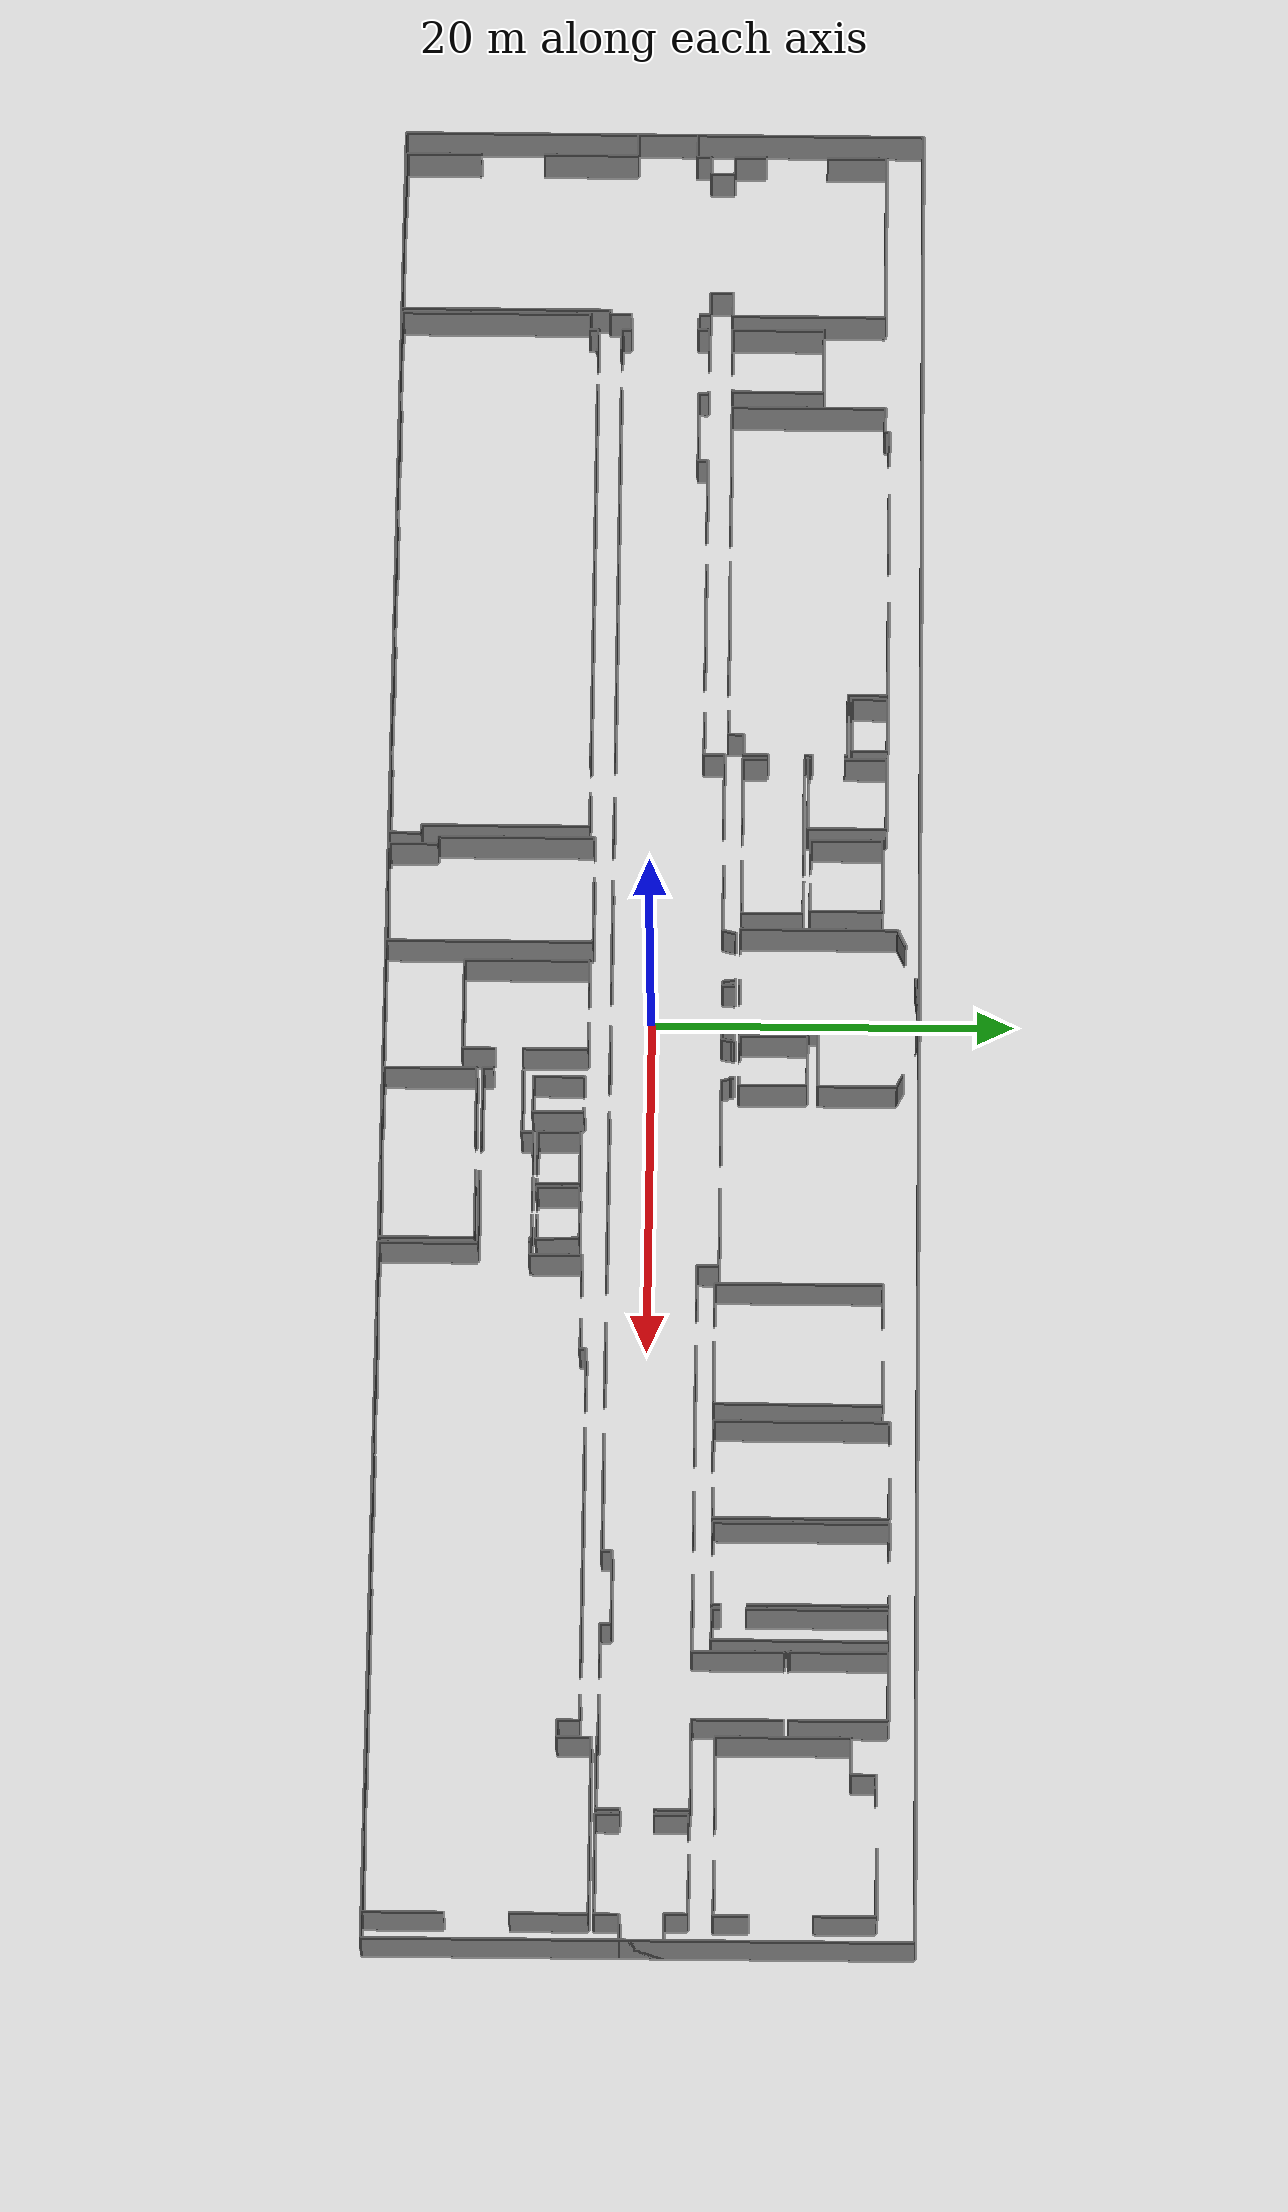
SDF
<sdf version="1.6">
  <world name="default">
    <light name="sun" type="directional">
      <cast_shadows>1</cast_shadows>
      <pose frame="">0 0 10 0 -0 0</pose>
      <diffuse>0.8 0.8 0.8 1</diffuse>
      <specular>0.1 0.1 0.1 1</specular>
      <attenuation>
        <range>1000</range>
        <constant>0.9</constant>
        <linear>0.01</linear>
        <quadratic>0.001</quadratic>
      </attenuation>
      <direction>-0.5 0.5 -1</direction>
    </light>
    <model name="ground_plane">
      <static>1</static>
      <link name="link">
        <collision name="collision">
          <geometry>
            <plane>
              <normal>0 0 1</normal>
              <size>100 100</size>
            </plane>
          </geometry>
          <surface>
            <friction>
              <ode>
                <mu>100</mu>
                <mu2>50</mu2>
              </ode>
              <torsional>
                <ode />
              </torsional>
            </friction>
            <contact>
              <ode />
            </contact>
            <bounce />
          </surface>
          <max_contacts>10</max_contacts>
        </collision>
        <visual name="visual">
          <cast_shadows>0</cast_shadows>
          <geometry>
            <plane>
              <normal>0 0 1</normal>
              <size>100 100</size>
            </plane>
          </geometry>
          <material>
            <script>
              <uri>file://media/materials/scripts/gazebo.material</uri>
              <name>Gazebo/Grey</name>
            </script>
          </material>
        </visual>
        <self_collide>0</self_collide>
        <kinematic>0</kinematic>
        <gravity>1</gravity>
      </link>
    </model>
    <gravity>0 0 -9.8</gravity>
    <magnetic_field>6e-06 2.3e-05 -4.2e-05</magnetic_field>
    <atmosphere type="adiabatic" />
    <physics default="0" name="default_physics" type="ode">
      <max_step_size>0.001</max_step_size>
      <real_time_factor>1</real_time_factor>
      <real_time_update_rate>1000</real_time_update_rate>
    </physics>
    <scene>
      <ambient>0.4 0.4 0.4 1</ambient>
      <background>0.7 0.7 0.7 1</background>
      <shadows>1</shadows>
    </scene>
    <spherical_coordinates>
      <surface_model>EARTH_WGS84</surface_model>
      <latitude_deg>0</latitude_deg>
      <longitude_deg>0</longitude_deg>
      <elevation>0</elevation>
      <heading_deg>0</heading_deg>
    </spherical_coordinates>
  <model name="50056456">
		<static>1</static>
		<link name="Wall_0">
			<collision name="Wall_0_Collision">
				<geometry>
					<box>
						<size>2.08262390621 0.1 2.5</size>
					</box>
				</geometry>
				<pose frame="">1.04131195311 0 1.25 0 0 0</pose>
			</collision>
			<visual name="Wall_0_Visual">
				<pose frame="">1.04131195311 0 1.25 0 0 0</pose>
				<geometry>
					<box>
						<size>2.08262390621 0.1 2.5</size>
					</box>
				</geometry>
				<material>
					<script>
						<uri>file://media/materials/scripts/gazebo.material</uri>
						<name>Gazebo/Grey</name>
					</script>
					<ambient>1 1 1 1</ambient>
				</material>
			</visual>
			<pose frame="">11.503392544 -29.4986150288 0 0 0 3.14159265359</pose>
		</link>
		<link name="Wall_1">
			<collision name="Wall_1_Collision">
				<geometry>
					<box>
						<size>4.572843457 0.1 2.5</size>
					</box>
				</geometry>
				<pose frame="">2.2864217285 0 1.25 0 0 0</pose>
			</collision>
			<visual name="Wall_1_Visual">
				<pose frame="">2.2864217285 0 1.25 0 0 0</pose>
				<geometry>
					<box>
						<size>4.572843457 0.1 2.5</size>
					</box>
				</geometry>
				<material>
					<script>
						<uri>file://media/materials/scripts/gazebo.material</uri>
						<name>Gazebo/Grey</name>
					</script>
					<ambient>1 1 1 1</ambient>
				</material>
			</visual>
			<pose frame="">5.95317357458 -29.4986150288 0 0 0 3.12254874871</pose>
		</link>
		<link name="Wall_2">
			<collision name="Wall_2_Collision">
				<geometry>
					<box>
						<size>4.24775312783 0.1 2.5</size>
					</box>
				</geometry>
				<pose frame="">2.12387656392 0 1.25 0 0 0</pose>
			</collision>
			<visual name="Wall_2_Visual">
				<pose frame="">2.12387656392 0 1.25 0 0 0</pose>
				<geometry>
					<box>
						<size>4.24775312783 0.1 2.5</size>
					</box>
				</geometry>
				<material>
					<script>
						<uri>file://media/materials/scripts/gazebo.material</uri>
						<name>Gazebo/Grey</name>
					</script>
					<ambient>1 1 1 1</ambient>
				</material>
			</visual>
			<pose frame="">1.3811593098 -29.4115354968 0 0 0 1.57079632679</pose>
		</link>
		<link name="Wall_3">
			<collision name="Wall_3_Collision">
				<geometry>
					<box>
						<size>5.36301491703 0.1 2.5</size>
					</box>
				</geometry>
				<pose frame="">2.68150745851 0 1.25 0 0 0</pose>
			</collision>
			<visual name="Wall_3_Visual">
				<pose frame="">2.68150745851 0 1.25 0 0 0</pose>
				<geometry>
					<box>
						<size>5.36301491703 0.1 2.5</size>
					</box>
				</geometry>
				<material>
					<script>
						<uri>file://media/materials/scripts/gazebo.material</uri>
						<name>Gazebo/Grey</name>
					</script>
					<ambient>1 1 1 1</ambient>
				</material>
			</visual>
			<pose frame="">1.3811593098 -21.6009758329 0 0 0 1.57079632679</pose>
		</link>
		<link name="Wall_4">
			<collision name="Wall_4_Collision">
				<geometry>
					<box>
						<size>1.3811593098 0.1 2.5</size>
					</box>
				</geometry>
				<pose frame="">0.690579654901 0 1.25 0 0 0</pose>
			</collision>
			<visual name="Wall_4_Visual">
				<pose frame="">0.690579654901 0 1.25 0 0 0</pose>
				<geometry>
					<box>
						<size>1.3811593098 0.1 2.5</size>
					</box>
				</geometry>
				<material>
					<script>
						<uri>file://media/materials/scripts/gazebo.material</uri>
						<name>Gazebo/Grey</name>
					</script>
					<ambient>1 1 1 1</ambient>
				</material>
			</visual>
			<pose frame="">1.3811593098 -16.2379609159 0 0 0 3.14159265359</pose>
		</link>
		<link name="Wall_5">
			<collision name="Wall_5_Collision">
				<geometry>
					<box>
						<size>1.43469458633 0.1 2.5</size>
					</box>
				</geometry>
				<pose frame="">0.717347293165 0 1.25 0 0 0</pose>
			</collision>
			<visual name="Wall_5_Visual">
				<pose frame="">0.717347293165 0 1.25 0 0 0</pose>
				<geometry>
					<box>
						<size>1.43469458633 0.1 2.5</size>
					</box>
				</geometry>
				<material>
					<script>
						<uri>file://media/materials/scripts/gazebo.material</uri>
						<name>Gazebo/Grey</name>
					</script>
					<ambient>1 1 1 1</ambient>
				</material>
			</visual>
			<pose frame="">0.0 -12.8572759693 0 0 0 0.0</pose>
		</link>
		<link name="Wall_6">
			<collision name="Wall_6_Collision">
				<geometry>
					<box>
						<size>0.782699296079 0.1 2.5</size>
					</box>
				</geometry>
				<pose frame="">0.391349648039 0 1.25 0 0 0</pose>
			</collision>
			<visual name="Wall_6_Visual">
				<pose frame="">0.391349648039 0 1.25 0 0 0</pose>
				<geometry>
					<box>
						<size>0.782699296079 0.1 2.5</size>
					</box>
				</geometry>
				<material>
					<script>
						<uri>file://media/materials/scripts/gazebo.material</uri>
						<name>Gazebo/Grey</name>
					</script>
					<ambient>1 1 1 1</ambient>
				</material>
			</visual>
			<pose frame="">1.43469458633 -12.8572759693 0 0 0 1.57079632679</pose>
		</link>
		<link name="Wall_7">
			<collision name="Wall_7_Collision">
				<geometry>
					<box>
						<size>1.1062827713 0.1 2.5</size>
					</box>
				</geometry>
				<pose frame="">0.553141385649 0 1.25 0 0 0</pose>
			</collision>
			<visual name="Wall_7_Visual">
				<pose frame="">0.553141385649 0 1.25 0 0 0</pose>
				<geometry>
					<box>
						<size>1.1062827713 0.1 2.5</size>
					</box>
				</geometry>
				<material>
					<script>
						<uri>file://media/materials/scripts/gazebo.material</uri>
						<name>Gazebo/Grey</name>
					</script>
					<ambient>1 1 1 1</ambient>
				</material>
			</visual>
			<pose frame="">1.43469458633 -12.0745766732 0 0 0 0.0</pose>
		</link>
		<link name="Wall_8">
			<collision name="Wall_8_Collision">
				<geometry>
					<box>
						<size>1.34769976197 0.1 2.5</size>
					</box>
				</geometry>
				<pose frame="">0.673849880986 0 1.25 0 0 0</pose>
			</collision>
			<visual name="Wall_8_Visual">
				<pose frame="">0.673849880986 0 1.25 0 0 0</pose>
				<geometry>
					<box>
						<size>1.34769976197 0.1 2.5</size>
					</box>
				</geometry>
				<material>
					<script>
						<uri>file://media/materials/scripts/gazebo.material</uri>
						<name>Gazebo/Grey</name>
					</script>
					<ambient>1 1 1 1</ambient>
				</material>
			</visual>
			<pose frame="">2.54097735763 -12.0745766732 0 0 0 1.57079632679</pose>
		</link>
		<link name="Wall_9">
			<collision name="Wall_9_Collision">
				<geometry>
					<box>
						<size>1.09493193735 0.1 2.5</size>
					</box>
				</geometry>
				<pose frame="">0.547465968675 0 1.25 0 0 0</pose>
			</collision>
			<visual name="Wall_9_Visual">
				<pose frame="">0.547465968675 0 1.25 0 0 0</pose>
				<geometry>
					<box>
						<size>1.09493193735 0.1 2.5</size>
					</box>
				</geometry>
				<material>
					<script>
						<uri>file://media/materials/scripts/gazebo.material</uri>
						<name>Gazebo/Grey</name>
					</script>
					<ambient>1 1 1 1</ambient>
				</material>
			</visual>
			<pose frame="">2.54097735763 -10.7268769112 0 0 0 3.14159265359</pose>
		</link>
		<link name="Wall_10">
			<collision name="Wall_10_Collision">
				<geometry>
					<box>
						<size>1.77716788222 0.1 2.5</size>
					</box>
				</geometry>
				<pose frame="">0.888583941111 0 1.25 0 0 0</pose>
			</collision>
			<visual name="Wall_10_Visual">
				<pose frame="">0.888583941111 0 1.25 0 0 0</pose>
				<geometry>
					<box>
						<size>1.77716788222 0.1 2.5</size>
					</box>
				</geometry>
				<material>
					<script>
						<uri>file://media/materials/scripts/gazebo.material</uri>
						<name>Gazebo/Grey</name>
					</script>
					<ambient>1 1 1 1</ambient>
				</material>
			</visual>
			<pose frame="">1.44604542028 -10.7268769112 0 0 0 1.57079632679</pose>
		</link>
		<link name="Wall_11">
			<collision name="Wall_11_Collision">
				<geometry>
					<box>
						<size>3.38068494659 0.1 2.5</size>
					</box>
				</geometry>
				<pose frame="">1.6903424733 0 1.25 0 0 0</pose>
			</collision>
			<visual name="Wall_11_Visual">
				<pose frame="">1.6903424733 0 1.25 0 0 0</pose>
				<geometry>
					<box>
						<size>3.38068494659 0.1 2.5</size>
					</box>
				</geometry>
				<material>
					<script>
						<uri>file://media/materials/scripts/gazebo.material</uri>
						<name>Gazebo/Grey</name>
					</script>
					<ambient>1 1 1 1</ambient>
				</material>
			</visual>
			<pose frame="">1.44604542028 -5.4765232565 0 0 0 1.57079632679</pose>
		</link>
		<link name="Wall_12">
			<collision name="Wall_12_Collision">
				<geometry>
					<box>
						<size>10.3866907237 0.1 2.5</size>
					</box>
				</geometry>
				<pose frame="">5.19334536183 0 1.25 0 0 0</pose>
			</collision>
			<visual name="Wall_12_Visual">
				<pose frame="">5.19334536183 0 1.25 0 0 0</pose>
				<geometry>
					<box>
						<size>10.3866907237 0.1 2.5</size>
					</box>
				</geometry>
				<material>
					<script>
						<uri>file://media/materials/scripts/gazebo.material</uri>
						<name>Gazebo/Grey</name>
					</script>
					<ambient>1 1 1 1</ambient>
				</material>
			</visual>
			<pose frame="">1.44604542028 -2.09583830991 0 0 0 0.0</pose>
		</link>
		<link name="Wall_13">
			<collision name="Wall_13_Collision">
				<geometry>
					<box>
						<size>8.64967429883 0.1 2.5</size>
					</box>
				</geometry>
				<pose frame="">4.32483714942 0 1.25 0 0 0</pose>
			</collision>
			<visual name="Wall_13_Visual">
				<pose frame="">4.32483714942 0 1.25 0 0 0</pose>
				<geometry>
					<box>
						<size>8.64967429883 0.1 2.5</size>
					</box>
				</geometry>
				<material>
					<script>
						<uri>file://media/materials/scripts/gazebo.material</uri>
						<name>Gazebo/Grey</name>
					</script>
					<ambient>1 1 1 1</ambient>
				</material>
			</visual>
			<pose frame="">11.8327361439 -2.09583830991 0 0 0 -1.57079632679</pose>
		</link>
		<link name="Wall_14">
			<collision name="Wall_14_Collision">
				<geometry>
					<box>
						<size>1.48204619959 0.1 2.5</size>
					</box>
				</geometry>
				<pose frame="">0.741023099794 0 1.25 0 0 0</pose>
			</collision>
			<visual name="Wall_14_Visual">
				<pose frame="">0.741023099794 0 1.25 0 0 0</pose>
				<geometry>
					<box>
						<size>1.48204619959 0.1 2.5</size>
					</box>
				</geometry>
				<material>
					<script>
						<uri>file://media/materials/scripts/gazebo.material</uri>
						<name>Gazebo/Grey</name>
					</script>
					<ambient>1 1 1 1</ambient>
				</material>
			</visual>
			<pose frame="">11.8327361439 -10.7455126087 0 0 0 3.14159265359</pose>
		</link>
		<link name="Wall_15">
			<collision name="Wall_15_Collision">
				<geometry>
					<box>
						<size>1.28162774347 0.1 2.5</size>
					</box>
				</geometry>
				<pose frame="">0.640813871736 0 1.25 0 0 0</pose>
			</collision>
			<visual name="Wall_15_Visual">
				<pose frame="">0.640813871736 0 1.25 0 0 0</pose>
				<geometry>
					<box>
						<size>1.28162774347 0.1 2.5</size>
					</box>
				</geometry>
				<material>
					<script>
						<uri>file://media/materials/scripts/gazebo.material</uri>
						<name>Gazebo/Grey</name>
					</script>
					<ambient>1 1 1 1</ambient>
				</material>
			</visual>
			<pose frame="">10.3506899443 -10.7455126087 0 0 0 -1.57079632679</pose>
		</link>
		<link name="Wall_16">
			<collision name="Wall_16_Collision">
				<geometry>
					<box>
						<size>1.41428002677 0.1 2.5</size>
					</box>
				</geometry>
				<pose frame="">0.707140013384 0 1.25 0 0 0</pose>
			</collision>
			<visual name="Wall_16_Visual">
				<pose frame="">0.707140013384 0 1.25 0 0 0</pose>
				<geometry>
					<box>
						<size>1.41428002677 0.1 2.5</size>
					</box>
				</geometry>
				<material>
					<script>
						<uri>file://media/materials/scripts/gazebo.material</uri>
						<name>Gazebo/Grey</name>
					</script>
					<ambient>1 1 1 1</ambient>
				</material>
			</visual>
			<pose frame="">10.3506899443 -12.0271403522 0 0 0 0.0</pose>
		</link>
		<link name="Wall_17">
			<collision name="Wall_17_Collision">
				<geometry>
					<box>
						<size>0.611759125139 0.1 2.5</size>
					</box>
				</geometry>
				<pose frame="">0.305879562569 0 1.25 0 0 0</pose>
			</collision>
			<visual name="Wall_17_Visual">
				<pose frame="">0.305879562569 0 1.25 0 0 0</pose>
				<geometry>
					<box>
						<size>0.611759125139 0.1 2.5</size>
					</box>
				</geometry>
				<material>
					<script>
						<uri>file://media/materials/scripts/gazebo.material</uri>
						<name>Gazebo/Grey</name>
					</script>
					<ambient>1 1 1 1</ambient>
				</material>
			</visual>
			<pose frame="">11.7649699711 -12.0271403522 0 0 0 -1.57079632679</pose>
		</link>
		<link name="Wall_18">
			<collision name="Wall_18_Collision">
				<geometry>
					<box>
						<size>1.22978662126 0.1 2.5</size>
					</box>
				</geometry>
				<pose frame="">0.614893310632 0 1.25 0 0 0</pose>
			</collision>
			<visual name="Wall_18_Visual">
				<pose frame="">0.614893310632 0 1.25 0 0 0</pose>
				<geometry>
					<box>
						<size>1.22978662126 0.1 2.5</size>
					</box>
				</geometry>
				<material>
					<script>
						<uri>file://media/materials/scripts/gazebo.material</uri>
						<name>Gazebo/Grey</name>
					</script>
					<ambient>1 1 1 1</ambient>
				</material>
			</visual>
			<pose frame="">11.7649699711 -16.4629446096 0 0 0 -1.57079632679</pose>
		</link>
		<link name="Wall_19">
			<collision name="Wall_19_Collision">
				<geometry>
					<box>
						<size>0.253614901781 0.1 2.5</size>
					</box>
				</geometry>
				<pose frame="">0.126807450891 0 1.25 0 0 0</pose>
			</collision>
			<visual name="Wall_19_Visual">
				<pose frame="">0.126807450891 0 1.25 0 0 0</pose>
				<geometry>
					<box>
						<size>0.253614901781 0.1 2.5</size>
					</box>
				</geometry>
				<material>
					<script>
						<uri>file://media/materials/scripts/gazebo.material</uri>
						<name>Gazebo/Grey</name>
					</script>
					<ambient>1 1 1 1</ambient>
				</material>
			</visual>
			<pose frame="">11.7649699711 -17.6927312309 0 0 0 3.14159265359</pose>
		</link>
		<link name="Wall_20">
			<collision name="Wall_20_Collision">
				<geometry>
					<box>
						<size>11.8058864831 0.1 2.5</size>
					</box>
				</geometry>
				<pose frame="">5.90294324157 0 1.25 0 0 0</pose>
			</collision>
			<visual name="Wall_20_Visual">
				<pose frame="">5.90294324157 0 1.25 0 0 0</pose>
				<geometry>
					<box>
						<size>11.8058864831 0.1 2.5</size>
					</box>
				</geometry>
				<material>
					<script>
						<uri>file://media/materials/scripts/gazebo.material</uri>
						<name>Gazebo/Grey</name>
					</script>
					<ambient>1 1 1 1</ambient>
				</material>
			</visual>
			<pose frame="">11.5113550693 -17.6927312309 0 0 0 -1.57147078067</pose>
		</link>
		<link name="Wall_21">
			<collision name="Wall_21_Collision">
				<geometry>
					<box>
						<size>4.18794948032 0.1 2.5</size>
					</box>
				</geometry>
				<pose frame="">2.09397474016 0 1.25 0 0 0</pose>
			</collision>
			<visual name="Wall_21_Visual">
				<pose frame="">2.09397474016 0 1.25 0 0 0</pose>
				<geometry>
					<box>
						<size>4.18794948032 0.1 2.5</size>
					</box>
				</geometry>
				<material>
					<script>
						<uri>file://media/materials/scripts/gazebo.material</uri>
						<name>Gazebo/Grey</name>
					</script>
					<ambient>1 1 1 1</ambient>
				</material>
			</visual>
			<pose frame="">103.634892802 -17.1229871329 0 0 0 3.14159265359</pose>
		</link>
		<link name="Wall_22">
			<collision name="Wall_22_Collision">
				<geometry>
					<box>
						<size>0.0789475913361 0.1 2.5</size>
					</box>
				</geometry>
				<pose frame="">0.0394737956681 0 1.25 0 0 0</pose>
			</collision>
			<visual name="Wall_22_Visual">
				<pose frame="">0.0394737956681 0 1.25 0 0 0</pose>
				<geometry>
					<box>
						<size>0.0789475913361 0.1 2.5</size>
					</box>
				</geometry>
				<material>
					<script>
						<uri>file://media/materials/scripts/gazebo.material</uri>
						<name>Gazebo/Grey</name>
					</script>
					<ambient>1 1 1 1</ambient>
				</material>
			</visual>
			<pose frame="">99.4469433221 -17.1229871329 0 0 0 1.57079632679</pose>
		</link>
		<link name="Wall_23">
			<collision name="Wall_23_Collision">
				<geometry>
					<box>
						<size>2.44263169932 0.1 2.5</size>
					</box>
				</geometry>
				<pose frame="">1.22131584966 0 1.25 0 0 0</pose>
			</collision>
			<visual name="Wall_23_Visual">
				<pose frame="">1.22131584966 0 1.25 0 0 0</pose>
				<geometry>
					<box>
						<size>2.44263169932 0.1 2.5</size>
					</box>
				</geometry>
				<material>
					<script>
						<uri>file://media/materials/scripts/gazebo.material</uri>
						<name>Gazebo/Grey</name>
					</script>
					<ambient>1 1 1 1</ambient>
				</material>
			</visual>
			<pose frame="">99.4469433221 -17.0440395416 0 0 0 3.14159265359</pose>
		</link>
		<link name="Wall_24">
			<collision name="Wall_24_Collision">
				<geometry>
					<box>
						<size>2.13090730435 0.1 2.5</size>
					</box>
				</geometry>
				<pose frame="">1.06545365217 0 1.25 0 0 0</pose>
			</collision>
			<visual name="Wall_24_Visual">
				<pose frame="">1.06545365217 0 1.25 0 0 0</pose>
				<geometry>
					<box>
						<size>2.13090730435 0.1 2.5</size>
					</box>
				</geometry>
				<material>
					<script>
						<uri>file://media/materials/scripts/gazebo.material</uri>
						<name>Gazebo/Grey</name>
					</script>
					<ambient>1 1 1 1</ambient>
				</material>
			</visual>
			<pose frame="">94.9321914733 -17.0440395416 0 0 0 3.14159265359</pose>
		</link>
		<link name="Wall_25">
			<collision name="Wall_25_Collision">
				<geometry>
					<box>
						<size>0.598036475143 0.1 2.5</size>
					</box>
				</geometry>
				<pose frame="">0.299018237571 0 1.25 0 0 0</pose>
			</collision>
			<visual name="Wall_25_Visual">
				<pose frame="">0.299018237571 0 1.25 0 0 0</pose>
				<geometry>
					<box>
						<size>0.598036475143 0.1 2.5</size>
					</box>
				</geometry>
				<material>
					<script>
						<uri>file://media/materials/scripts/gazebo.material</uri>
						<name>Gazebo/Grey</name>
					</script>
					<ambient>1 1 1 1</ambient>
				</material>
			</visual>
			<pose frame="">92.801284169 -17.0440395416 0 0 0 1.57079632679</pose>
		</link>
		<link name="Wall_26">
			<collision name="Wall_26_Collision">
				<geometry>
					<box>
						<size>4.31263923831 0.1 2.5</size>
					</box>
				</geometry>
				<pose frame="">2.15631961915 0 1.25 0 0 0</pose>
			</collision>
			<visual name="Wall_26_Visual">
				<pose frame="">2.15631961915 0 1.25 0 0 0</pose>
				<geometry>
					<box>
						<size>4.31263923831 0.1 2.5</size>
					</box>
				</geometry>
				<material>
					<script>
						<uri>file://media/materials/scripts/gazebo.material</uri>
						<name>Gazebo/Grey</name>
					</script>
					<ambient>1 1 1 1</ambient>
				</material>
			</visual>
			<pose frame="">92.801284169 -16.4460030664 0 0 0 3.14159265359</pose>
		</link>
		<link name="Wall_27">
			<collision name="Wall_27_Collision">
				<geometry>
					<box>
						<size>0.556021447994 0.1 2.5</size>
					</box>
				</geometry>
				<pose frame="">0.278010723997 0 1.25 0 0 0</pose>
			</collision>
			<visual name="Wall_27_Visual">
				<pose frame="">0.278010723997 0 1.25 0 0 0</pose>
				<geometry>
					<box>
						<size>0.556021447994 0.1 2.5</size>
					</box>
				</geometry>
				<material>
					<script>
						<uri>file://media/materials/scripts/gazebo.material</uri>
						<name>Gazebo/Grey</name>
					</script>
					<ambient>1 1 1 1</ambient>
				</material>
			</visual>
			<pose frame="">88.4886449307 -16.4460030664 0 0 0 -1.57079632679</pose>
		</link>
		<link name="Wall_28">
			<collision name="Wall_28_Collision">
				<geometry>
					<box>
						<size>6.95738354807 0.1 2.5</size>
					</box>
				</geometry>
				<pose frame="">3.47869177403 0 1.25 0 0 0</pose>
			</collision>
			<visual name="Wall_28_Visual">
				<pose frame="">3.47869177403 0 1.25 0 0 0</pose>
				<geometry>
					<box>
						<size>6.95738354807 0.1 2.5</size>
					</box>
				</geometry>
				<material>
					<script>
						<uri>file://media/materials/scripts/gazebo.material</uri>
						<name>Gazebo/Grey</name>
					</script>
					<ambient>1 1 1 1</ambient>
				</material>
			</visual>
			<pose frame="">88.4886449307 -17.0020245144 0 0 0 3.14159265359</pose>
		</link>
		<link name="Wall_29">
			<collision name="Wall_29_Collision">
				<geometry>
					<box>
						<size>4.00091484333 0.1 2.5</size>
					</box>
				</geometry>
				<pose frame="">2.00045742167 0 1.25 0 0 0</pose>
			</collision>
			<visual name="Wall_29_Visual">
				<pose frame="">2.00045742167 0 1.25 0 0 0</pose>
				<geometry>
					<box>
						<size>4.00091484333 0.1 2.5</size>
					</box>
				</geometry>
				<material>
					<script>
						<uri>file://media/materials/scripts/gazebo.material</uri>
						<name>Gazebo/Grey</name>
					</script>
					<ambient>1 1 1 1</ambient>
				</material>
			</visual>
			<pose frame="">78.9202307438 -17.0020245144 0 0 0 3.14159265359</pose>
		</link>
		<link name="Wall_30">
			<collision name="Wall_30_Collision">
				<geometry>
					<box>
						<size>9.94739650835 0.1 2.5</size>
					</box>
				</geometry>
				<pose frame="">4.97369825417 0 1.25 0 0 0</pose>
			</collision>
			<visual name="Wall_30_Visual">
				<pose frame="">4.97369825417 0 1.25 0 0 0</pose>
				<geometry>
					<box>
						<size>9.94739650835 0.1 2.5</size>
					</box>
				</geometry>
				<material>
					<script>
						<uri>file://media/materials/scripts/gazebo.material</uri>
						<name>Gazebo/Grey</name>
					</script>
					<ambient>1 1 1 1</ambient>
				</material>
			</visual>
			<pose frame="">72.0470466655 -17.0020245144 0 0 0 3.14159265359</pose>
		</link>
		<link name="Wall_31">
			<collision name="Wall_31_Collision">
				<geometry>
					<box>
						<size>3.02372663126 0.1 2.5</size>
					</box>
				</geometry>
				<pose frame="">1.51186331563 0 1.25 0 0 0</pose>
			</collision>
			<visual name="Wall_31_Visual">
				<pose frame="">1.51186331563 0 1.25 0 0 0</pose>
				<geometry>
					<box>
						<size>3.02372663126 0.1 2.5</size>
					</box>
				</geometry>
				<material>
					<script>
						<uri>file://media/materials/scripts/gazebo.material</uri>
						<name>Gazebo/Grey</name>
					</script>
					<ambient>1 1 1 1</ambient>
				</material>
			</visual>
			<pose frame="">59.875903196 -17.0020245144 0 0 0 3.14159265359</pose>
		</link>
		<link name="Wall_32">
			<collision name="Wall_32_Collision">
				<geometry>
					<box>
						<size>6.50250311301 0.1 2.5</size>
					</box>
				</geometry>
				<pose frame="">3.2512515565 0 1.25 0 0 0</pose>
			</collision>
			<visual name="Wall_32_Visual">
				<pose frame="">3.2512515565 0 1.25 0 0 0</pose>
				<geometry>
					<box>
						<size>6.50250311301 0.1 2.5</size>
					</box>
				</geometry>
				<material>
					<script>
						<uri>file://media/materials/scripts/gazebo.material</uri>
						<name>Gazebo/Grey</name>
					</script>
					<ambient>1 1 1 1</ambient>
				</material>
			</visual>
			<pose frame="">54.3168746241 -17.0020245144 0 0 0 3.14159265359</pose>
		</link>
		<link name="Wall_33">
			<collision name="Wall_33_Collision">
				<geometry>
					<box>
						<size>2.58443241595 0.1 2.5</size>
					</box>
				</geometry>
				<pose frame="">1.29221620797 0 1.25 0 0 0</pose>
			</collision>
			<visual name="Wall_33_Visual">
				<pose frame="">1.29221620797 0 1.25 0 0 0</pose>
				<geometry>
					<box>
						<size>2.58443241595 0.1 2.5</size>
					</box>
				</geometry>
				<material>
					<script>
						<uri>file://media/materials/scripts/gazebo.material</uri>
						<name>Gazebo/Grey</name>
					</script>
					<ambient>1 1 1 1</ambient>
				</material>
			</visual>
			<pose frame="">45.2619586118 -17.0020245144 0 0 0 3.14159265359</pose>
		</link>
		<link name="Wall_34">
			<collision name="Wall_34_Collision">
				<geometry>
					<box>
						<size>23.3545949701 0.1 2.5</size>
					</box>
				</geometry>
				<pose frame="">11.677297485 0 1.25 0 0 0</pose>
			</collision>
			<visual name="Wall_34_Visual">
				<pose frame="">11.677297485 0 1.25 0 0 0</pose>
				<geometry>
					<box>
						<size>23.3545949701 0.1 2.5</size>
					</box>
				</geometry>
				<material>
					<script>
						<uri>file://media/materials/scripts/gazebo.material</uri>
						<name>Gazebo/Grey</name>
					</script>
					<ambient>1 1 1 1</ambient>
				</material>
			</visual>
			<pose frame="">39.8926753238 -17.0020245144 0 0 0 3.14159265359</pose>
		</link>
		<link name="Wall_35">
			<collision name="Wall_35_Collision">
				<geometry>
					<box>
						<size>1.32584517124 0.1 2.5</size>
					</box>
				</geometry>
				<pose frame="">0.662922585618 0 1.25 0 0 0</pose>
			</collision>
			<visual name="Wall_35_Visual">
				<pose frame="">0.662922585618 0 1.25 0 0 0</pose>
				<geometry>
					<box>
						<size>1.32584517124 0.1 2.5</size>
					</box>
				</geometry>
				<material>
					<script>
						<uri>file://media/materials/scripts/gazebo.material</uri>
						<name>Gazebo/Grey</name>
					</script>
					<ambient>1 1 1 1</ambient>
				</material>
			</visual>
			<pose frame="">14.1073077347 -17.0020245144 0 0 0 3.14159265359</pose>
		</link>
		<link name="Wall_36">
			<collision name="Wall_36_Collision">
				<geometry>
					<box>
						<size>0.525865501089 0.1 2.5</size>
					</box>
				</geometry>
				<pose frame="">0.262932750544 0 1.25 0 0 0</pose>
			</collision>
			<visual name="Wall_36_Visual">
				<pose frame="">0.262932750544 0 1.25 0 0 0</pose>
				<geometry>
					<box>
						<size>0.525865501089 0.1 2.5</size>
					</box>
				</geometry>
				<material>
					<script>
						<uri>file://media/materials/scripts/gazebo.material</uri>
						<name>Gazebo/Grey</name>
					</script>
					<ambient>1 1 1 1</ambient>
				</material>
			</visual>
			<pose frame="">12.7814625634 -17.0020245144 0 0 0 1.57079632679</pose>
		</link>
		<link name="Wall_37">
			<collision name="Wall_37_Collision">
				<geometry>
					<box>
						<size>0.736618298561 0.1 2.5</size>
					</box>
				</geometry>
				<pose frame="">0.36830914928 0 1.25 0 0 0</pose>
			</collision>
			<visual name="Wall_37_Visual">
				<pose frame="">0.36830914928 0 1.25 0 0 0</pose>
				<geometry>
					<box>
						<size>0.736618298561 0.1 2.5</size>
					</box>
				</geometry>
				<material>
					<script>
						<uri>file://media/materials/scripts/gazebo.material</uri>
						<name>Gazebo/Grey</name>
					</script>
					<ambient>1 1 1 1</ambient>
				</material>
			</visual>
			<pose frame="">12.7814625634 -16.4761590133 0 0 0 3.14159265359</pose>
		</link>
		<link name="Wall_38">
			<collision name="Wall_38_Collision">
				<geometry>
					<box>
						<size>0.701379888694 0.1 2.5</size>
					</box>
				</geometry>
				<pose frame="">0.350689944347 0 1.25 0 0 0</pose>
			</collision>
			<visual name="Wall_38_Visual">
				<pose frame="">0.350689944347 0 1.25 0 0 0</pose>
				<geometry>
					<box>
						<size>0.701379888694 0.1 2.5</size>
					</box>
				</geometry>
				<material>
					<script>
						<uri>file://media/materials/scripts/gazebo.material</uri>
						<name>Gazebo/Grey</name>
					</script>
					<ambient>1 1 1 1</ambient>
				</material>
			</visual>
			<pose frame="">12.0448442649 -12.684641644 0 0 0 0.0</pose>
		</link>
		<link name="Wall_39">
			<collision name="Wall_39_Collision">
				<geometry>
					<box>
						<size>0.63496903933 0.1 2.5</size>
					</box>
				</geometry>
				<pose frame="">0.317484519665 0 1.25 0 0 0</pose>
			</collision>
			<visual name="Wall_39_Visual">
				<pose frame="">0.317484519665 0 1.25 0 0 0</pose>
				<geometry>
					<box>
						<size>0.63496903933 0.1 2.5</size>
					</box>
				</geometry>
				<material>
					<script>
						<uri>file://media/materials/scripts/gazebo.material</uri>
						<name>Gazebo/Grey</name>
					</script>
					<ambient>1 1 1 1</ambient>
				</material>
			</visual>
			<pose frame="">12.7462241536 -12.684641644 0 0 0 1.57079632679</pose>
		</link>
		<link name="Wall_40">
			<collision name="Wall_40_Collision">
				<geometry>
					<box>
						<size>1.38226051011 0.1 2.5</size>
					</box>
				</geometry>
				<pose frame="">0.691130255055 0 1.25 0 0 0</pose>
			</collision>
			<visual name="Wall_40_Visual">
				<pose frame="">0.691130255055 0 1.25 0 0 0</pose>
				<geometry>
					<box>
						<size>1.38226051011 0.1 2.5</size>
					</box>
				</geometry>
				<material>
					<script>
						<uri>file://media/materials/scripts/gazebo.material</uri>
						<name>Gazebo/Grey</name>
					</script>
					<ambient>1 1 1 1</ambient>
				</material>
			</visual>
			<pose frame="">12.7462241536 -12.0496726047 0 0 0 0.0</pose>
		</link>
		<link name="Wall_41">
			<collision name="Wall_41_Collision">
				<geometry>
					<box>
						<size>0.166535369707 0.1 2.5</size>
					</box>
				</geometry>
				<pose frame="">0.0832676848534 0 1.25 0 0 0</pose>
			</collision>
			<visual name="Wall_41_Visual">
				<pose frame="">0.0832676848534 0 1.25 0 0 0</pose>
				<geometry>
					<box>
						<size>0.166535369707 0.1 2.5</size>
					</box>
				</geometry>
				<material>
					<script>
						<uri>file://media/materials/scripts/gazebo.material</uri>
						<name>Gazebo/Grey</name>
					</script>
					<ambient>1 1 1 1</ambient>
				</material>
			</visual>
			<pose frame="">16.7173218809 -12.0496726047 0 0 0 0.0</pose>
		</link>
		<link name="Wall_42">
			<collision name="Wall_42_Collision">
				<geometry>
					<box>
						<size>0.564153388732 0.1 2.5</size>
					</box>
				</geometry>
				<pose frame="">0.282076694366 0 1.25 0 0 0</pose>
			</collision>
			<visual name="Wall_42_Visual">
				<pose frame="">0.282076694366 0 1.25 0 0 0</pose>
				<geometry>
					<box>
						<size>0.564153388732 0.1 2.5</size>
					</box>
				</geometry>
				<material>
					<script>
						<uri>file://media/materials/scripts/gazebo.material</uri>
						<name>Gazebo/Grey</name>
					</script>
					<ambient>1 1 1 1</ambient>
				</material>
			</visual>
			<pose frame="">16.8838572506 -12.0496726047 0 0 0 -1.57079632679</pose>
		</link>
		<link name="Wall_43">
			<collision name="Wall_43_Collision">
				<geometry>
					<box>
						<size>4.31704403954 0.1 2.5</size>
					</box>
				</geometry>
				<pose frame="">2.15852201977 0 1.25 0 0 0</pose>
			</collision>
			<visual name="Wall_43_Visual">
				<pose frame="">2.15852201977 0 1.25 0 0 0</pose>
				<geometry>
					<box>
						<size>4.31704403954 0.1 2.5</size>
					</box>
				</geometry>
				<material>
					<script>
						<uri>file://media/materials/scripts/gazebo.material</uri>
						<name>Gazebo/Grey</name>
					</script>
					<ambient>1 1 1 1</ambient>
				</material>
			</visual>
			<pose frame="">16.8838572506 -12.6138259934 0 0 0 0.0</pose>
		</link>
		<link name="Wall_44">
			<collision name="Wall_44_Collision">
				<geometry>
					<box>
						<size>0.5507695696 0.1 2.5</size>
					</box>
				</geometry>
				<pose frame="">0.2753847848 0 1.25 0 0 0</pose>
			</collision>
			<visual name="Wall_44_Visual">
				<pose frame="">0.2753847848 0 1.25 0 0 0</pose>
				<geometry>
					<box>
						<size>0.5507695696 0.1 2.5</size>
					</box>
				</geometry>
				<material>
					<script>
						<uri>file://media/materials/scripts/gazebo.material</uri>
						<name>Gazebo/Grey</name>
					</script>
					<ambient>1 1 1 1</ambient>
				</material>
			</visual>
			<pose frame="">21.2009012901 -12.6138259934 0 0 0 1.57079632679</pose>
		</link>
		<link name="Wall_45">
			<collision name="Wall_45_Collision">
				<geometry>
					<box>
						<size>3.99684887296 0.1 2.5</size>
					</box>
				</geometry>
				<pose frame="">1.99842443648 0 1.25 0 0 0</pose>
			</collision>
			<visual name="Wall_45_Visual">
				<pose frame="">1.99842443648 0 1.25 0 0 0</pose>
				<geometry>
					<box>
						<size>3.99684887296 0.1 2.5</size>
					</box>
				</geometry>
				<material>
					<script>
						<uri>file://media/materials/scripts/gazebo.material</uri>
						<name>Gazebo/Grey</name>
					</script>
					<ambient>1 1 1 1</ambient>
				</material>
			</visual>
			<pose frame="">21.2009012901 -12.0630564238 0 0 0 0.0</pose>
		</link>
		<link name="Wall_46">
			<collision name="Wall_46_Collision">
				<geometry>
					<box>
						<size>6.78051383701 0.1 2.5</size>
					</box>
				</geometry>
				<pose frame="">3.3902569185 0 1.25 0 0 0</pose>
			</collision>
			<visual name="Wall_46_Visual">
				<pose frame="">3.3902569185 0 1.25 0 0 0</pose>
				<geometry>
					<box>
						<size>6.78051383701 0.1 2.5</size>
					</box>
				</geometry>
				<material>
					<script>
						<uri>file://media/materials/scripts/gazebo.material</uri>
						<name>Gazebo/Grey</name>
					</script>
					<ambient>1 1 1 1</ambient>
				</material>
			</visual>
			<pose frame="">27.8443580426 -12.0630564238 0 0 0 0.0</pose>
		</link>
		<link name="Wall_47">
			<collision name="Wall_47_Collision">
				<geometry>
					<box>
						<size>2.63457938384 0.1 2.5</size>
					</box>
				</geometry>
				<pose frame="">1.31728969192 0 1.25 0 0 0</pose>
			</collision>
			<visual name="Wall_47_Visual">
				<pose frame="">1.31728969192 0 1.25 0 0 0</pose>
				<geometry>
					<box>
						<size>2.63457938384 0.1 2.5</size>
					</box>
				</geometry>
				<material>
					<script>
						<uri>file://media/materials/scripts/gazebo.material</uri>
						<name>Gazebo/Grey</name>
					</script>
					<ambient>1 1 1 1</ambient>
				</material>
			</visual>
			<pose frame="">37.2692773585 -12.0630564238 0 0 0 0.0</pose>
		</link>
		<link name="Wall_48">
			<collision name="Wall_48_Collision">
				<geometry>
					<box>
						<size>1.14287650462 0.1 2.5</size>
					</box>
				</geometry>
				<pose frame="">0.57143825231 0 1.25 0 0 0</pose>
			</collision>
			<visual name="Wall_48_Visual">
				<pose frame="">0.57143825231 0 1.25 0 0 0</pose>
				<geometry>
					<box>
						<size>1.14287650462 0.1 2.5</size>
					</box>
				</geometry>
				<material>
					<script>
						<uri>file://media/materials/scripts/gazebo.material</uri>
						<name>Gazebo/Grey</name>
					</script>
					<ambient>1 1 1 1</ambient>
				</material>
			</visual>
			<pose frame="">39.9038567423 -12.0630564238 0 0 0 1.57079632679</pose>
		</link>
		<link name="Wall_49">
			<collision name="Wall_49_Collision">
				<geometry>
					<box>
						<size>4.05868550566 0.1 2.5</size>
					</box>
				</geometry>
				<pose frame="">2.02934275283 0 1.25 0 0 0</pose>
			</collision>
			<visual name="Wall_49_Visual">
				<pose frame="">2.02934275283 0 1.25 0 0 0</pose>
				<geometry>
					<box>
						<size>4.05868550566 0.1 2.5</size>
					</box>
				</geometry>
				<material>
					<script>
						<uri>file://media/materials/scripts/gazebo.material</uri>
						<name>Gazebo/Grey</name>
					</script>
					<ambient>1 1 1 1</ambient>
				</material>
			</visual>
			<pose frame="">39.9038567423 -10.9201799192 0 0 0 0.0</pose>
		</link>
		<link name="Wall_50">
			<collision name="Wall_50_Collision">
				<geometry>
					<box>
						<size>4.00955503037 0.1 2.5</size>
					</box>
				</geometry>
				<pose frame="">2.00477751518 0 1.25 0 0 0</pose>
			</collision>
			<visual name="Wall_50_Visual">
				<pose frame="">2.00477751518 0 1.25 0 0 0</pose>
				<geometry>
					<box>
						<size>4.00955503037 0.1 2.5</size>
					</box>
				</geometry>
				<material>
					<script>
						<uri>file://media/materials/scripts/gazebo.material</uri>
						<name>Gazebo/Grey</name>
					</script>
					<ambient>1 1 1 1</ambient>
				</material>
			</visual>
			<pose frame="">46.8470093941 -10.8973088359 0 0 0 0.0</pose>
		</link>
		<link name="Wall_51">
			<collision name="Wall_51_Collision">
				<geometry>
					<box>
						<size>0.763196289049 0.1 2.5</size>
					</box>
				</geometry>
				<pose frame="">0.381598144524 0 1.25 0 0 0</pose>
			</collision>
			<visual name="Wall_51_Visual">
				<pose frame="">0.381598144524 0 1.25 0 0 0</pose>
				<geometry>
					<box>
						<size>0.763196289049 0.1 2.5</size>
					</box>
				</geometry>
				<material>
					<script>
						<uri>file://media/materials/scripts/gazebo.material</uri>
						<name>Gazebo/Grey</name>
					</script>
					<ambient>1 1 1 1</ambient>
				</material>
			</visual>
			<pose frame="">50.8565644245 -10.8973088359 0 0 0 1.33669323767</pose>
		</link>
		<link name="Wall_52">
			<collision name="Wall_52_Collision">
				<geometry>
					<box>
						<size>0.0876133344174 0.1 2.5</size>
					</box>
				</geometry>
				<pose frame="">0.0438066672087 0 1.25 0 0 0</pose>
			</collision>
			<visual name="Wall_52_Visual">
				<pose frame="">0.0438066672087 0 1.25 0 0 0</pose>
				<geometry>
					<box>
						<size>0.0876133344174 0.1 2.5</size>
					</box>
				</geometry>
				<material>
					<script>
						<uri>file://media/materials/scripts/gazebo.material</uri>
						<name>Gazebo/Grey</name>
					</script>
					<ambient>1 1 1 1</ambient>
				</material>
			</visual>
			<pose frame="">51.0336035509 -10.1549304126 0 0 0 0.110443682847</pose>
		</link>
		<link name="Wall_53">
			<collision name="Wall_53_Collision">
				<geometry>
					<box>
						<size>0.722426218974 0.1 2.5</size>
					</box>
				</geometry>
				<pose frame="">0.361213109487 0 1.25 0 0 0</pose>
			</collision>
			<visual name="Wall_53_Visual">
				<pose frame="">0.361213109487 0 1.25 0 0 0</pose>
				<geometry>
					<box>
						<size>0.722426218974 0.1 2.5</size>
					</box>
				</geometry>
				<material>
					<script>
						<uri>file://media/materials/scripts/gazebo.material</uri>
						<name>Gazebo/Grey</name>
					</script>
					<ambient>1 1 1 1</ambient>
				</material>
			</visual>
			<pose frame="">53.9209507594 -10.145273733 0 0 0 -1.44216549223</pose>
		</link>
		<link name="Wall_54">
			<collision name="Wall_54_Collision">
				<geometry>
					<box>
						<size>0.261607380304 0.1 2.5</size>
					</box>
				</geometry>
				<pose frame="">0.130803690152 0 1.25 0 0 0</pose>
			</collision>
			<visual name="Wall_54_Visual">
				<pose frame="">0.130803690152 0 1.25 0 0 0</pose>
				<geometry>
					<box>
						<size>0.261607380304 0.1 2.5</size>
					</box>
				</geometry>
				<material>
					<script>
						<uri>file://media/materials/scripts/gazebo.material</uri>
						<name>Gazebo/Grey</name>
					</script>
					<ambient>1 1 1 1</ambient>
				</material>
			</visual>
			<pose frame="">54.0136210007 -10.8617315951 0 0 0 -0.0641558310726</pose>
		</link>
		<link name="Wall_55">
			<collision name="Wall_55_Collision">
				<geometry>
					<box>
						<size>0.733496942863 0.1 2.5</size>
					</box>
				</geometry>
				<pose frame="">0.366748471432 0 1.25 0 0 0</pose>
			</collision>
			<visual name="Wall_55_Visual">
				<pose frame="">0.366748471432 0 1.25 0 0 0</pose>
				<geometry>
					<box>
						<size>0.733496942863 0.1 2.5</size>
					</box>
				</geometry>
				<material>
					<script>
						<uri>file://media/materials/scripts/gazebo.material</uri>
						<name>Gazebo/Grey</name>
					</script>
					<ambient>1 1 1 1</ambient>
				</material>
			</visual>
			<pose frame="">54.2746901815 -10.8785037229 0 0 0 1.52481719472</pose>
		</link>
		<link name="Wall_56">
			<collision name="Wall_56_Collision">
				<geometry>
					<box>
						<size>0.715949615851 0.1 2.5</size>
					</box>
				</geometry>
				<pose frame="">0.357974807925 0 1.25 0 0 0</pose>
			</collision>
			<visual name="Wall_56_Visual">
				<pose frame="">0.357974807925 0 1.25 0 0 0</pose>
				<geometry>
					<box>
						<size>0.715949615851 0.1 2.5</size>
					</box>
				</geometry>
				<material>
					<script>
						<uri>file://media/materials/scripts/gazebo.material</uri>
						<name>Gazebo/Grey</name>
					</script>
					<ambient>1 1 1 1</ambient>
				</material>
			</visual>
			<pose frame="">56.6668360821 -10.1457819793 0 0 0 -1.57079632679</pose>
		</link>
		<link name="Wall_57">
			<collision name="Wall_57_Collision">
				<geometry>
					<box>
						<size>0.926532997891 0.1 2.5</size>
					</box>
				</geometry>
				<pose frame="">0.463266498945 0 1.25 0 0 0</pose>
			</collision>
			<visual name="Wall_57_Visual">
				<pose frame="">0.463266498945 0 1.25 0 0 0</pose>
				<geometry>
					<box>
						<size>0.926532997891 0.1 2.5</size>
					</box>
				</geometry>
				<material>
					<script>
						<uri>file://media/materials/scripts/gazebo.material</uri>
						<name>Gazebo/Grey</name>
					</script>
					<ambient>1 1 1 1</ambient>
				</material>
			</visual>
			<pose frame="">56.6668360821 -10.8617315951 0 0 0 0.0</pose>
		</link>
		<link name="Wall_58">
			<collision name="Wall_58_Collision">
				<geometry>
					<box>
						<size>0.490625804224 0.1 2.5</size>
					</box>
				</geometry>
				<pose frame="">0.245312902112 0 1.25 0 0 0</pose>
			</collision>
			<visual name="Wall_58_Visual">
				<pose frame="">0.245312902112 0 1.25 0 0 0</pose>
				<geometry>
					<box>
						<size>0.490625804224 0.1 2.5</size>
					</box>
				</geometry>
				<material>
					<script>
						<uri>file://media/materials/scripts/gazebo.material</uri>
						<name>Gazebo/Grey</name>
					</script>
					<ambient>1 1 1 1</ambient>
				</material>
			</visual>
			<pose frame="">57.59336908 -10.8617315951 0 0 0 1.36351350957</pose>
		</link>
		<link name="Wall_59">
			<collision name="Wall_59_Collision">
				<geometry>
					<box>
						<size>0.228939680597 0.1 2.5</size>
					</box>
				</geometry>
				<pose frame="">0.114469840298 0 1.25 0 0 0</pose>
			</collision>
			<visual name="Wall_59_Visual">
				<pose frame="">0.114469840298 0 1.25 0 0 0</pose>
				<geometry>
					<box>
						<size>0.228939680597 0.1 2.5</size>
					</box>
				</geometry>
				<material>
					<script>
						<uri>file://media/materials/scripts/gazebo.material</uri>
						<name>Gazebo/Grey</name>
					</script>
					<ambient>1 1 1 1</ambient>
				</material>
			</visual>
			<pose frame="">57.6943406775 -10.3816082607 0 0 0 1.45956707005</pose>
		</link>
		<link name="Wall_60">
			<collision name="Wall_60_Collision">
				<geometry>
					<box>
						<size>0.0841994697297 0.1 2.5</size>
					</box>
				</geometry>
				<pose frame="">0.0420997348648 0 1.25 0 0 0</pose>
			</collision>
			<visual name="Wall_60_Visual">
				<pose frame="">0.0420997348648 0 1.25 0 0 0</pose>
				<geometry>
					<box>
						<size>0.0841994697297 0.1 2.5</size>
					</box>
				</geometry>
				<material>
					<script>
						<uri>file://media/materials/scripts/gazebo.material</uri>
						<name>Gazebo/Grey</name>
					</script>
					<ambient>1 1 1 1</ambient>
				</material>
			</visual>
			<pose frame="">57.7197529923 -10.1540833355 0 0 0 0.0</pose>
		</link>
		<link name="Wall_61">
			<collision name="Wall_61_Collision">
				<geometry>
					<box>
						<size>0.252767824621 0.1 2.5</size>
					</box>
				</geometry>
				<pose frame="">0.126383912311 0 1.25 0 0 0</pose>
			</collision>
			<visual name="Wall_61_Visual">
				<pose frame="">0.126383912311 0 1.25 0 0 0</pose>
				<geometry>
					<box>
						<size>0.252767824621 0.1 2.5</size>
					</box>
				</geometry>
				<material>
					<script>
						<uri>file://media/materials/scripts/gazebo.material</uri>
						<name>Gazebo/Grey</name>
					</script>
					<ambient>1 1 1 1</ambient>
				</material>
			</visual>
			<pose frame="">59.925711333 -10.1540833355 0 0 0 -1.57079632679</pose>
		</link>
		<link name="Wall_62">
			<collision name="Wall_62_Collision">
				<geometry>
					<box>
						<size>0.110430015733 0.1 2.5</size>
					</box>
				</geometry>
				<pose frame="">0.0552150078667 0 1.25 0 0 0</pose>
			</collision>
			<visual name="Wall_62_Visual">
				<pose frame="">0.0552150078667 0 1.25 0 0 0</pose>
				<geometry>
					<box>
						<size>0.110430015733 0.1 2.5</size>
					</box>
				</geometry>
				<material>
					<script>
						<uri>file://media/materials/scripts/gazebo.material</uri>
						<name>Gazebo/Grey</name>
					</script>
					<ambient>1 1 1 1</ambient>
				</material>
			</visual>
			<pose frame="">59.925711333 -10.4068511601 0 0 0 -0.265444729628</pose>
		</link>
		<link name="Wall_63">
			<collision name="Wall_63_Collision">
				<geometry>
					<box>
						<size>0.448701913072 0.1 2.5</size>
					</box>
				</geometry>
				<pose frame="">0.224350956536 0 1.25 0 0 0</pose>
			</collision>
			<visual name="Wall_63_Visual">
				<pose frame="">0.224350956536 0 1.25 0 0 0</pose>
				<geometry>
					<box>
						<size>0.448701913072 0.1 2.5</size>
					</box>
				</geometry>
				<material>
					<script>
						<uri>file://media/materials/scripts/gazebo.material</uri>
						<name>Gazebo/Grey</name>
					</script>
					<ambient>1 1 1 1</ambient>
				</material>
			</visual>
			<pose frame="">60.0322736398 -10.435821199 0 0 0 -1.33140368615</pose>
		</link>
		<link name="Wall_64">
			<collision name="Wall_64_Collision">
				<geometry>
					<box>
						<size>4.01548457049 0.1 2.5</size>
					</box>
				</geometry>
				<pose frame="">2.00774228524 0 1.25 0 0 0</pose>
			</collision>
			<visual name="Wall_64_Visual">
				<pose frame="">2.00774228524 0 1.25 0 0 0</pose>
				<geometry>
					<box>
						<size>4.01548457049 0.1 2.5</size>
					</box>
				</geometry>
				<material>
					<script>
						<uri>file://media/materials/scripts/gazebo.material</uri>
						<name>Gazebo/Grey</name>
					</script>
					<ambient>1 1 1 1</ambient>
				</material>
			</visual>
			<pose frame="">60.1386665311 -10.8717271056 0 0 0 0.0</pose>
		</link>
		<link name="Wall_65">
			<collision name="Wall_65_Collision">
				<geometry>
					<box>
						<size>4.70076999314 0.1 2.5</size>
					</box>
				</geometry>
				<pose frame="">2.35038499657 0 1.25 0 0 0</pose>
			</collision>
			<visual name="Wall_65_Visual">
				<pose frame="">2.35038499657 0 1.25 0 0 0</pose>
				<geometry>
					<box>
						<size>4.70076999314 0.1 2.5</size>
					</box>
				</geometry>
				<material>
					<script>
						<uri>file://media/materials/scripts/gazebo.material</uri>
						<name>Gazebo/Grey</name>
					</script>
					<ambient>1 1 1 1</ambient>
				</material>
			</visual>
			<pose frame="">66.7052086775 -10.8717271056 0 0 0 0.0</pose>
		</link>
		<link name="Wall_66">
			<collision name="Wall_66_Collision">
				<geometry>
					<box>
						<size>1.21132033917 0.1 2.5</size>
					</box>
				</geometry>
				<pose frame="">0.605660169585 0 1.25 0 0 0</pose>
			</collision>
			<visual name="Wall_66_Visual">
				<pose frame="">0.605660169585 0 1.25 0 0 0</pose>
				<geometry>
					<box>
						<size>1.21132033917 0.1 2.5</size>
					</box>
				</geometry>
				<material>
					<script>
						<uri>file://media/materials/scripts/gazebo.material</uri>
						<name>Gazebo/Grey</name>
					</script>
					<ambient>1 1 1 1</ambient>
				</material>
			</visual>
			<pose frame="">71.4059786706 -10.8717271056 0 0 0 -1.57079632679</pose>
		</link>
		<link name="Wall_67">
			<collision name="Wall_67_Collision">
				<geometry>
					<box>
						<size>2.25017576851 0.1 2.5</size>
					</box>
				</geometry>
				<pose frame="">1.12508788426 0 1.25 0 0 0</pose>
			</collision>
			<visual name="Wall_67_Visual">
				<pose frame="">1.12508788426 0 1.25 0 0 0</pose>
				<geometry>
					<box>
						<size>2.25017576851 0.1 2.5</size>
					</box>
				</geometry>
				<material>
					<script>
						<uri>file://media/materials/scripts/gazebo.material</uri>
						<name>Gazebo/Grey</name>
					</script>
					<ambient>1 1 1 1</ambient>
				</material>
			</visual>
			<pose frame="">71.4059786706 -12.0830474448 0 0 0 0.0</pose>
		</link>
		<link name="Wall_68">
			<collision name="Wall_68_Collision">
				<geometry>
					<box>
						<size>6.17451483656 0.1 2.5</size>
					</box>
				</geometry>
				<pose frame="">3.08725741828 0 1.25 0 0 0</pose>
			</collision>
			<visual name="Wall_68_Visual">
				<pose frame="">3.08725741828 0 1.25 0 0 0</pose>
				<geometry>
					<box>
						<size>6.17451483656 0.1 2.5</size>
					</box>
				</geometry>
				<material>
					<script>
						<uri>file://media/materials/scripts/gazebo.material</uri>
						<name>Gazebo/Grey</name>
					</script>
					<ambient>1 1 1 1</ambient>
				</material>
			</visual>
			<pose frame="">76.2209346649 -12.0830474448 0 0 0 0.0</pose>
		</link>
		<link name="Wall_69">
			<collision name="Wall_69_Collision">
				<geometry>
					<box>
						<size>2.43399151229 0.1 2.5</size>
					</box>
				</geometry>
				<pose frame="">1.21699575614 0 1.25 0 0 0</pose>
			</collision>
			<visual name="Wall_69_Visual">
				<pose frame="">1.21699575614 0 1.25 0 0 0</pose>
				<geometry>
					<box>
						<size>2.43399151229 0.1 2.5</size>
					</box>
				</geometry>
				<material>
					<script>
						<uri>file://media/materials/scripts/gazebo.material</uri>
						<name>Gazebo/Grey</name>
					</script>
					<ambient>1 1 1 1</ambient>
				</material>
			</visual>
			<pose frame="">84.9446435076 -12.0830474448 0 0 0 0.0</pose>
		</link>
		<link name="Wall_70">
			<collision name="Wall_70_Collision">
				<geometry>
					<box>
						<size>4.53626760862 0.1 2.5</size>
					</box>
				</geometry>
				<pose frame="">2.26813380431 0 1.25 0 0 0</pose>
			</collision>
			<visual name="Wall_70_Visual">
				<pose frame="">2.26813380431 0 1.25 0 0 0</pose>
				<geometry>
					<box>
						<size>4.53626760862 0.1 2.5</size>
					</box>
				</geometry>
				<material>
					<script>
						<uri>file://media/materials/scripts/gazebo.material</uri>
						<name>Gazebo/Grey</name>
					</script>
					<ambient>1 1 1 1</ambient>
				</material>
			</visual>
			<pose frame="">89.8510838352 -12.0830474448 0 0 0 0.0</pose>
		</link>
		<link name="Wall_71">
			<collision name="Wall_71_Collision">
				<geometry>
					<box>
						<size>4.99047038195 0.1 2.5</size>
					</box>
				</geometry>
				<pose frame="">2.49523519097 0 1.25 0 0 0</pose>
			</collision>
			<visual name="Wall_71_Visual">
				<pose frame="">2.49523519097 0 1.25 0 0 0</pose>
				<geometry>
					<box>
						<size>4.99047038195 0.1 2.5</size>
					</box>
				</geometry>
				<material>
					<script>
						<uri>file://media/materials/scripts/gazebo.material</uri>
						<name>Gazebo/Grey</name>
					</script>
					<ambient>1 1 1 1</ambient>
				</material>
			</visual>
			<pose frame="">94.3873514438 -12.0830474448 0 0 0 1.57079632679</pose>
		</link>
		<link name="Wall_72">
			<collision name="Wall_72_Collision">
				<geometry>
					<box>
						<size>0.0659026030681 0.1 2.5</size>
					</box>
				</geometry>
				<pose frame="">0.0329513015341 0 1.25 0 0 0</pose>
			</collision>
			<visual name="Wall_72_Visual">
				<pose frame="">0.0329513015341 0 1.25 0 0 0</pose>
				<geometry>
					<box>
						<size>0.0659026030681 0.1 2.5</size>
					</box>
				</geometry>
				<material>
					<script>
						<uri>file://media/materials/scripts/gazebo.material</uri>
						<name>Gazebo/Grey</name>
					</script>
					<ambient>1 1 1 1</ambient>
				</material>
			</visual>
			<pose frame="">94.3873514438 -7.09257706284 0 0 0 0.0</pose>
		</link>
		<link name="Wall_73">
			<collision name="Wall_73_Collision">
				<geometry>
					<box>
						<size>4.96404157455 0.1 2.5</size>
					</box>
				</geometry>
				<pose frame="">2.48202078727 0 1.25 0 0 0</pose>
			</collision>
			<visual name="Wall_73_Visual">
				<pose frame="">2.48202078727 0 1.25 0 0 0</pose>
				<geometry>
					<box>
						<size>4.96404157455 0.1 2.5</size>
					</box>
				</geometry>
				<material>
					<script>
						<uri>file://media/materials/scripts/gazebo.material</uri>
						<name>Gazebo/Grey</name>
					</script>
					<ambient>1 1 1 1</ambient>
				</material>
			</visual>
			<pose frame="">98.3603127409 -7.09257706284 0 0 0 -1.57079632679</pose>
		</link>
		<link name="Wall_74">
			<collision name="Wall_74_Collision">
				<geometry>
					<box>
						<size>5.26017974977 0.1 2.5</size>
					</box>
				</geometry>
				<pose frame="">2.63008987489 0 1.25 0 0 0</pose>
			</collision>
			<visual name="Wall_74_Visual">
				<pose frame="">2.63008987489 0 1.25 0 0 0</pose>
				<geometry>
					<box>
						<size>5.26017974977 0.1 2.5</size>
					</box>
				</geometry>
				<material>
					<script>
						<uri>file://media/materials/scripts/gazebo.material</uri>
						<name>Gazebo/Grey</name>
					</script>
					<ambient>1 1 1 1</ambient>
				</material>
			</visual>
			<pose frame="">98.3603127409 -12.0566186374 0 0 0 0.0</pose>
		</link>
		<link name="Wall_75">
			<collision name="Wall_75_Collision">
				<geometry>
					<box>
						<size>1.95928947168 0.1 2.5</size>
					</box>
				</geometry>
				<pose frame="">0.979644735839 0 1.25 0 0 0</pose>
			</collision>
			<visual name="Wall_75_Visual">
				<pose frame="">0.979644735839 0 1.25 0 0 0</pose>
				<geometry>
					<box>
						<size>1.95928947168 0.1 2.5</size>
					</box>
				</geometry>
				<material>
					<script>
						<uri>file://media/materials/scripts/gazebo.material</uri>
						<name>Gazebo/Grey</name>
					</script>
					<ambient>1 1 1 1</ambient>
				</material>
			</visual>
			<pose frame="">103.620492491 -12.0566186374 0 0 0 -1.57079632679</pose>
		</link>
		<link name="Wall_76">
			<collision name="Wall_76_Collision">
				<geometry>
					<box>
						<size>1.33236078006 0.1 2.5</size>
					</box>
				</geometry>
				<pose frame="">0.666180390029 0 1.25 0 0 0</pose>
			</collision>
			<visual name="Wall_76_Visual">
				<pose frame="">0.666180390029 0 1.25 0 0 0</pose>
				<geometry>
					<box>
						<size>1.33236078006 0.1 2.5</size>
					</box>
				</geometry>
				<material>
					<script>
						<uri>file://media/materials/scripts/gazebo.material</uri>
						<name>Gazebo/Grey</name>
					</script>
					<ambient>1 1 1 1</ambient>
				</material>
			</visual>
			<pose frame="">103.620492491 -15.7907041752 0 0 0 -1.55998799896</pose>
		</link>
		<link name="Wall_77">
			<collision name="Wall_77_Collision">
				<geometry>
					<box>
						<size>0.161114075881 0.1 2.5</size>
					</box>
				</geometry>
				<pose frame="">0.0805570379406 0 1.25 0 0 0</pose>
			</collision>
			<visual name="Wall_77_Visual">
				<pose frame="">0.0805570379406 0 1.25 0 0 0</pose>
				<geometry>
					<box>
						<size>0.161114075881 0.1 2.5</size>
					</box>
				</geometry>
				<material>
					<script>
						<uri>file://media/materials/scripts/gazebo.material</uri>
						<name>Gazebo/Grey</name>
					</script>
					<ambient>1 1 1 1</ambient>
				</material>
			</visual>
			<pose frame="">16.7398541333 -10.7300958044 0 0 0 3.14159265359</pose>
		</link>
		<link name="Wall_78">
			<collision name="Wall_78_Collision">
				<geometry>
					<box>
						<size>1.57895182672 0.1 2.5</size>
					</box>
				</geometry>
				<pose frame="">0.789475913361 0 1.25 0 0 0</pose>
			</collision>
			<visual name="Wall_78_Visual">
				<pose frame="">0.789475913361 0 1.25 0 0 0</pose>
				<geometry>
					<box>
						<size>1.57895182672 0.1 2.5</size>
					</box>
				</geometry>
				<material>
					<script>
						<uri>file://media/materials/scripts/gazebo.material</uri>
						<name>Gazebo/Grey</name>
					</script>
					<ambient>1 1 1 1</ambient>
				</material>
			</visual>
			<pose frame="">14.3124698229 -10.7300958044 0 0 0 3.14159265359</pose>
		</link>
		<link name="Wall_79">
			<collision name="Wall_79_Collision">
				<geometry>
					<box>
						<size>5.15683633622 0.1 2.5</size>
					</box>
				</geometry>
				<pose frame="">2.57841816811 0 1.25 0 0 0</pose>
			</collision>
			<visual name="Wall_79_Visual">
				<pose frame="">2.57841816811 0 1.25 0 0 0</pose>
				<geometry>
					<box>
						<size>5.15683633622 0.1 2.5</size>
					</box>
				</geometry>
				<material>
					<script>
						<uri>file://media/materials/scripts/gazebo.material</uri>
						<name>Gazebo/Grey</name>
					</script>
					<ambient>1 1 1 1</ambient>
				</material>
			</visual>
			<pose frame="">12.7335179962 -10.7300958044 0 0 0 1.57079632679</pose>
		</link>
		<link name="Wall_80">
			<collision name="Wall_80_Collision">
				<geometry>
					<box>
						<size>4.0102326921 0.1 2.5</size>
					</box>
				</geometry>
				<pose frame="">2.00511634605 0 1.25 0 0 0</pose>
			</collision>
			<visual name="Wall_80_Visual">
				<pose frame="">2.00511634605 0 1.25 0 0 0</pose>
				<geometry>
					<box>
						<size>4.0102326921 0.1 2.5</size>
					</box>
				</geometry>
				<material>
					<script>
						<uri>file://media/materials/scripts/gazebo.material</uri>
						<name>Gazebo/Grey</name>
					</script>
					<ambient>1 1 1 1</ambient>
				</material>
			</visual>
			<pose frame="">12.7335179962 -5.5732594682 0 0 0 0.0</pose>
		</link>
		<link name="Wall_81">
			<collision name="Wall_81_Collision">
				<geometry>
					<box>
						<size>5.15683780836 0.1 2.5</size>
					</box>
				</geometry>
				<pose frame="">2.57841890418 0 1.25 0 0 0</pose>
			</collision>
			<visual name="Wall_81_Visual">
				<pose frame="">2.57841890418 0 1.25 0 0 0</pose>
				<geometry>
					<box>
						<size>5.15683780836 0.1 2.5</size>
					</box>
				</geometry>
				<material>
					<script>
						<uri>file://media/materials/scripts/gazebo.material</uri>
						<name>Gazebo/Grey</name>
					</script>
					<ambient>1 1 1 1</ambient>
				</material>
			</visual>
			<pose frame="">16.7437506883 -5.5732594682 0 0 0 -1.57155193623</pose>
		</link>
		<link name="Wall_82">
			<collision name="Wall_82_Collision">
				<geometry>
					<box>
						<size>5.00588718626 0.1 2.5</size>
					</box>
				</geometry>
				<pose frame="">2.50294359313 0 1.25 0 0 0</pose>
			</collision>
			<visual name="Wall_82_Visual">
				<pose frame="">2.50294359313 0 1.25 0 0 0</pose>
				<geometry>
					<box>
						<size>5.00588718626 0.1 2.5</size>
					</box>
				</geometry>
				<material>
					<script>
						<uri>file://media/materials/scripts/gazebo.material</uri>
						<name>Gazebo/Grey</name>
					</script>
					<ambient>1 1 1 1</ambient>
				</material>
			</visual>
			<pose frame="">44.9261772255 -29.4547364319 0 0 0 3.14159265359</pose>
		</link>
		<link name="Wall_83">
			<collision name="Wall_83_Collision">
				<geometry>
					<box>
						<size>4.08646963652 0.1 2.5</size>
					</box>
				</geometry>
				<pose frame="">2.04323481826 0 1.25 0 0 0</pose>
			</collision>
			<visual name="Wall_83_Visual">
				<pose frame="">2.04323481826 0 1.25 0 0 0</pose>
				<geometry>
					<box>
						<size>4.08646963652 0.1 2.5</size>
					</box>
				</geometry>
				<material>
					<script>
						<uri>file://media/materials/scripts/gazebo.material</uri>
						<name>Gazebo/Grey</name>
					</script>
					<ambient>1 1 1 1</ambient>
				</material>
			</visual>
			<pose frame="">36.355450518 -29.4547364319 0 0 0 3.14159265359</pose>
		</link>
		<link name="Wall_84">
			<collision name="Wall_84_Collision">
				<geometry>
					<box>
						<size>4.08646963652 0.1 2.5</size>
					</box>
				</geometry>
				<pose frame="">2.04323481826 0 1.25 0 0 0</pose>
			</collision>
			<visual name="Wall_84_Visual">
				<pose frame="">2.04323481826 0 1.25 0 0 0</pose>
				<geometry>
					<box>
						<size>4.08646963652 0.1 2.5</size>
					</box>
				</geometry>
				<material>
					<script>
						<uri>file://media/materials/scripts/gazebo.material</uri>
						<name>Gazebo/Grey</name>
					</script>
					<ambient>1 1 1 1</ambient>
				</material>
			</visual>
			<pose frame="">28.7205746571 -29.4547364319 0 0 0 3.14159265359</pose>
		</link>
		<link name="Wall_85">
			<collision name="Wall_85_Collision">
				<geometry>
					<box>
						<size>4.06088790628 0.1 2.5</size>
					</box>
				</geometry>
				<pose frame="">2.03044395314 0 1.25 0 0 0</pose>
			</collision>
			<visual name="Wall_85_Visual">
				<pose frame="">2.03044395314 0 1.25 0 0 0</pose>
				<geometry>
					<box>
						<size>4.06088790628 0.1 2.5</size>
					</box>
				</geometry>
				<material>
					<script>
						<uri>file://media/materials/scripts/gazebo.material</uri>
						<name>Gazebo/Grey</name>
					</script>
					<ambient>1 1 1 1</ambient>
				</material>
			</visual>
			<pose frame="">21.1497378296 -29.4547364319 0 0 0 3.14159265359</pose>
		</link>
		<link name="Wall_86">
			<collision name="Wall_86_Collision">
				<geometry>
					<box>
						<size>1.78055619086 0.1 2.5</size>
					</box>
				</geometry>
				<pose frame="">0.890278095432 0 1.25 0 0 0</pose>
			</collision>
			<visual name="Wall_86_Visual">
				<pose frame="">0.890278095432 0 1.25 0 0 0</pose>
				<geometry>
					<box>
						<size>1.78055619086 0.1 2.5</size>
					</box>
				</geometry>
				<material>
					<script>
						<uri>file://media/materials/scripts/gazebo.material</uri>
						<name>Gazebo/Grey</name>
					</script>
					<ambient>1 1 1 1</ambient>
				</material>
			</visual>
			<pose frame="">13.5660254293 -29.4547364319 0 0 0 3.14159265359</pose>
		</link>
		<link name="Wall_87">
			<collision name="Wall_87_Collision">
				<geometry>
					<box>
						<size>10.6333595927 0.1 2.5</size>
					</box>
				</geometry>
				<pose frame="">5.31667979636 0 1.25 0 0 0</pose>
			</collision>
			<visual name="Wall_87_Visual">
				<pose frame="">5.31667979636 0 1.25 0 0 0</pose>
				<geometry>
					<box>
						<size>10.6333595927 0.1 2.5</size>
					</box>
				</geometry>
				<material>
					<script>
						<uri>file://media/materials/scripts/gazebo.material</uri>
						<name>Gazebo/Grey</name>
					</script>
					<ambient>1 1 1 1</ambient>
				</material>
			</visual>
			<pose frame="">11.7854692384 -29.4547364319 0 0 0 1.57079632679</pose>
		</link>
		<link name="Wall_88">
			<collision name="Wall_88_Collision">
				<geometry>
					<box>
						<size>1.00615825096 0.1 2.5</size>
					</box>
				</geometry>
				<pose frame="">0.503079125478 0 1.25 0 0 0</pose>
			</collision>
			<visual name="Wall_88_Visual">
				<pose frame="">0.503079125478 0 1.25 0 0 0</pose>
				<geometry>
					<box>
						<size>1.00615825096 0.1 2.5</size>
					</box>
				</geometry>
				<material>
					<script>
						<uri>file://media/materials/scripts/gazebo.material</uri>
						<name>Gazebo/Grey</name>
					</script>
					<ambient>1 1 1 1</ambient>
				</material>
			</visual>
			<pose frame="">11.7854692384 -18.8213768392 0 0 0 0.0</pose>
		</link>
		<link name="Wall_89">
			<collision name="Wall_89_Collision">
				<geometry>
					<box>
						<size>0.471652562832 0.1 2.5</size>
					</box>
				</geometry>
				<pose frame="">0.235826281416 0 1.25 0 0 0</pose>
			</collision>
			<visual name="Wall_89_Visual">
				<pose frame="">0.235826281416 0 1.25 0 0 0</pose>
				<geometry>
					<box>
						<size>0.471652562832 0.1 2.5</size>
					</box>
				</geometry>
				<material>
					<script>
						<uri>file://media/materials/scripts/gazebo.material</uri>
						<name>Gazebo/Grey</name>
					</script>
					<ambient>1 1 1 1</ambient>
				</material>
			</visual>
			<pose frame="">12.7916274893 -18.8213768392 0 0 0 1.57079632679</pose>
		</link>
		<link name="Wall_90">
			<collision name="Wall_90_Collision">
				<geometry>
					<box>
						<size>1.46561290268 0.1 2.5</size>
					</box>
				</geometry>
				<pose frame="">0.73280645134 0 1.25 0 0 0</pose>
			</collision>
			<visual name="Wall_90_Visual">
				<pose frame="">0.73280645134 0 1.25 0 0 0</pose>
				<geometry>
					<box>
						<size>1.46561290268 0.1 2.5</size>
					</box>
				</geometry>
				<material>
					<script>
						<uri>file://media/materials/scripts/gazebo.material</uri>
						<name>Gazebo/Grey</name>
					</script>
					<ambient>1 1 1 1</ambient>
				</material>
			</visual>
			<pose frame="">12.7916274893 -18.3497242764 0 0 0 0.0</pose>
		</link>
		<link name="Wall_91">
			<collision name="Wall_91_Collision">
				<geometry>
					<box>
						<size>23.7711875175 0.1 2.5</size>
					</box>
				</geometry>
				<pose frame="">11.8855937587 0 1.25 0 0 0</pose>
			</collision>
			<visual name="Wall_91_Visual">
				<pose frame="">11.8855937587 0 1.25 0 0 0</pose>
				<geometry>
					<box>
						<size>23.7711875175 0.1 2.5</size>
					</box>
				</geometry>
				<material>
					<script>
						<uri>file://media/materials/scripts/gazebo.material</uri>
						<name>Gazebo/Grey</name>
					</script>
					<ambient>1 1 1 1</ambient>
				</material>
			</visual>
			<pose frame="">16.3376618976 -18.3497242764 0 0 0 0.0</pose>
		</link>
		<link name="Wall_92">
			<collision name="Wall_92_Collision">
				<geometry>
					<box>
						<size>2.0846568914 0.1 2.5</size>
					</box>
				</geometry>
				<pose frame="">1.0423284457 0 1.25 0 0 0</pose>
			</collision>
			<visual name="Wall_92_Visual">
				<pose frame="">1.0423284457 0 1.25 0 0 0</pose>
				<geometry>
					<box>
						<size>2.0846568914 0.1 2.5</size>
					</box>
				</geometry>
				<material>
					<script>
						<uri>file://media/materials/scripts/gazebo.material</uri>
						<name>Gazebo/Grey</name>
					</script>
					<ambient>1 1 1 1</ambient>
				</material>
			</visual>
			<pose frame="">42.376813804 -18.3497242764 0 0 0 0.0</pose>
		</link>
		<link name="Wall_93">
			<collision name="Wall_93_Collision">
				<geometry>
					<box>
						<size>9.33631504494 0.1 2.5</size>
					</box>
				</geometry>
				<pose frame="">4.66815752247 0 1.25 0 0 0</pose>
			</collision>
			<visual name="Wall_93_Visual">
				<pose frame="">4.66815752247 0 1.25 0 0 0</pose>
				<geometry>
					<box>
						<size>9.33631504494 0.1 2.5</size>
					</box>
				</geometry>
				<material>
					<script>
						<uri>file://media/materials/scripts/gazebo.material</uri>
						<name>Gazebo/Grey</name>
					</script>
					<ambient>1 1 1 1</ambient>
				</material>
			</visual>
			<pose frame="">44.4614706954 -18.3497242764 0 0 0 -1.57079632679</pose>
		</link>
		<link name="Wall_94">
			<collision name="Wall_94_Collision">
				<geometry>
					<box>
						<size>0.512312266524 0.1 2.5</size>
					</box>
				</geometry>
				<pose frame="">0.256156133262 0 1.25 0 0 0</pose>
			</collision>
			<visual name="Wall_94_Visual">
				<pose frame="">0.256156133262 0 1.25 0 0 0</pose>
				<geometry>
					<box>
						<size>0.512312266524 0.1 2.5</size>
					</box>
				</geometry>
				<material>
					<script>
						<uri>file://media/materials/scripts/gazebo.material</uri>
						<name>Gazebo/Grey</name>
					</script>
					<ambient>1 1 1 1</ambient>
				</material>
			</visual>
			<pose frame="">44.4614706954 -27.6860393213 0 0 0 0.0</pose>
		</link>
		<link name="Wall_95">
			<collision name="Wall_95_Collision">
				<geometry>
					<box>
						<size>1.7693376657 0.1 2.5</size>
					</box>
				</geometry>
				<pose frame="">0.884668832848 0 1.25 0 0 0</pose>
			</collision>
			<visual name="Wall_95_Visual">
				<pose frame="">0.884668832848 0 1.25 0 0 0</pose>
				<geometry>
					<box>
						<size>1.7693376657 0.1 2.5</size>
					</box>
				</geometry>
				<material>
					<script>
						<uri>file://media/materials/scripts/gazebo.material</uri>
						<name>Gazebo/Grey</name>
					</script>
					<ambient>1 1 1 1</ambient>
				</material>
			</visual>
			<pose frame="">44.9737829619 -27.6860393213 0 0 0 -1.59770553869</pose>
		</link>
		<link name="Wall_96">
			<collision name="Wall_96_Collision">
				<geometry>
					<box>
						<size>3.01000398126 0.1 2.5</size>
					</box>
				</geometry>
				<pose frame="">1.50500199063 0 1.25 0 0 0</pose>
			</collision>
			<visual name="Wall_96_Visual">
				<pose frame="">1.50500199063 0 1.25 0 0 0</pose>
				<geometry>
					<box>
						<size>3.01000398126 0.1 2.5</size>
					</box>
				</geometry>
				<material>
					<script>
						<uri>file://media/materials/scripts/gazebo.material</uri>
						<name>Gazebo/Grey</name>
					</script>
					<ambient>1 1 1 1</ambient>
				</material>
			</visual>
			<pose frame="">51.6509533853 -29.4337289184 0 0 0 3.14159265359</pose>
		</link>
		<link name="Wall_97">
			<collision name="Wall_97_Collision">
				<geometry>
					<box>
						<size>0.367970318416 0.1 2.5</size>
					</box>
				</geometry>
				<pose frame="">0.183985159208 0 1.25 0 0 0</pose>
			</collision>
			<visual name="Wall_97_Visual">
				<pose frame="">0.183985159208 0 1.25 0 0 0</pose>
				<geometry>
					<box>
						<size>0.367970318416 0.1 2.5</size>
					</box>
				</geometry>
				<material>
					<script>
						<uri>file://media/materials/scripts/gazebo.material</uri>
						<name>Gazebo/Grey</name>
					</script>
					<ambient>1 1 1 1</ambient>
				</material>
			</visual>
			<pose frame="">45.9965439252 -29.4337289184 0 0 0 3.14159265359</pose>
		</link>
		<link name="Wall_98">
			<collision name="Wall_98_Collision">
				<geometry>
					<box>
						<size>2.69573835481 0.1 2.5</size>
					</box>
				</geometry>
				<pose frame="">1.3478691774 0 1.25 0 0 0</pose>
			</collision>
			<visual name="Wall_98_Visual">
				<pose frame="">1.3478691774 0 1.25 0 0 0</pose>
				<geometry>
					<box>
						<size>2.69573835481 0.1 2.5</size>
					</box>
				</geometry>
				<material>
					<script>
						<uri>file://media/materials/scripts/gazebo.material</uri>
						<name>Gazebo/Grey</name>
					</script>
					<ambient>1 1 1 1</ambient>
				</material>
			</visual>
			<pose frame="">45.6285736068 -29.4337289184 0 0 0 1.57079632679</pose>
		</link>
		<link name="Wall_99">
			<collision name="Wall_99_Collision">
				<geometry>
					<box>
						<size>0.445562586296 0.1 2.5</size>
					</box>
				</geometry>
				<pose frame="">0.222781293148 0 1.25 0 0 0</pose>
			</collision>
			<visual name="Wall_99_Visual">
				<pose frame="">0.222781293148 0 1.25 0 0 0</pose>
				<geometry>
					<box>
						<size>0.445562586296 0.1 2.5</size>
					</box>
				</geometry>
				<material>
					<script>
						<uri>file://media/materials/scripts/gazebo.material</uri>
						<name>Gazebo/Grey</name>
					</script>
					<ambient>1 1 1 1</ambient>
				</material>
			</visual>
			<pose frame="">45.6285736068 -26.7379905636 0 0 0 3.14159265359</pose>
		</link>
		<link name="Wall_100">
			<collision name="Wall_100_Collision">
				<geometry>
					<box>
						<size>8.69084224882 0.1 2.5</size>
					</box>
				</geometry>
				<pose frame="">4.34542112441 0 1.25 0 0 0</pose>
			</collision>
			<visual name="Wall_100_Visual">
				<pose frame="">4.34542112441 0 1.25 0 0 0</pose>
				<geometry>
					<box>
						<size>8.69084224882 0.1 2.5</size>
					</box>
				</geometry>
				<material>
					<script>
						<uri>file://media/materials/scripts/gazebo.material</uri>
						<name>Gazebo/Grey</name>
					</script>
					<ambient>1 1 1 1</ambient>
				</material>
			</visual>
			<pose frame="">45.1830110205 -26.7379905636 0 0 0 1.57079632679</pose>
		</link>
		<link name="Wall_101">
			<collision name="Wall_101_Collision">
				<geometry>
					<box>
						<size>0.246160622771 0.1 2.5</size>
					</box>
				</geometry>
				<pose frame="">0.123080311386 0 1.25 0 0 0</pose>
			</collision>
			<visual name="Wall_101_Visual">
				<pose frame="">0.123080311386 0 1.25 0 0 0</pose>
				<geometry>
					<box>
						<size>0.246160622771 0.1 2.5</size>
					</box>
				</geometry>
				<material>
					<script>
						<uri>file://media/materials/scripts/gazebo.material</uri>
						<name>Gazebo/Grey</name>
					</script>
					<ambient>1 1 1 1</ambient>
				</material>
			</visual>
			<pose frame="">45.1830110205 -18.0471483147 0 0 0 0.0</pose>
		</link>
		<link name="Wall_102">
			<collision name="Wall_102_Collision">
				<geometry>
					<box>
						<size>3.99684887296 0.1 2.5</size>
					</box>
				</geometry>
				<pose frame="">1.99842443648 0 1.25 0 0 0</pose>
			</collision>
			<visual name="Wall_102_Visual">
				<pose frame="">1.99842443648 0 1.25 0 0 0</pose>
				<geometry>
					<box>
						<size>3.99684887296 0.1 2.5</size>
					</box>
				</geometry>
				<material>
					<script>
						<uri>file://media/materials/scripts/gazebo.material</uri>
						<name>Gazebo/Grey</name>
					</script>
					<ambient>1 1 1 1</ambient>
				</material>
			</visual>
			<pose frame="">47.6541045124 -18.0471483147 0 0 0 0.0</pose>
		</link>
		<link name="Wall_103">
			<collision name="Wall_103_Collision">
				<geometry>
					<box>
						<size>11.3865806036 0.1 2.5</size>
					</box>
				</geometry>
				<pose frame="">5.69329030181 0 1.25 0 0 0</pose>
			</collision>
			<visual name="Wall_103_Visual">
				<pose frame="">5.69329030181 0 1.25 0 0 0</pose>
				<geometry>
					<box>
						<size>11.3865806036 0.1 2.5</size>
					</box>
				</geometry>
				<material>
					<script>
						<uri>file://media/materials/scripts/gazebo.material</uri>
						<name>Gazebo/Grey</name>
					</script>
					<ambient>1 1 1 1</ambient>
				</material>
			</visual>
			<pose frame="">51.6509533853 -18.0471483147 0 0 0 -1.57079632679</pose>
		</link>
		<link name="Wall_104">
			<collision name="Wall_104_Collision">
				<geometry>
					<box>
						<size>1.27197106384 0.1 2.5</size>
					</box>
				</geometry>
				<pose frame="">0.635985531922 0 1.25 0 0 0</pose>
			</collision>
			<visual name="Wall_104_Visual">
				<pose frame="">0.635985531922 0 1.25 0 0 0</pose>
				<geometry>
					<box>
						<size>1.27197106384 0.1 2.5</size>
					</box>
				</geometry>
				<material>
					<script>
						<uri>file://media/materials/scripts/gazebo.material</uri>
						<name>Gazebo/Grey</name>
					</script>
					<ambient>1 1 1 1</ambient>
				</material>
			</visual>
			<pose frame="">39.8799691664 -9.86777125528 0 0 0 3.14159265359</pose>
		</link>
		<link name="Wall_105">
			<collision name="Wall_105_Collision">
				<geometry>
					<box>
						<size>0.859105655934 0.1 2.5</size>
					</box>
				</geometry>
				<pose frame="">0.429552827967 0 1.25 0 0 0</pose>
			</collision>
			<visual name="Wall_105_Visual">
				<pose frame="">0.429552827967 0 1.25 0 0 0</pose>
				<geometry>
					<box>
						<size>0.859105655934 0.1 2.5</size>
					</box>
				</geometry>
				<material>
					<script>
						<uri>file://media/materials/scripts/gazebo.material</uri>
						<name>Gazebo/Grey</name>
					</script>
					<ambient>1 1 1 1</ambient>
				</material>
			</visual>
			<pose frame="">38.6079981025 -9.86777125528 0 0 0 -1.57079632679</pose>
		</link>
		<link name="Wall_106">
			<collision name="Wall_106_Collision">
				<geometry>
					<box>
						<size>1.50762792983 0.1 2.5</size>
					</box>
				</geometry>
				<pose frame="">0.753813964914 0 1.25 0 0 0</pose>
			</collision>
			<visual name="Wall_106_Visual">
				<pose frame="">0.753813964914 0 1.25 0 0 0</pose>
				<geometry>
					<box>
						<size>1.50762792983 0.1 2.5</size>
					</box>
				</geometry>
				<material>
					<script>
						<uri>file://media/materials/scripts/gazebo.material</uri>
						<name>Gazebo/Grey</name>
					</script>
					<ambient>1 1 1 1</ambient>
				</material>
			</visual>
			<pose frame="">38.6079981025 -10.7268769112 0 0 0 3.14159265359</pose>
		</link>
		<link name="Wall_107">
			<collision name="Wall_107_Collision">
				<geometry>
					<box>
						<size>7.21845272886 0.1 2.5</size>
					</box>
				</geometry>
				<pose frame="">3.60922636443 0 1.25 0 0 0</pose>
			</collision>
			<visual name="Wall_107_Visual">
				<pose frame="">3.60922636443 0 1.25 0 0 0</pose>
				<geometry>
					<box>
						<size>7.21845272886 0.1 2.5</size>
					</box>
				</geometry>
				<material>
					<script>
						<uri>file://media/materials/scripts/gazebo.material</uri>
						<name>Gazebo/Grey</name>
					</script>
					<ambient>1 1 1 1</ambient>
				</material>
			</visual>
			<pose frame="">34.8766232116 -10.7268769112 0 0 0 3.14159265359</pose>
		</link>
		<link name="Wall_108">
			<collision name="Wall_108_Collision">
				<geometry>
					<box>
						<size>7.67045310157 0.1 2.5</size>
					</box>
				</geometry>
				<pose frame="">3.83522655079 0 1.25 0 0 0</pose>
			</collision>
			<visual name="Wall_108_Visual">
				<pose frame="">3.83522655079 0 1.25 0 0 0</pose>
				<geometry>
					<box>
						<size>7.67045310157 0.1 2.5</size>
					</box>
				</geometry>
				<material>
					<script>
						<uri>file://media/materials/scripts/gazebo.material</uri>
						<name>Gazebo/Grey</name>
					</script>
					<ambient>1 1 1 1</ambient>
				</material>
			</visual>
			<pose frame="">25.4118912692 -10.7268769112 0 0 0 3.14159265359</pose>
		</link>
		<link name="Wall_109">
			<collision name="Wall_109_Collision">
				<geometry>
					<box>
						<size>8.64188118896 0.1 2.5</size>
					</box>
				</geometry>
				<pose frame="">4.32094059448 0 1.25 0 0 0</pose>
			</collision>
			<visual name="Wall_109_Visual">
				<pose frame="">4.32094059448 0 1.25 0 0 0</pose>
				<geometry>
					<box>
						<size>8.64188118896 0.1 2.5</size>
					</box>
				</geometry>
				<material>
					<script>
						<uri>file://media/materials/scripts/gazebo.material</uri>
						<name>Gazebo/Grey</name>
					</script>
					<ambient>1 1 1 1</ambient>
				</material>
			</visual>
			<pose frame="">17.7414381676 -10.7268769112 0 0 0 1.57079632679</pose>
		</link>
		<link name="Wall_110">
			<collision name="Wall_110_Collision">
				<geometry>
					<box>
						<size>1.51914817921 0.1 2.5</size>
					</box>
				</geometry>
				<pose frame="">0.759574089604 0 1.25 0 0 0</pose>
			</collision>
			<visual name="Wall_110_Visual">
				<pose frame="">0.759574089604 0 1.25 0 0 0</pose>
				<geometry>
					<box>
						<size>1.51914817921 0.1 2.5</size>
					</box>
				</geometry>
				<material>
					<script>
						<uri>file://media/materials/scripts/gazebo.material</uri>
						<name>Gazebo/Grey</name>
					</script>
					<ambient>1 1 1 1</ambient>
				</material>
			</visual>
			<pose frame="">17.7414381676 -2.08499572226 0 0 0 0.0</pose>
		</link>
		<link name="Wall_111">
			<collision name="Wall_111_Collision">
				<geometry>
					<box>
						<size>0.244297053019 0.1 2.5</size>
					</box>
				</geometry>
				<pose frame="">0.122148526509 0 1.25 0 0 0</pose>
			</collision>
			<visual name="Wall_111_Visual">
				<pose frame="">0.122148526509 0 1.25 0 0 0</pose>
				<geometry>
					<box>
						<size>0.244297053019 0.1 2.5</size>
					</box>
				</geometry>
				<material>
					<script>
						<uri>file://media/materials/scripts/gazebo.material</uri>
						<name>Gazebo/Grey</name>
					</script>
					<ambient>1 1 1 1</ambient>
				</material>
			</visual>
			<pose frame="">19.2605863468 -2.08499572226 0 0 0 1.57079632679</pose>
		</link>
		<link name="Wall_112">
			<collision name="Wall_112_Collision">
				<geometry>
					<box>
						<size>0.901120683083 0.1 2.5</size>
					</box>
				</geometry>
				<pose frame="">0.450560341542 0 1.25 0 0 0</pose>
			</collision>
			<visual name="Wall_112_Visual">
				<pose frame="">0.450560341542 0 1.25 0 0 0</pose>
				<geometry>
					<box>
						<size>0.901120683083 0.1 2.5</size>
					</box>
				</geometry>
				<material>
					<script>
						<uri>file://media/materials/scripts/gazebo.material</uri>
						<name>Gazebo/Grey</name>
					</script>
					<ambient>1 1 1 1</ambient>
				</material>
			</visual>
			<pose frame="">19.2605863468 -1.84069866924 0 0 0 0.0</pose>
		</link>
		<link name="Wall_113">
			<collision name="Wall_113_Collision">
				<geometry>
					<box>
						<size>3.86622957485 0.1 2.5</size>
					</box>
				</geometry>
				<pose frame="">1.93311478743 0 1.25 0 0 0</pose>
			</collision>
			<visual name="Wall_113_Visual">
				<pose frame="">1.93311478743 0 1.25 0 0 0</pose>
				<geometry>
					<box>
						<size>3.86622957485 0.1 2.5</size>
					</box>
				</geometry>
				<material>
					<script>
						<uri>file://media/materials/scripts/gazebo.material</uri>
						<name>Gazebo/Grey</name>
					</script>
					<ambient>1 1 1 1</ambient>
				</material>
			</visual>
			<pose frame="">23.2445596469 -1.84069866924 0 0 0 0.0</pose>
		</link>
		<link name="Wall_114">
			<collision name="Wall_114_Collision">
				<geometry>
					<box>
						<size>5.90158657552 0.1 2.5</size>
					</box>
				</geometry>
				<pose frame="">2.95079328776 0 1.25 0 0 0</pose>
			</collision>
			<visual name="Wall_114_Visual">
				<pose frame="">2.95079328776 0 1.25 0 0 0</pose>
				<geometry>
					<box>
						<size>5.90158657552 0.1 2.5</size>
					</box>
				</geometry>
				<material>
					<script>
						<uri>file://media/materials/scripts/gazebo.material</uri>
						<name>Gazebo/Grey</name>
					</script>
					<ambient>1 1 1 1</ambient>
				</material>
			</visual>
			<pose frame="">30.1597587524 -1.84069866924 0 0 0 0.0</pose>
		</link>
		<link name="Wall_115">
			<collision name="Wall_115_Collision">
				<geometry>
					<box>
						<size>2.21697034383 0.1 2.5</size>
					</box>
				</geometry>
				<pose frame="">1.10848517191 0 1.25 0 0 0</pose>
			</collision>
			<visual name="Wall_115_Visual">
				<pose frame="">1.10848517191 0 1.25 0 0 0</pose>
				<geometry>
					<box>
						<size>2.21697034383 0.1 2.5</size>
					</box>
				</geometry>
				<material>
					<script>
						<uri>file://media/materials/scripts/gazebo.material</uri>
						<name>Gazebo/Grey</name>
					</script>
					<ambient>1 1 1 1</ambient>
				</material>
			</visual>
			<pose frame="">36.0613453279 -1.84069866924 0 0 0 -1.57079632679</pose>
		</link>
		<link name="Wall_116">
			<collision name="Wall_116_Collision">
				<geometry>
					<box>
						<size>0.468772500487 0.1 2.5</size>
					</box>
				</geometry>
				<pose frame="">0.234386250244 0 1.25 0 0 0</pose>
			</collision>
			<visual name="Wall_116_Visual">
				<pose frame="">0.234386250244 0 1.25 0 0 0</pose>
				<geometry>
					<box>
						<size>0.468772500487 0.1 2.5</size>
					</box>
				</geometry>
				<material>
					<script>
						<uri>file://media/materials/scripts/gazebo.material</uri>
						<name>Gazebo/Grey</name>
					</script>
					<ambient>1 1 1 1</ambient>
				</material>
			</visual>
			<pose frame="">36.0613453279 -4.05766901307 0 0 0 0.0</pose>
		</link>
		<link name="Wall_117">
			<collision name="Wall_117_Collision">
				<geometry>
					<box>
						<size>2.02146493524 0.1 2.5</size>
					</box>
				</geometry>
				<pose frame="">1.01073246762 0 1.25 0 0 0</pose>
			</collision>
			<visual name="Wall_117_Visual">
				<pose frame="">1.01073246762 0 1.25 0 0 0</pose>
				<geometry>
					<box>
						<size>2.02146493524 0.1 2.5</size>
					</box>
				</geometry>
				<material>
					<script>
						<uri>file://media/materials/scripts/gazebo.material</uri>
						<name>Gazebo/Grey</name>
					</script>
					<ambient>1 1 1 1</ambient>
				</material>
			</visual>
			<pose frame="">37.8632478632 -4.05766901307 0 0 0 0.0</pose>
		</link>
		<link name="Wall_118">
			<collision name="Wall_118_Collision">
				<geometry>
					<box>
						<size>0.161283491313 0.1 2.5</size>
					</box>
				</geometry>
				<pose frame="">0.0806417456566 0 1.25 0 0 0</pose>
			</collision>
			<visual name="Wall_118_Visual">
				<pose frame="">0.0806417456566 0 1.25 0 0 0</pose>
				<geometry>
					<box>
						<size>0.161283491313 0.1 2.5</size>
					</box>
				</geometry>
				<material>
					<script>
						<uri>file://media/materials/scripts/gazebo.material</uri>
						<name>Gazebo/Grey</name>
					</script>
					<ambient>1 1 1 1</ambient>
				</material>
			</visual>
			<pose frame="">39.8847127985 -4.05766901307 0 0 0 -1.57079632679</pose>
		</link>
		<link name="Wall_119">
			<collision name="Wall_119_Collision">
				<geometry>
					<box>
						<size>0.454880435059 0.1 2.5</size>
					</box>
				</geometry>
				<pose frame="">0.227440217529 0 1.25 0 0 0</pose>
			</collision>
			<visual name="Wall_119_Visual">
				<pose frame="">0.227440217529 0 1.25 0 0 0</pose>
				<geometry>
					<box>
						<size>0.454880435059 0.1 2.5</size>
					</box>
				</geometry>
				<material>
					<script>
						<uri>file://media/materials/scripts/gazebo.material</uri>
						<name>Gazebo/Grey</name>
					</script>
					<ambient>1 1 1 1</ambient>
				</material>
			</visual>
			<pose frame="">39.8847127985 -6.00154168043 0 0 0 -1.57079632679</pose>
		</link>
		<link name="Wall_120">
			<collision name="Wall_120_Collision">
				<geometry>
					<box>
						<size>1.40073482446 0.1 2.5</size>
					</box>
				</geometry>
				<pose frame="">0.700367412228 0 1.25 0 0 0</pose>
			</collision>
			<visual name="Wall_120_Visual">
				<pose frame="">0.700367412228 0 1.25 0 0 0</pose>
				<geometry>
					<box>
						<size>1.40073482446 0.1 2.5</size>
					</box>
				</geometry>
				<material>
					<script>
						<uri>file://media/materials/scripts/gazebo.material</uri>
						<name>Gazebo/Grey</name>
					</script>
					<ambient>1 1 1 1</ambient>
				</material>
			</visual>
			<pose frame="">39.8847127985 -8.46704446308 0 0 0 -1.5741828644</pose>
		</link>
		<link name="Wall_121">
			<collision name="Wall_121_Collision">
				<geometry>
					<box>
						<size>3.2739532244 0.1 2.5</size>
					</box>
				</geometry>
				<pose frame="">1.6369766122 0 1.25 0 0 0</pose>
			</collision>
			<visual name="Wall_121_Visual">
				<pose frame="">1.6369766122 0 1.25 0 0 0</pose>
				<geometry>
					<box>
						<size>3.2739532244 0.1 2.5</size>
					</box>
				</geometry>
				<material>
					<script>
						<uri>file://media/materials/scripts/gazebo.material</uri>
						<name>Gazebo/Grey</name>
					</script>
					<ambient>1 1 1 1</ambient>
				</material>
			</visual>
			<pose frame="">49.7743386445 -9.8836963059 0 0 0 3.14159265359</pose>
		</link>
		<link name="Wall_122">
			<collision name="Wall_122_Collision">
				<geometry>
					<box>
						<size>4.1942178513 0.1 2.5</size>
					</box>
				</geometry>
				<pose frame="">2.09710892565 0 1.25 0 0 0</pose>
			</collision>
			<visual name="Wall_122_Visual">
				<pose frame="">2.09710892565 0 1.25 0 0 0</pose>
				<geometry>
					<box>
						<size>4.1942178513 0.1 2.5</size>
					</box>
				</geometry>
				<material>
					<script>
						<uri>file://media/materials/scripts/gazebo.material</uri>
						<name>Gazebo/Grey</name>
					</script>
					<ambient>1 1 1 1</ambient>
				</material>
			</visual>
			<pose frame="">44.3305125664 -9.8836963059 0 0 0 3.14159265359</pose>
		</link>
		<link name="Wall_123">
			<collision name="Wall_123_Collision">
				<geometry>
					<box>
						<size>1.38039694036 0.1 2.5</size>
					</box>
				</geometry>
				<pose frame="">0.690198470179 0 1.25 0 0 0</pose>
			</collision>
			<visual name="Wall_123_Visual">
				<pose frame="">0.690198470179 0 1.25 0 0 0</pose>
				<geometry>
					<box>
						<size>1.38039694036 0.1 2.5</size>
					</box>
				</geometry>
				<material>
					<script>
						<uri>file://media/materials/scripts/gazebo.material</uri>
						<name>Gazebo/Grey</name>
					</script>
					<ambient>1 1 1 1</ambient>
				</material>
			</visual>
			<pose frame="">40.1362947151 -9.8836963059 0 0 0 1.57079632679</pose>
		</link>
		<link name="Wall_124">
			<collision name="Wall_124_Collision">
				<geometry>
					<box>
						<size>6.04762267795 0.1 2.5</size>
					</box>
				</geometry>
				<pose frame="">3.02381133897 0 1.25 0 0 0</pose>
			</collision>
			<visual name="Wall_124_Visual">
				<pose frame="">3.02381133897 0 1.25 0 0 0</pose>
				<geometry>
					<box>
						<size>6.04762267795 0.1 2.5</size>
					</box>
				</geometry>
				<material>
					<script>
						<uri>file://media/materials/scripts/gazebo.material</uri>
						<name>Gazebo/Grey</name>
					</script>
					<ambient>1 1 1 1</ambient>
				</material>
			</visual>
			<pose frame="">40.1362947151 -6.4643846408 0 0 0 0.0</pose>
		</link>
		<link name="Wall_125">
			<collision name="Wall_125_Collision">
				<geometry>
					<box>
						<size>1.96284719575 0.1 2.5</size>
					</box>
				</geometry>
				<pose frame="">0.981423597876 0 1.25 0 0 0</pose>
			</collision>
			<visual name="Wall_125_Visual">
				<pose frame="">0.981423597876 0 1.25 0 0 0</pose>
				<geometry>
					<box>
						<size>1.96284719575 0.1 2.5</size>
					</box>
				</geometry>
				<material>
					<script>
						<uri>file://media/materials/scripts/gazebo.material</uri>
						<name>Gazebo/Grey</name>
					</script>
					<ambient>1 1 1 1</ambient>
				</material>
			</visual>
			<pose frame="">47.7876038728 -6.4643846408 0 0 0 0.0</pose>
		</link>
		<link name="Wall_126">
			<collision name="Wall_126_Collision">
				<geometry>
					<box>
						<size>3.41939510431 0.1 2.5</size>
					</box>
				</geometry>
				<pose frame="">1.70969755215 0 1.25 0 0 0</pose>
			</collision>
			<visual name="Wall_126_Visual">
				<pose frame="">1.70969755215 0 1.25 0 0 0</pose>
				<geometry>
					<box>
						<size>3.41939510431 0.1 2.5</size>
					</box>
				</geometry>
				<material>
					<script>
						<uri>file://media/materials/scripts/gazebo.material</uri>
						<name>Gazebo/Grey</name>
					</script>
					<ambient>1 1 1 1</ambient>
				</material>
			</visual>
			<pose frame="">49.7504510686 -6.4643846408 0 0 0 -1.56381036305</pose>
		</link>
		<link name="Wall_127">
			<collision name="Wall_127_Collision">
				<geometry>
					<box>
						<size>1.69991444521 0.1 2.5</size>
					</box>
				</geometry>
				<pose frame="">0.849957222603 0 1.25 0 0 0</pose>
			</collision>
			<visual name="Wall_127_Visual">
				<pose frame="">0.849957222603 0 1.25 0 0 0</pose>
				<geometry>
					<box>
						<size>1.69991444521 0.1 2.5</size>
					</box>
				</geometry>
				<material>
					<script>
						<uri>file://media/materials/scripts/gazebo.material</uri>
						<name>Gazebo/Grey</name>
					</script>
					<ambient>1 1 1 1</ambient>
				</material>
			</visual>
			<pose frame="">39.5919629319 -3.85098218597 0 0 0 3.14159265359</pose>
		</link>
		<link name="Wall_128">
			<collision name="Wall_128_Collision">
				<geometry>
					<box>
						<size>0.190422945626 0.1 2.5</size>
					</box>
				</geometry>
				<pose frame="">0.0952114728131 0 1.25 0 0 0</pose>
			</collision>
			<visual name="Wall_128_Visual">
				<pose frame="">0.0952114728131 0 1.25 0 0 0</pose>
				<geometry>
					<box>
						<size>0.190422945626 0.1 2.5</size>
					</box>
				</geometry>
				<material>
					<script>
						<uri>file://media/materials/scripts/gazebo.material</uri>
						<name>Gazebo/Grey</name>
					</script>
					<ambient>1 1 1 1</ambient>
				</material>
			</visual>
			<pose frame="">36.5080938223 -3.85098218597 0 0 0 3.14159265359</pose>
		</link>
		<link name="Wall_129">
			<collision name="Wall_129_Collision">
				<geometry>
					<box>
						<size>1.99791619019 0.1 2.5</size>
					</box>
				</geometry>
				<pose frame="">0.998958095093 0 1.25 0 0 0</pose>
			</collision>
			<visual name="Wall_129_Visual">
				<pose frame="">0.998958095093 0 1.25 0 0 0</pose>
				<geometry>
					<box>
						<size>1.99791619019 0.1 2.5</size>
					</box>
				</geometry>
				<material>
					<script>
						<uri>file://media/materials/scripts/gazebo.material</uri>
						<name>Gazebo/Grey</name>
					</script>
					<ambient>1 1 1 1</ambient>
				</material>
			</visual>
			<pose frame="">36.3176708766 -3.85098218597 0 0 0 1.57079632679</pose>
		</link>
		<link name="Wall_130">
			<collision name="Wall_130_Collision">
				<geometry>
					<box>
						<size>3.25938349724 0.1 2.5</size>
					</box>
				</geometry>
				<pose frame="">1.62969174862 0 1.25 0 0 0</pose>
			</collision>
			<visual name="Wall_130_Visual">
				<pose frame="">1.62969174862 0 1.25 0 0 0</pose>
				<geometry>
					<box>
						<size>3.25938349724 0.1 2.5</size>
					</box>
				</geometry>
				<material>
					<script>
						<uri>file://media/materials/scripts/gazebo.material</uri>
						<name>Gazebo/Grey</name>
					</script>
					<ambient>1 1 1 1</ambient>
				</material>
			</visual>
			<pose frame="">36.3176708766 -1.85306599578 0 0 0 0.0</pose>
		</link>
		<link name="Wall_131">
			<collision name="Wall_131_Collision">
				<geometry>
					<box>
						<size>1.99797181364 0.1 2.5</size>
					</box>
				</geometry>
				<pose frame="">0.998985906821 0 1.25 0 0 0</pose>
			</collision>
			<visual name="Wall_131_Visual">
				<pose frame="">0.998985906821 0 1.25 0 0 0</pose>
				<geometry>
					<box>
						<size>1.99797181364 0.1 2.5</size>
					</box>
				</geometry>
				<material>
					<script>
						<uri>file://media/materials/scripts/gazebo.material</uri>
						<name>Gazebo/Grey</name>
					</script>
					<ambient>1 1 1 1</ambient>
				</material>
			</visual>
			<pose frame="">39.5770543739 -1.85306599578 0 0 0 -1.56333441153</pose>
		</link>
		<link name="Wall_132">
			<collision name="Wall_132_Collision">
				<geometry>
					<box>
						<size>4.36295562163 0.1 2.5</size>
					</box>
				</geometry>
				<pose frame="">2.18147781081 0 1.25 0 0 0</pose>
			</collision>
			<visual name="Wall_132_Visual">
				<pose frame="">2.18147781081 0 1.25 0 0 0</pose>
				<geometry>
					<box>
						<size>4.36295562163 0.1 2.5</size>
					</box>
				</geometry>
				<material>
					<script>
						<uri>file://media/materials/scripts/gazebo.material</uri>
						<name>Gazebo/Grey</name>
					</script>
					<ambient>1 1 1 1</ambient>
				</material>
			</visual>
			<pose frame="">44.4787510694 -6.23753737728 0 0 0 3.14159265359</pose>
		</link>
		<link name="Wall_133">
			<collision name="Wall_133_Collision">
				<geometry>
					<box>
						<size>0.193811254267 0.1 2.5</size>
					</box>
				</geometry>
				<pose frame="">0.0969056271336 0 1.25 0 0 0</pose>
			</collision>
			<visual name="Wall_133_Visual">
				<pose frame="">0.0969056271336 0 1.25 0 0 0</pose>
				<geometry>
					<box>
						<size>0.193811254267 0.1 2.5</size>
					</box>
				</geometry>
				<material>
					<script>
						<uri>file://media/materials/scripts/gazebo.material</uri>
						<name>Gazebo/Grey</name>
					</script>
					<ambient>1 1 1 1</ambient>
				</material>
			</visual>
			<pose frame="">40.1157954478 -6.23753737728 0 0 0 1.57079632679</pose>
		</link>
		<link name="Wall_134">
			<collision name="Wall_134_Collision">
				<geometry>
					<box>
						<size>2.35385801293 0.1 2.5</size>
					</box>
				</geometry>
				<pose frame="">1.17692900646 0 1.25 0 0 0</pose>
			</collision>
			<visual name="Wall_134_Visual">
				<pose frame="">1.17692900646 0 1.25 0 0 0</pose>
				<geometry>
					<box>
						<size>2.35385801293 0.1 2.5</size>
					</box>
				</geometry>
				<material>
					<script>
						<uri>file://media/materials/scripts/gazebo.material</uri>
						<name>Gazebo/Grey</name>
					</script>
					<ambient>1 1 1 1</ambient>
				</material>
			</visual>
			<pose frame="">40.1157954478 -4.23657170932 0 0 0 1.57079632679</pose>
		</link>
		<link name="Wall_135">
			<collision name="Wall_135_Collision">
				<geometry>
					<box>
						<size>4.35041887966 0.1 2.5</size>
					</box>
				</geometry>
				<pose frame="">2.17520943983 0 1.25 0 0 0</pose>
			</collision>
			<visual name="Wall_135_Visual">
				<pose frame="">2.17520943983 0 1.25 0 0 0</pose>
				<geometry>
					<box>
						<size>4.35041887966 0.1 2.5</size>
					</box>
				</geometry>
				<material>
					<script>
						<uri>file://media/materials/scripts/gazebo.material</uri>
						<name>Gazebo/Grey</name>
					</script>
					<ambient>1 1 1 1</ambient>
				</material>
			</visual>
			<pose frame="">40.1157954478 -1.88271369639 0 0 0 0.0</pose>
		</link>
		<link name="Wall_136">
			<collision name="Wall_136_Collision">
				<geometry>
					<box>
						<size>4.35484172635 0.1 2.5</size>
					</box>
				</geometry>
				<pose frame="">2.17742086317 0 1.25 0 0 0</pose>
			</collision>
			<visual name="Wall_136_Visual">
				<pose frame="">2.17742086317 0 1.25 0 0 0</pose>
				<geometry>
					<box>
						<size>4.35484172635 0.1 2.5</size>
					</box>
				</geometry>
				<material>
					<script>
						<uri>file://media/materials/scripts/gazebo.material</uri>
						<name>Gazebo/Grey</name>
					</script>
					<ambient>1 1 1 1</ambient>
				</material>
			</visual>
			<pose frame="">44.4662143275 -1.88271369639 0 0 0 -1.5679175174</pose>
		</link>
		<link name="Wall_137">
			<collision name="Wall_137_Collision">
				<geometry>
					<box>
						<size>1.7094017094 0.1 2.5</size>
					</box>
				</geometry>
				<pose frame="">0.854700854701 0 1.25 0 0 0</pose>
			</collision>
			<visual name="Wall_137_Visual">
				<pose frame="">0.854700854701 0 1.25 0 0 0</pose>
				<geometry>
					<box>
						<size>1.7094017094 0.1 2.5</size>
					</box>
				</geometry>
				<material>
					<script>
						<uri>file://media/materials/scripts/gazebo.material</uri>
						<name>Gazebo/Grey</name>
					</script>
					<ambient>1 1 1 1</ambient>
				</material>
			</visual>
			<pose frame="">49.6140716458 -6.0806586872 0 0 0 3.14159265359</pose>
		</link>
		<link name="Wall_138">
			<collision name="Wall_138_Collision">
				<geometry>
					<box>
						<size>0.891125172592 0.1 2.5</size>
					</box>
				</geometry>
				<pose frame="">0.445562586296 0 1.25 0 0 0</pose>
			</collision>
			<visual name="Wall_138_Visual">
				<pose frame="">0.445562586296 0 1.25 0 0 0</pose>
				<geometry>
					<box>
						<size>0.891125172592 0.1 2.5</size>
					</box>
				</geometry>
				<material>
					<script>
						<uri>file://media/materials/scripts/gazebo.material</uri>
						<name>Gazebo/Grey</name>
					</script>
					<ambient>1 1 1 1</ambient>
				</material>
			</visual>
			<pose frame="">46.1031062319 -6.0806586872 0 0 0 3.14159265359</pose>
		</link>
		<link name="Wall_139">
			<collision name="Wall_139_Collision">
				<geometry>
					<box>
						<size>4.00413373654 0.1 2.5</size>
					</box>
				</geometry>
				<pose frame="">2.00206686827 0 1.25 0 0 0</pose>
			</collision>
			<visual name="Wall_139_Visual">
				<pose frame="">2.00206686827 0 1.25 0 0 0</pose>
				<geometry>
					<box>
						<size>4.00413373654 0.1 2.5</size>
					</box>
				</geometry>
				<material>
					<script>
						<uri>file://media/materials/scripts/gazebo.material</uri>
						<name>Gazebo/Grey</name>
					</script>
					<ambient>1 1 1 1</ambient>
				</material>
			</visual>
			<pose frame="">45.2119810594 -6.0806586872 0 0 0 1.57079632679</pose>
		</link>
		<link name="Wall_140">
			<collision name="Wall_140_Collision">
				<geometry>
					<box>
						<size>4.38802910557 0.1 2.5</size>
					</box>
				</geometry>
				<pose frame="">2.19401455279 0 1.25 0 0 0</pose>
			</collision>
			<visual name="Wall_140_Visual">
				<pose frame="">2.19401455279 0 1.25 0 0 0</pose>
				<geometry>
					<box>
						<size>4.38802910557 0.1 2.5</size>
					</box>
				</geometry>
				<material>
					<script>
						<uri>file://media/materials/scripts/gazebo.material</uri>
						<name>Gazebo/Grey</name>
					</script>
					<ambient>1 1 1 1</ambient>
				</material>
			</visual>
			<pose frame="">45.2119810594 -2.07652495066 0 0 0 0.0</pose>
		</link>
		<link name="Wall_141">
			<collision name="Wall_141_Collision">
				<geometry>
					<box>
						<size>4.00415842661 0.1 2.5</size>
					</box>
				</geometry>
				<pose frame="">2.0020792133 0 1.25 0 0 0</pose>
			</collision>
			<visual name="Wall_141_Visual">
				<pose frame="">2.0020792133 0 1.25 0 0 0</pose>
				<geometry>
					<box>
						<size>4.00415842661 0.1 2.5</size>
					</box>
				</geometry>
				<material>
					<script>
						<uri>file://media/materials/scripts/gazebo.material</uri>
						<name>Gazebo/Grey</name>
					</script>
					<ambient>1 1 1 1</ambient>
				</material>
			</visual>
			<pose frame="">49.6000101649 -2.07652495066 0 0 0 -1.56728460017</pose>
		</link>
		<link name="Wall_142">
			<collision name="Wall_142_Collision">
				<geometry>
					<box>
						<size>0.339000279535 0.1 2.5</size>
					</box>
				</geometry>
				<pose frame="">0.169500139768 0 1.25 0 0 0</pose>
			</collision>
			<visual name="Wall_142_Visual">
				<pose frame="">0.169500139768 0 1.25 0 0 0</pose>
				<geometry>
					<box>
						<size>0.339000279535 0.1 2.5</size>
					</box>
				</geometry>
				<material>
					<script>
						<uri>file://media/materials/scripts/gazebo.material</uri>
						<name>Gazebo/Grey</name>
					</script>
					<ambient>1 1 1 1</ambient>
				</material>
			</visual>
			<pose frame="">54.2687606414 -9.92249243984 0 0 0 3.14159265359</pose>
		</link>
		<link name="Wall_143">
			<collision name="Wall_143_Collision">
				<geometry>
					<box>
						<size>0.371528042489 0.1 2.5</size>
					</box>
				</geometry>
				<pose frame="">0.185764021245 0 1.25 0 0 0</pose>
			</collision>
			<visual name="Wall_143_Visual">
				<pose frame="">0.185764021245 0 1.25 0 0 0</pose>
				<geometry>
					<box>
						<size>0.371528042489 0.1 2.5</size>
					</box>
				</geometry>
				<material>
					<script>
						<uri>file://media/materials/scripts/gazebo.material</uri>
						<name>Gazebo/Grey</name>
					</script>
					<ambient>1 1 1 1</ambient>
				</material>
			</visual>
			<pose frame="">51.1384717034 -9.92249243984 0 0 0 3.14159265359</pose>
		</link>
		<link name="Wall_144">
			<collision name="Wall_144_Collision">
				<geometry>
					<box>
						<size>8.71151093153 0.1 2.5</size>
					</box>
				</geometry>
				<pose frame="">4.35575546577 0 1.25 0 0 0</pose>
			</collision>
			<visual name="Wall_144_Visual">
				<pose frame="">4.35575546577 0 1.25 0 0 0</pose>
				<geometry>
					<box>
						<size>8.71151093153 0.1 2.5</size>
					</box>
				</geometry>
				<material>
					<script>
						<uri>file://media/materials/scripts/gazebo.material</uri>
						<name>Gazebo/Grey</name>
					</script>
					<ambient>1 1 1 1</ambient>
				</material>
			</visual>
			<pose frame="">50.7669436609 -9.92249243984 0 0 0 1.57079632679</pose>
		</link>
		<link name="Wall_145">
			<collision name="Wall_145_Collision">
				<geometry>
					<box>
						<size>1.06566929897 0.1 2.5</size>
					</box>
				</geometry>
				<pose frame="">0.532834649485 0 1.25 0 0 0</pose>
			</collision>
			<visual name="Wall_145_Visual">
				<pose frame="">0.532834649485 0 1.25 0 0 0</pose>
				<geometry>
					<box>
						<size>1.06566929897 0.1 2.5</size>
					</box>
				</geometry>
				<material>
					<script>
						<uri>file://media/materials/scripts/gazebo.material</uri>
						<name>Gazebo/Grey</name>
					</script>
					<ambient>1 1 1 1</ambient>
				</material>
			</visual>
			<pose frame="">50.7669436609 -1.21098150831 0 0 0 0.408377838336</pose>
		</link>
		<link name="Wall_146">
			<collision name="Wall_146_Collision">
				<geometry>
					<box>
						<size>1.81234276415 0.1 2.5</size>
					</box>
				</geometry>
				<pose frame="">0.906171382074 0 1.25 0 0 0</pose>
			</collision>
			<visual name="Wall_146_Visual">
				<pose frame="">0.906171382074 0 1.25 0 0 0</pose>
				<geometry>
					<box>
						<size>1.81234276415 0.1 2.5</size>
					</box>
				</geometry>
				<material>
					<script>
						<uri>file://media/materials/scripts/gazebo.material</uri>
						<name>Gazebo/Grey</name>
					</script>
					<ambient>1 1 1 1</ambient>
				</material>
			</visual>
			<pose frame="">53.7278171669 -0.19736897834 0 0 0 0.109119094361</pose>
		</link>
		<link name="Wall_147">
			<collision name="Wall_147_Collision">
				<geometry>
					<box>
						<size>1.72731895275 0.1 2.5</size>
					</box>
				</geometry>
				<pose frame="">0.863659476376 0 1.25 0 0 0</pose>
			</collision>
			<visual name="Wall_147_Visual">
				<pose frame="">0.863659476376 0 1.25 0 0 0</pose>
				<geometry>
					<box>
						<size>1.72731895275 0.1 2.5</size>
					</box>
				</geometry>
				<material>
					<script>
						<uri>file://media/materials/scripts/gazebo.material</uri>
						<name>Gazebo/Grey</name>
					</script>
					<ambient>1 1 1 1</ambient>
				</material>
			</visual>
			<pose frame="">55.5293808713 -0.0 0 0 0 -0.0849412999922</pose>
		</link>
		<link name="Wall_148">
			<collision name="Wall_148_Collision">
				<geometry>
					<box>
						<size>0.85509022002 0.1 2.5</size>
					</box>
				</geometry>
				<pose frame="">0.42754511001 0 1.25 0 0 0</pose>
			</collision>
			<visual name="Wall_148_Visual">
				<pose frame="">0.42754511001 0 1.25 0 0 0</pose>
				<geometry>
					<box>
						<size>0.85509022002 0.1 2.5</size>
					</box>
				</geometry>
				<material>
					<script>
						<uri>file://media/materials/scripts/gazebo.material</uri>
						<name>Gazebo/Grey</name>
					</script>
					<ambient>1 1 1 1</ambient>
				</material>
			</visual>
			<pose frame="">59.6485476862 -0.87198122877 0 0 0 -0.45939457776</pose>
		</link>
		<link name="Wall_149">
			<collision name="Wall_149_Collision">
				<geometry>
					<box>
						<size>4.3221265025 0.1 2.5</size>
					</box>
				</geometry>
				<pose frame="">2.16106325125 0 1.25 0 0 0</pose>
			</collision>
			<visual name="Wall_149_Visual">
				<pose frame="">2.16106325125 0 1.25 0 0 0</pose>
				<geometry>
					<box>
						<size>4.3221265025 0.1 2.5</size>
					</box>
				</geometry>
				<material>
					<script>
						<uri>file://media/materials/scripts/gazebo.material</uri>
						<name>Gazebo/Grey</name>
					</script>
					<ambient>1 1 1 1</ambient>
				</material>
			</visual>
			<pose frame="">60.4149831008 -1.2511329657 0 0 0 -1.57079632679</pose>
		</link>
		<link name="Wall_150">
			<collision name="Wall_150_Collision">
				<geometry>
					<box>
						<size>3.79236444648 0.1 2.5</size>
					</box>
				</geometry>
				<pose frame="">1.89618222324 0 1.25 0 0 0</pose>
			</collision>
			<visual name="Wall_150_Visual">
				<pose frame="">1.89618222324 0 1.25 0 0 0</pose>
				<geometry>
					<box>
						<size>3.79236444648 0.1 2.5</size>
					</box>
				</geometry>
				<material>
					<script>
						<uri>file://media/materials/scripts/gazebo.material</uri>
						<name>Gazebo/Grey</name>
					</script>
					<ambient>1 1 1 1</ambient>
				</material>
			</visual>
			<pose frame="">60.4149831008 -5.5732594682 0 0 0 3.14159265359</pose>
		</link>
		<link name="Wall_151">
			<collision name="Wall_151_Collision">
				<geometry>
					<box>
						<size>4.3493294546 0.1 2.5</size>
					</box>
				</geometry>
				<pose frame="">2.1746647273 0 1.25 0 0 0</pose>
			</collision>
			<visual name="Wall_151_Visual">
				<pose frame="">2.1746647273 0 1.25 0 0 0</pose>
				<geometry>
					<box>
						<size>4.3493294546 0.1 2.5</size>
					</box>
				</geometry>
				<material>
					<script>
						<uri>file://media/materials/scripts/gazebo.material</uri>
						<name>Gazebo/Grey</name>
					</script>
					<ambient>1 1 1 1</ambient>
				</material>
			</visual>
			<pose frame="">56.6226186543 -5.5732594682 0 0 0 -1.56413547174</pose>
		</link>
		<link name="Wall_152">
			<collision name="Wall_152_Collision">
				<geometry>
					<box>
						<size>0.522985438744 0.1 2.5</size>
					</box>
				</geometry>
				<pose frame="">0.261492719372 0 1.25 0 0 0</pose>
			</collision>
			<visual name="Wall_152_Visual">
				<pose frame="">0.261492719372 0 1.25 0 0 0</pose>
				<geometry>
					<box>
						<size>0.522985438744 0.1 2.5</size>
					</box>
				</geometry>
				<material>
					<script>
						<uri>file://media/materials/scripts/gazebo.material</uri>
						<name>Gazebo/Grey</name>
					</script>
					<ambient>1 1 1 1</ambient>
				</material>
			</visual>
			<pose frame="">60.4099006378 -9.90317908058 0 0 0 3.14159265359</pose>
		</link>
		<link name="Wall_153">
			<collision name="Wall_153_Collision">
				<geometry>
					<box>
						<size>0.468264254191 0.1 2.5</size>
					</box>
				</geometry>
				<pose frame="">0.234132127095 0 1.25 0 0 0</pose>
			</collision>
			<visual name="Wall_153_Visual">
				<pose frame="">0.234132127095 0 1.25 0 0 0</pose>
				<geometry>
					<box>
						<size>0.468264254191 0.1 2.5</size>
					</box>
				</geometry>
				<material>
					<script>
						<uri>file://media/materials/scripts/gazebo.material</uri>
						<name>Gazebo/Grey</name>
					</script>
					<ambient>1 1 1 1</ambient>
				</material>
			</visual>
			<pose frame="">57.8275012071 -9.90317908058 0 0 0 3.14159265359</pose>
		</link>
		<link name="Wall_154">
			<collision name="Wall_154_Collision">
				<geometry>
					<box>
						<size>3.74628344896 0.1 2.5</size>
					</box>
				</geometry>
				<pose frame="">1.87314172448 0 1.25 0 0 0</pose>
			</collision>
			<visual name="Wall_154_Visual">
				<pose frame="">1.87314172448 0 1.25 0 0 0</pose>
				<geometry>
					<box>
						<size>3.74628344896 0.1 2.5</size>
					</box>
				</geometry>
				<material>
					<script>
						<uri>file://media/materials/scripts/gazebo.material</uri>
						<name>Gazebo/Grey</name>
					</script>
					<ambient>1 1 1 1</ambient>
				</material>
			</visual>
			<pose frame="">57.3592369529 -9.90317908058 0 0 0 1.57079632679</pose>
		</link>
		<link name="Wall_155">
			<collision name="Wall_155_Collision">
				<geometry>
					<box>
						<size>3.00763216521 0.1 2.5</size>
					</box>
				</geometry>
				<pose frame="">1.50381608261 0 1.25 0 0 0</pose>
			</collision>
			<visual name="Wall_155_Visual">
				<pose frame="">1.50381608261 0 1.25 0 0 0</pose>
				<geometry>
					<box>
						<size>3.00763216521 0.1 2.5</size>
					</box>
				</geometry>
				<material>
					<script>
						<uri>file://media/materials/scripts/gazebo.material</uri>
						<name>Gazebo/Grey</name>
					</script>
					<ambient>1 1 1 1</ambient>
				</material>
			</visual>
			<pose frame="">57.3592369529 -6.15689563162 0 0 0 0.0</pose>
		</link>
		<link name="Wall_156">
			<collision name="Wall_156_Collision">
				<geometry>
					<box>
						<size>3.74653058064 0.1 2.5</size>
					</box>
				</geometry>
				<pose frame="">1.87326529032 0 1.25 0 0 0</pose>
			</collision>
			<visual name="Wall_156_Visual">
				<pose frame="">1.87326529032 0 1.25 0 0 0</pose>
				<geometry>
					<box>
						<size>3.74653058064 0.1 2.5</size>
					</box>
				</geometry>
				<material>
					<script>
						<uri>file://media/materials/scripts/gazebo.material</uri>
						<name>Gazebo/Grey</name>
					</script>
					<ambient>1 1 1 1</ambient>
				</material>
			</visual>
			<pose frame="">60.3668691181 -6.15689563162 0 0 0 -1.55931037599</pose>
		</link>
		<link name="Wall_157">
			<collision name="Wall_157_Collision">
				<geometry>
					<box>
						<size>2.17952953335 0.1 2.5</size>
					</box>
				</geometry>
				<pose frame="">1.08976476667 0 1.25 0 0 0</pose>
			</collision>
			<visual name="Wall_157_Visual">
				<pose frame="">1.08976476667 0 1.25 0 0 0</pose>
				<geometry>
					<box>
						<size>2.17952953335 0.1 2.5</size>
					</box>
				</geometry>
				<material>
					<script>
						<uri>file://media/materials/scripts/gazebo.material</uri>
						<name>Gazebo/Grey</name>
					</script>
					<ambient>1 1 1 1</ambient>
				</material>
			</visual>
			<pose frame="">62.1438675849 -21.1877715941 0 0 0 3.14159265359</pose>
		</link>
		<link name="Wall_158">
			<collision name="Wall_158_Collision">
				<geometry>
					<box>
						<size>2.80365598502 0.1 2.5</size>
					</box>
				</geometry>
				<pose frame="">1.40182799251 0 1.25 0 0 0</pose>
			</collision>
			<visual name="Wall_158_Visual">
				<pose frame="">1.40182799251 0 1.25 0 0 0</pose>
				<geometry>
					<box>
						<size>2.80365598502 0.1 2.5</size>
					</box>
				</geometry>
				<material>
					<script>
						<uri>file://media/materials/scripts/gazebo.material</uri>
						<name>Gazebo/Grey</name>
					</script>
					<ambient>1 1 1 1</ambient>
				</material>
			</visual>
			<pose frame="">59.9643380516 -21.1877715941 0 0 0 1.57079632679</pose>
		</link>
		<link name="Wall_159">
			<collision name="Wall_159_Collision">
				<geometry>
					<box>
						<size>0.0987691968862 0.1 2.5</size>
					</box>
				</geometry>
				<pose frame="">0.0493845984431 0 1.25 0 0 0</pose>
			</collision>
			<visual name="Wall_159_Visual">
				<pose frame="">0.0493845984431 0 1.25 0 0 0</pose>
				<geometry>
					<box>
						<size>0.0987691968862 0.1 2.5</size>
					</box>
				</geometry>
				<material>
					<script>
						<uri>file://media/materials/scripts/gazebo.material</uri>
						<name>Gazebo/Grey</name>
					</script>
					<ambient>1 1 1 1</ambient>
				</material>
			</visual>
			<pose frame="">59.9643380516 -18.3841156091 0 0 0 0.0</pose>
		</link>
		<link name="Wall_160">
			<collision name="Wall_160_Collision">
				<geometry>
					<box>
						<size>0.267337551778 0.1 2.5</size>
					</box>
				</geometry>
				<pose frame="">0.133668775889 0 1.25 0 0 0</pose>
			</collision>
			<visual name="Wall_160_Visual">
				<pose frame="">0.133668775889 0 1.25 0 0 0</pose>
				<geometry>
					<box>
						<size>0.267337551778 0.1 2.5</size>
					</box>
				</geometry>
				<material>
					<script>
						<uri>file://media/materials/scripts/gazebo.material</uri>
						<name>Gazebo/Grey</name>
					</script>
					<ambient>1 1 1 1</ambient>
				</material>
			</visual>
			<pose frame="">61.8484070714 -18.3841156091 0 0 0 0.0</pose>
		</link>
		<link name="Wall_161">
			<collision name="Wall_161_Collision">
				<geometry>
					<box>
						<size>2.80379702963 0.1 2.5</size>
					</box>
				</geometry>
				<pose frame="">1.40189851481 0 1.25 0 0 0</pose>
			</collision>
			<visual name="Wall_161_Visual">
				<pose frame="">1.40189851481 0 1.25 0 0 0</pose>
				<geometry>
					<box>
						<size>2.80379702963 0.1 2.5</size>
					</box>
				</geometry>
				<material>
					<script>
						<uri>file://media/materials/scripts/gazebo.material</uri>
						<name>Gazebo/Grey</name>
					</script>
					<ambient>1 1 1 1</ambient>
				</material>
			</visual>
			<pose frame="">62.1157446232 -18.3841156091 0 0 0 -1.56076584563</pose>
		</link>
		<link name="Wall_162">
			<collision name="Wall_162_Collision">
				<geometry>
					<box>
						<size>3.67157124342 0.1 2.5</size>
					</box>
				</geometry>
				<pose frame="">1.83578562171 0 1.25 0 0 0</pose>
			</collision>
			<visual name="Wall_162_Visual">
				<pose frame="">1.83578562171 0 1.25 0 0 0</pose>
				<geometry>
					<box>
						<size>3.67157124342 0.1 2.5</size>
					</box>
				</geometry>
				<material>
					<script>
						<uri>file://media/materials/scripts/gazebo.material</uri>
						<name>Gazebo/Grey</name>
					</script>
					<ambient>1 1 1 1</ambient>
				</material>
			</visual>
			<pose frame="">79.6668445529 -11.0867152889 0 0 0 3.14159265359</pose>
		</link>
		<link name="Wall_163">
			<collision name="Wall_163_Collision">
				<geometry>
					<box>
						<size>1.49881832736 0.1 2.5</size>
					</box>
				</geometry>
				<pose frame="">0.749409163681 0 1.25 0 0 0</pose>
			</collision>
			<visual name="Wall_163_Visual">
				<pose frame="">0.749409163681 0 1.25 0 0 0</pose>
				<geometry>
					<box>
						<size>1.49881832736 0.1 2.5</size>
					</box>
				</geometry>
				<material>
					<script>
						<uri>file://media/materials/scripts/gazebo.material</uri>
						<name>Gazebo/Grey</name>
					</script>
					<ambient>1 1 1 1</ambient>
				</material>
			</visual>
			<pose frame="">73.9663540952 -11.0867152889 0 0 0 3.14159265359</pose>
		</link>
		<link name="Wall_164">
			<collision name="Wall_164_Collision">
				<geometry>
					<box>
						<size>9.18451881782 0.1 2.5</size>
					</box>
				</geometry>
				<pose frame="">4.59225940891 0 1.25 0 0 0</pose>
			</collision>
			<visual name="Wall_164_Visual">
				<pose frame="">4.59225940891 0 1.25 0 0 0</pose>
				<geometry>
					<box>
						<size>9.18451881782 0.1 2.5</size>
					</box>
				</geometry>
				<material>
					<script>
						<uri>file://media/materials/scripts/gazebo.material</uri>
						<name>Gazebo/Grey</name>
					</script>
					<ambient>1 1 1 1</ambient>
				</material>
			</visual>
			<pose frame="">72.4675357678 -11.0867152889 0 0 0 1.57079632679</pose>
		</link>
		<link name="Wall_165">
			<collision name="Wall_165_Collision">
				<geometry>
					<box>
						<size>1.4937358644 0.1 2.5</size>
					</box>
				</geometry>
				<pose frame="">0.7468679322 0 1.25 0 0 0</pose>
			</collision>
			<visual name="Wall_165_Visual">
				<pose frame="">0.7468679322 0 1.25 0 0 0</pose>
				<geometry>
					<box>
						<size>1.4937358644 0.1 2.5</size>
					</box>
				</geometry>
				<material>
					<script>
						<uri>file://media/materials/scripts/gazebo.material</uri>
						<name>Gazebo/Grey</name>
					</script>
					<ambient>1 1 1 1</ambient>
				</material>
			</visual>
			<pose frame="">72.4675357678 -1.90219647108 0 0 0 0.0</pose>
		</link>
		<link name="Wall_166">
			<collision name="Wall_166_Collision">
				<geometry>
					<box>
						<size>2.65406215852 0.1 2.5</size>
					</box>
				</geometry>
				<pose frame="">1.32703107926 0 1.25 0 0 0</pose>
			</collision>
			<visual name="Wall_166_Visual">
				<pose frame="">1.32703107926 0 1.25 0 0 0</pose>
				<geometry>
					<box>
						<size>2.65406215852 0.1 2.5</size>
					</box>
				</geometry>
				<material>
					<script>
						<uri>file://media/materials/scripts/gazebo.material</uri>
						<name>Gazebo/Grey</name>
					</script>
					<ambient>1 1 1 1</ambient>
				</material>
			</visual>
			<pose frame="">77.0705530567 -1.90219647108 0 0 0 0.0</pose>
		</link>
		<link name="Wall_167">
			<collision name="Wall_167_Collision">
				<geometry>
					<box>
						<size>9.18470050488 0.1 2.5</size>
					</box>
				</geometry>
				<pose frame="">4.59235025244 0 1.25 0 0 0</pose>
			</collision>
			<visual name="Wall_167_Visual">
				<pose frame="">4.59235025244 0 1.25 0 0 0</pose>
				<geometry>
					<box>
						<size>9.18470050488 0.1 2.5</size>
					</box>
				</geometry>
				<material>
					<script>
						<uri>file://media/materials/scripts/gazebo.material</uri>
						<name>Gazebo/Grey</name>
					</script>
					<ambient>1 1 1 1</ambient>
				</material>
			</visual>
			<pose frame="">79.7246152152 -1.90219647108 0 0 0 -1.57708624809</pose>
		</link>
		<link name="Wall_168">
			<collision name="Wall_168_Collision">
				<geometry>
					<box>
						<size>1.74701193532 0.1 2.5</size>
					</box>
				</geometry>
				<pose frame="">0.873505967659 0 1.25 0 0 0</pose>
			</collision>
			<visual name="Wall_168_Visual">
				<pose frame="">0.873505967659 0 1.25 0 0 0</pose>
				<geometry>
					<box>
						<size>1.74701193532 0.1 2.5</size>
					</box>
				</geometry>
				<material>
					<script>
						<uri>file://media/materials/scripts/gazebo.material</uri>
						<name>Gazebo/Grey</name>
					</script>
					<ambient>1 1 1 1</ambient>
				</material>
			</visual>
			<pose frame="">86.475650767 -11.0680795914 0 0 0 3.14159265359</pose>
		</link>
		<link name="Wall_169">
			<collision name="Wall_169_Collision">
				<geometry>
					<box>
						<size>1.93421598773 0.1 2.5</size>
					</box>
				</geometry>
				<pose frame="">0.967107993867 0 1.25 0 0 0</pose>
			</collision>
			<visual name="Wall_169_Visual">
				<pose frame="">0.967107993867 0 1.25 0 0 0</pose>
				<geometry>
					<box>
						<size>1.93421598773 0.1 2.5</size>
					</box>
				</geometry>
				<material>
					<script>
						<uri>file://media/materials/scripts/gazebo.material</uri>
						<name>Gazebo/Grey</name>
					</script>
					<ambient>1 1 1 1</ambient>
				</material>
			</visual>
			<pose frame="">82.6516056348 -11.0680795914 0 0 0 3.14159265359</pose>
		</link>
		<link name="Wall_170">
			<collision name="Wall_170_Collision">
				<geometry>
					<box>
						<size>9.57281898808 0.1 2.5</size>
					</box>
				</geometry>
				<pose frame="">4.78640949404 0 1.25 0 0 0</pose>
			</collision>
			<visual name="Wall_170_Visual">
				<pose frame="">4.78640949404 0 1.25 0 0 0</pose>
				<geometry>
					<box>
						<size>9.57281898808 0.1 2.5</size>
					</box>
				</geometry>
				<material>
					<script>
						<uri>file://media/materials/scripts/gazebo.material</uri>
						<name>Gazebo/Grey</name>
					</script>
					<ambient>1 1 1 1</ambient>
				</material>
			</visual>
			<pose frame="">80.717389647 -11.0680795914 0 0 0 1.57079632679</pose>
		</link>
		<link name="Wall_171">
			<collision name="Wall_171_Collision">
				<geometry>
					<box>
						<size>0.258019703015 0.1 2.5</size>
					</box>
				</geometry>
				<pose frame="">0.129009851507 0 1.25 0 0 0</pose>
			</collision>
			<visual name="Wall_171_Visual">
				<pose frame="">0.129009851507 0 1.25 0 0 0</pose>
				<geometry>
					<box>
						<size>0.258019703015 0.1 2.5</size>
					</box>
				</geometry>
				<material>
					<script>
						<uri>file://media/materials/scripts/gazebo.material</uri>
						<name>Gazebo/Grey</name>
					</script>
					<ambient>1 1 1 1</ambient>
				</material>
			</visual>
			<pose frame="">80.717389647 -1.49526060329 0 0 0 0.0</pose>
		</link>
		<link name="Wall_172">
			<collision name="Wall_172_Collision">
				<geometry>
					<box>
						<size>2.41738879995 0.1 2.5</size>
					</box>
				</geometry>
				<pose frame="">1.20869439997 0 1.25 0 0 0</pose>
			</collision>
			<visual name="Wall_172_Visual">
				<pose frame="">1.20869439997 0 1.25 0 0 0</pose>
				<geometry>
					<box>
						<size>2.41738879995 0.1 2.5</size>
					</box>
				</geometry>
				<material>
					<script>
						<uri>file://media/materials/scripts/gazebo.material</uri>
						<name>Gazebo/Grey</name>
					</script>
					<ambient>1 1 1 1</ambient>
				</material>
			</visual>
			<pose frame="">84.0497911955 -1.49526060329 0 0 0 0.0</pose>
		</link>
		<link name="Wall_173">
			<collision name="Wall_173_Collision">
				<geometry>
					<box>
						<size>9.57282273588 0.1 2.5</size>
					</box>
				</geometry>
				<pose frame="">4.78641136794 0 1.25 0 0 0</pose>
			</collision>
			<visual name="Wall_173_Visual">
				<pose frame="">4.78641136794 0 1.25 0 0 0</pose>
				<geometry>
					<box>
						<size>9.57282273588 0.1 2.5</size>
					</box>
				</geometry>
				<material>
					<script>
						<uri>file://media/materials/scripts/gazebo.material</uri>
						<name>Gazebo/Grey</name>
					</script>
					<ambient>1 1 1 1</ambient>
				</material>
			</visual>
			<pose frame="">86.4671799954 -1.49526060329 0 0 0 -1.56991144958</pose>
		</link>
		<link name="Wall_174">
			<collision name="Wall_174_Collision">
				<geometry>
					<box>
						<size>1.94607506798 0.1 2.5</size>
					</box>
				</geometry>
				<pose frame="">0.973037533989 0 1.25 0 0 0</pose>
			</collision>
			<visual name="Wall_174_Visual">
				<pose frame="">0.973037533989 0 1.25 0 0 0</pose>
				<geometry>
					<box>
						<size>1.94607506798 0.1 2.5</size>
					</box>
				</geometry>
				<material>
					<script>
						<uri>file://media/materials/scripts/gazebo.material</uri>
						<name>Gazebo/Grey</name>
					</script>
					<ambient>1 1 1 1</ambient>
				</material>
			</visual>
			<pose frame="">91.6089383582 -11.0511380482 0 0 0 3.14159265359</pose>
		</link>
		<link name="Wall_175">
			<collision name="Wall_175_Collision">
				<geometry>
					<box>
						<size>0.868762335561 0.1 2.5</size>
					</box>
				</geometry>
				<pose frame="">0.434381167781 0 1.25 0 0 0</pose>
			</collision>
			<visual name="Wall_175_Visual">
				<pose frame="">0.434381167781 0 1.25 0 0 0</pose>
				<geometry>
					<box>
						<size>0.868762335561 0.1 2.5</size>
					</box>
				</geometry>
				<material>
					<script>
						<uri>file://media/materials/scripts/gazebo.material</uri>
						<name>Gazebo/Grey</name>
					</script>
					<ambient>1 1 1 1</ambient>
				</material>
			</visual>
			<pose frame="">87.6247956426 -11.0511380482 0 0 0 3.14159265359</pose>
		</link>
		<link name="Wall_176">
			<collision name="Wall_176_Collision">
				<geometry>
					<box>
						<size>9.57281898808 0.1 2.5</size>
					</box>
				</geometry>
				<pose frame="">4.78640949404 0 1.25 0 0 0</pose>
			</collision>
			<visual name="Wall_176_Visual">
				<pose frame="">4.78640949404 0 1.25 0 0 0</pose>
				<geometry>
					<box>
						<size>9.57281898808 0.1 2.5</size>
					</box>
				</geometry>
				<material>
					<script>
						<uri>file://media/materials/scripts/gazebo.material</uri>
						<name>Gazebo/Grey</name>
					</script>
					<ambient>1 1 1 1</ambient>
				</material>
			</visual>
			<pose frame="">86.7560333071 -11.0511380482 0 0 0 1.57079632679</pose>
		</link>
		<link name="Wall_177">
			<collision name="Wall_177_Collision">
				<geometry>
					<box>
						<size>1.15846272437 0.1 2.5</size>
					</box>
				</geometry>
				<pose frame="">0.579231362185 0 1.25 0 0 0</pose>
			</collision>
			<visual name="Wall_177_Visual">
				<pose frame="">0.579231362185 0 1.25 0 0 0</pose>
				<geometry>
					<box>
						<size>1.15846272437 0.1 2.5</size>
					</box>
				</geometry>
				<material>
					<script>
						<uri>file://media/materials/scripts/gazebo.material</uri>
						<name>Gazebo/Grey</name>
					</script>
					<ambient>1 1 1 1</ambient>
				</material>
			</visual>
			<pose frame="">86.7560333071 -1.47831906008 0 0 0 0.0</pose>
		</link>
		<link name="Wall_178">
			<collision name="Wall_178_Collision">
				<geometry>
					<box>
						<size>0.590921026996 0.1 2.5</size>
					</box>
				</geometry>
				<pose frame="">0.295460513498 0 1.25 0 0 0</pose>
			</collision>
			<visual name="Wall_178_Visual">
				<pose frame="">0.295460513498 0 1.25 0 0 0</pose>
				<geometry>
					<box>
						<size>0.590921026996 0.1 2.5</size>
					</box>
				</geometry>
				<material>
					<script>
						<uri>file://media/materials/scripts/gazebo.material</uri>
						<name>Gazebo/Grey</name>
					</script>
					<ambient>1 1 1 1</ambient>
				</material>
			</visual>
			<pose frame="">90.9995510491 -1.47831906008 0 0 0 0.0</pose>
		</link>
		<link name="Wall_179">
			<collision name="Wall_179_Collision">
				<geometry>
					<box>
						<size>7.67350257935 0.1 2.5</size>
					</box>
				</geometry>
				<pose frame="">3.83675128967 0 1.25 0 0 0</pose>
			</collision>
			<visual name="Wall_179_Visual">
				<pose frame="">3.83675128967 0 1.25 0 0 0</pose>
				<geometry>
					<box>
						<size>7.67350257935 0.1 2.5</size>
					</box>
				</geometry>
				<material>
					<script>
						<uri>file://media/materials/scripts/gazebo.material</uri>
						<name>Gazebo/Grey</name>
					</script>
					<ambient>1 1 1 1</ambient>
				</material>
			</visual>
			<pose frame="">91.5904720761 -1.47831906008 0 0 0 -1.57079632679</pose>
		</link>
		<link name="Wall_180">
			<collision name="Wall_180_Collision">
				<geometry>
					<box>
						<size>0.512983577932 0.1 2.5</size>
					</box>
				</geometry>
				<pose frame="">0.256491788966 0 1.25 0 0 0</pose>
			</collision>
			<visual name="Wall_180_Visual">
				<pose frame="">0.256491788966 0 1.25 0 0 0</pose>
				<geometry>
					<box>
						<size>0.512983577932 0.1 2.5</size>
					</box>
				</geometry>
				<material>
					<script>
						<uri>file://media/materials/scripts/gazebo.material</uri>
						<name>Gazebo/Grey</name>
					</script>
					<ambient>1 1 1 1</ambient>
				</material>
			</visual>
			<pose frame="">91.5904720761 -10.5384869508 0 0 0 -1.53479074407</pose>
		</link>
		<link name="Wall_181">
			<collision name="Wall_181_Collision">
				<geometry>
					<box>
						<size>1.82104647912 0.1 2.5</size>
					</box>
				</geometry>
				<pose frame="">0.910523239562 0 1.25 0 0 0</pose>
			</collision>
			<visual name="Wall_181_Visual">
				<pose frame="">0.910523239562 0 1.25 0 0 0</pose>
				<geometry>
					<box>
						<size>1.82104647912 0.1 2.5</size>
					</box>
				</geometry>
				<material>
					<script>
						<uri>file://media/materials/scripts/gazebo.material</uri>
						<name>Gazebo/Grey</name>
					</script>
					<ambient>1 1 1 1</ambient>
				</material>
			</visual>
			<pose frame="">93.6729265669 -11.0460555852 0 0 0 3.14159265359</pose>
		</link>
		<link name="Wall_182">
			<collision name="Wall_182_Collision">
				<geometry>
					<box>
						<size>0.474532625177 0.1 2.5</size>
					</box>
				</geometry>
				<pose frame="">0.237266312588 0 1.25 0 0 0</pose>
			</collision>
			<visual name="Wall_182_Visual">
				<pose frame="">0.237266312588 0 1.25 0 0 0</pose>
				<geometry>
					<box>
						<size>0.474532625177 0.1 2.5</size>
					</box>
				</geometry>
				<material>
					<script>
						<uri>file://media/materials/scripts/gazebo.material</uri>
						<name>Gazebo/Grey</name>
					</script>
					<ambient>1 1 1 1</ambient>
				</material>
			</visual>
			<pose frame="">91.8518800878 -11.0460555852 0 0 0 1.57079632679</pose>
		</link>
		<link name="Wall_183">
			<collision name="Wall_183_Collision">
				<geometry>
					<box>
						<size>7.71636468366 0.1 2.5</size>
					</box>
				</geometry>
				<pose frame="">3.85818234183 0 1.25 0 0 0</pose>
			</collision>
			<visual name="Wall_183_Visual">
				<pose frame="">3.85818234183 0 1.25 0 0 0</pose>
				<geometry>
					<box>
						<size>7.71636468366 0.1 2.5</size>
					</box>
				</geometry>
				<material>
					<script>
						<uri>file://media/materials/scripts/gazebo.material</uri>
						<name>Gazebo/Grey</name>
					</script>
					<ambient>1 1 1 1</ambient>
				</material>
			</visual>
			<pose frame="">91.8518800878 -9.18638238757 0 0 0 1.57079632679</pose>
		</link>
		<link name="Wall_184">
			<collision name="Wall_184_Collision">
				<geometry>
					<box>
						<size>1.86746630751 0.1 2.5</size>
					</box>
				</geometry>
				<pose frame="">0.933733153753 0 1.25 0 0 0</pose>
			</collision>
			<visual name="Wall_184_Visual">
				<pose frame="">0.933733153753 0 1.25 0 0 0</pose>
				<geometry>
					<box>
						<size>1.86746630751 0.1 2.5</size>
					</box>
				</geometry>
				<material>
					<script>
						<uri>file://media/materials/scripts/gazebo.material</uri>
						<name>Gazebo/Grey</name>
					</script>
					<ambient>1 1 1 1</ambient>
				</material>
			</visual>
			<pose frame="">91.8518800878 -1.47001770391 0 0 0 0.0</pose>
		</link>
		<link name="Wall_185">
			<collision name="Wall_185_Collision">
				<geometry>
					<box>
						<size>9.57615039065 0.1 2.5</size>
					</box>
				</geometry>
				<pose frame="">4.78807519533 0 1.25 0 0 0</pose>
			</collision>
			<visual name="Wall_185_Visual">
				<pose frame="">4.78807519533 0 1.25 0 0 0</pose>
				<geometry>
					<box>
						<size>9.57615039065 0.1 2.5</size>
					</box>
				</geometry>
				<material>
					<script>
						<uri>file://media/materials/scripts/gazebo.material</uri>
						<name>Gazebo/Grey</name>
					</script>
					<ambient>1 1 1 1</ambient>
				</material>
			</visual>
			<pose frame="">93.7193463953 -1.47001770391 0 0 0 -1.57564378723</pose>
		</link>
		<link name="Wall_186">
			<collision name="Wall_186_Collision">
				<geometry>
					<box>
						<size>0.10317399812 0.1 2.5</size>
					</box>
				</geometry>
				<pose frame="">0.0515869990598 0 1.25 0 0 0</pose>
			</collision>
			<visual name="Wall_186_Visual">
				<pose frame="">0.0515869990598 0 1.25 0 0 0</pose>
				<geometry>
					<box>
						<size>0.10317399812 0.1 2.5</size>
					</box>
				</geometry>
				<material>
					<script>
						<uri>file://media/materials/scripts/gazebo.material</uri>
						<name>Gazebo/Grey</name>
					</script>
					<ambient>1 1 1 1</ambient>
				</material>
			</visual>
			<pose frame="">94.4691790975 -6.87132050859 0 0 0 3.14159265359</pose>
		</link>
		<link name="Wall_187">
			<collision name="Wall_187_Collision">
				<geometry>
					<box>
						<size>5.38571658492 0.1 2.5</size>
					</box>
				</geometry>
				<pose frame="">2.69285829246 0 1.25 0 0 0</pose>
			</collision>
			<visual name="Wall_187_Visual">
				<pose frame="">2.69285829246 0 1.25 0 0 0</pose>
				<geometry>
					<box>
						<size>5.38571658492 0.1 2.5</size>
					</box>
				</geometry>
				<material>
					<script>
						<uri>file://media/materials/scripts/gazebo.material</uri>
						<name>Gazebo/Grey</name>
					</script>
					<ambient>1 1 1 1</ambient>
				</material>
			</visual>
			<pose frame="">94.3660050994 -6.87132050859 0 0 0 1.57079632679</pose>
		</link>
		<link name="Wall_188">
			<collision name="Wall_188_Collision">
				<geometry>
					<box>
						<size>3.97702726741 0.1 2.5</size>
					</box>
				</geometry>
				<pose frame="">1.98851363371 0 1.25 0 0 0</pose>
			</collision>
			<visual name="Wall_188_Visual">
				<pose frame="">1.98851363371 0 1.25 0 0 0</pose>
				<geometry>
					<box>
						<size>3.97702726741 0.1 2.5</size>
					</box>
				</geometry>
				<material>
					<script>
						<uri>file://media/materials/scripts/gazebo.material</uri>
						<name>Gazebo/Grey</name>
					</script>
					<ambient>1 1 1 1</ambient>
				</material>
			</visual>
			<pose frame="">94.3660050994 -1.48560392366 0 0 0 0.0</pose>
		</link>
		<link name="Wall_189">
			<collision name="Wall_189_Collision">
				<geometry>
					<box>
						<size>5.38574709187 0.1 2.5</size>
					</box>
				</geometry>
				<pose frame="">2.69287354594 0 1.25 0 0 0</pose>
			</collision>
			<visual name="Wall_189_Visual">
				<pose frame="">2.69287354594 0 1.25 0 0 0</pose>
				<geometry>
					<box>
						<size>5.38574709187 0.1 2.5</size>
					</box>
				</geometry>
				<material>
					<script>
						<uri>file://media/materials/scripts/gazebo.material</uri>
						<name>Gazebo/Grey</name>
					</script>
					<ambient>1 1 1 1</ambient>
				</material>
			</visual>
			<pose frame="">98.3430323668 -1.48560392366 0 0 0 -1.56743050119</pose>
		</link>
		<link name="Wall_190">
			<collision name="Wall_190_Collision">
				<geometry>
					<box>
						<size>5.77232260087 0.1 2.5</size>
					</box>
				</geometry>
				<pose frame="">2.88616130043 0 1.25 0 0 0</pose>
			</collision>
			<visual name="Wall_190_Visual">
				<pose frame="">2.88616130043 0 1.25 0 0 0</pose>
				<geometry>
					<box>
						<size>5.77232260087 0.1 2.5</size>
					</box>
				</geometry>
				<material>
					<script>
						<uri>file://media/materials/scripts/gazebo.material</uri>
						<name>Gazebo/Grey</name>
					</script>
					<ambient>1 1 1 1</ambient>
				</material>
			</visual>
			<pose frame="">109.69403573 -17.1358627057 0 0 0 3.14159265359</pose>
		</link>
		<link name="Wall_191">
			<collision name="Wall_191_Collision">
				<geometry>
					<box>
						<size>1.31008953606 0.1 2.5</size>
					</box>
				</geometry>
				<pose frame="">0.655044768028 0 1.25 0 0 0</pose>
			</collision>
			<visual name="Wall_191_Visual">
				<pose frame="">0.655044768028 0 1.25 0 0 0</pose>
				<geometry>
					<box>
						<size>1.31008953606 0.1 2.5</size>
					</box>
				</geometry>
				<material>
					<script>
						<uri>file://media/materials/scripts/gazebo.material</uri>
						<name>Gazebo/Grey</name>
					</script>
					<ambient>1 1 1 1</ambient>
				</material>
			</visual>
			<pose frame="">103.921713129 -17.1358627057 0 0 0 1.57079632679</pose>
		</link>
		<link name="Wall_192">
			<collision name="Wall_192_Collision">
				<geometry>
					<box>
						<size>1.91066724268 0.1 2.5</size>
					</box>
				</geometry>
				<pose frame="">0.95533362134 0 1.25 0 0 0</pose>
			</collision>
			<visual name="Wall_192_Visual">
				<pose frame="">0.95533362134 0 1.25 0 0 0</pose>
				<geometry>
					<box>
						<size>1.91066724268 0.1 2.5</size>
					</box>
				</geometry>
				<material>
					<script>
						<uri>file://media/materials/scripts/gazebo.material</uri>
						<name>Gazebo/Grey</name>
					</script>
					<ambient>1 1 1 1</ambient>
				</material>
			</visual>
			<pose frame="">103.921713129 -14.0159081091 0 0 0 1.57079632679</pose>
		</link>
		<link name="Wall_193">
			<collision name="Wall_193_Collision">
				<geometry>
					<box>
						<size>0.490118844926 0.1 2.5</size>
					</box>
				</geometry>
				<pose frame="">0.245059422463 0 1.25 0 0 0</pose>
			</collision>
			<visual name="Wall_193_Visual">
				<pose frame="">0.245059422463 0 1.25 0 0 0</pose>
				<geometry>
					<box>
						<size>0.490118844926 0.1 2.5</size>
					</box>
				</geometry>
				<material>
					<script>
						<uri>file://media/materials/scripts/gazebo.material</uri>
						<name>Gazebo/Grey</name>
					</script>
					<ambient>1 1 1 1</ambient>
				</material>
			</visual>
			<pose frame="">103.921713129 -12.1052408664 0 0 0 0.0</pose>
		</link>
		<link name="Wall_194">
			<collision name="Wall_194_Collision">
				<geometry>
					<box>
						<size>3.4330343151 0.1 2.5</size>
					</box>
				</geometry>
				<pose frame="">1.71651715755 0 1.25 0 0 0</pose>
			</collision>
			<visual name="Wall_194_Visual">
				<pose frame="">1.71651715755 0 1.25 0 0 0</pose>
				<geometry>
					<box>
						<size>3.4330343151 0.1 2.5</size>
					</box>
				</geometry>
				<material>
					<script>
						<uri>file://media/materials/scripts/gazebo.material</uri>
						<name>Gazebo/Grey</name>
					</script>
					<ambient>1 1 1 1</ambient>
				</material>
			</visual>
			<pose frame="">106.222544112 -12.1052408664 0 0 0 0.0</pose>
		</link>
		<link name="Wall_195">
			<collision name="Wall_195_Collision">
				<geometry>
					<box>
						<size>1.28111949718 0.1 2.5</size>
					</box>
				</geometry>
				<pose frame="">0.640559748588 0 1.25 0 0 0</pose>
			</collision>
			<visual name="Wall_195_Visual">
				<pose frame="">0.640559748588 0 1.25 0 0 0</pose>
				<geometry>
					<box>
						<size>1.28111949718 0.1 2.5</size>
					</box>
				</geometry>
				<material>
					<script>
						<uri>file://media/materials/scripts/gazebo.material</uri>
						<name>Gazebo/Grey</name>
					</script>
					<ambient>1 1 1 1</ambient>
				</material>
			</visual>
			<pose frame="">109.655578427 -12.1052408664 0 0 0 -1.57079632679</pose>
		</link>
		<link name="Wall_196">
			<collision name="Wall_196_Collision">
				<geometry>
					<box>
						<size>1.52897427427 0.1 2.5</size>
					</box>
				</geometry>
				<pose frame="">0.764487137133 0 1.25 0 0 0</pose>
			</collision>
			<visual name="Wall_196_Visual">
				<pose frame="">0.764487137133 0 1.25 0 0 0</pose>
				<geometry>
					<box>
						<size>1.52897427427 0.1 2.5</size>
					</box>
				</geometry>
				<material>
					<script>
						<uri>file://media/materials/scripts/gazebo.material</uri>
						<name>Gazebo/Grey</name>
					</script>
					<ambient>1 1 1 1</ambient>
				</material>
			</visual>
			<pose frame="">109.655578427 -13.3863603636 0 0 0 0.0</pose>
		</link>
		<link name="Wall_197">
			<collision name="Wall_197_Collision">
				<geometry>
					<box>
						<size>2.37266312588 0.1 2.5</size>
					</box>
				</geometry>
				<pose frame="">1.18633156294 0 1.25 0 0 0</pose>
			</collision>
			<visual name="Wall_197_Visual">
				<pose frame="">1.18633156294 0 1.25 0 0 0</pose>
				<geometry>
					<box>
						<size>2.37266312588 0.1 2.5</size>
					</box>
				</geometry>
				<material>
					<script>
						<uri>file://media/materials/scripts/gazebo.material</uri>
						<name>Gazebo/Grey</name>
					</script>
					<ambient>1 1 1 1</ambient>
				</material>
			</visual>
			<pose frame="">111.184552701 -13.3863603636 0 0 0 -1.57079632679</pose>
		</link>
		<link name="Wall_198">
			<collision name="Wall_198_Collision">
				<geometry>
					<box>
						<size>1.48153795329 0.1 2.5</size>
					</box>
				</geometry>
				<pose frame="">0.740768976646 0 1.25 0 0 0</pose>
			</collision>
			<visual name="Wall_198_Visual">
				<pose frame="">0.740768976646 0 1.25 0 0 0</pose>
				<geometry>
					<box>
						<size>1.48153795329 0.1 2.5</size>
					</box>
				</geometry>
				<material>
					<script>
						<uri>file://media/materials/scripts/gazebo.material</uri>
						<name>Gazebo/Grey</name>
					</script>
					<ambient>1 1 1 1</ambient>
				</material>
			</visual>
			<pose frame="">111.184552701 -15.7590234894 0 0 0 3.14159265359</pose>
		</link>
		<link name="Wall_199">
			<collision name="Wall_199_Collision">
				<geometry>
					<box>
						<size>1.37686849418 0.1 2.5</size>
					</box>
				</geometry>
				<pose frame="">0.688434247089 0 1.25 0 0 0</pose>
			</collision>
			<visual name="Wall_199_Visual">
				<pose frame="">0.688434247089 0 1.25 0 0 0</pose>
				<geometry>
					<box>
						<size>1.37686849418 0.1 2.5</size>
					</box>
				</geometry>
				<material>
					<script>
						<uri>file://media/materials/scripts/gazebo.material</uri>
						<name>Gazebo/Grey</name>
					</script>
					<ambient>1 1 1 1</ambient>
				</material>
			</visual>
			<pose frame="">109.703014748 -15.7590234894 0 0 0 -1.57731770598</pose>
		</link>
		<link name="Wall_200">
			<collision name="Wall_200_Collision">
				<geometry>
					<box>
						<size>3.17382870406 0.1 2.5</size>
					</box>
				</geometry>
				<pose frame="">1.58691435203 0 1.25 0 0 0</pose>
			</collision>
			<visual name="Wall_200_Visual">
				<pose frame="">1.58691435203 0 1.25 0 0 0</pose>
				<geometry>
					<box>
						<size>3.17382870406 0.1 2.5</size>
					</box>
				</geometry>
				<material>
					<script>
						<uri>file://media/materials/scripts/gazebo.material</uri>
						<name>Gazebo/Grey</name>
					</script>
					<ambient>1 1 1 1</ambient>
				</material>
			</visual>
			<pose frame="">109.716567982 -10.7602517513 0 0 0 3.14159265359</pose>
		</link>
		<link name="Wall_201">
			<collision name="Wall_201_Collision">
				<geometry>
					<box>
						<size>4.66299035179 0.1 2.5</size>
					</box>
				</geometry>
				<pose frame="">2.3314951759 0 1.25 0 0 0</pose>
			</collision>
			<visual name="Wall_201_Visual">
				<pose frame="">2.3314951759 0 1.25 0 0 0</pose>
				<geometry>
					<box>
						<size>4.66299035179 0.1 2.5</size>
					</box>
				</geometry>
				<material>
					<script>
						<uri>file://media/materials/scripts/gazebo.material</uri>
						<name>Gazebo/Grey</name>
					</script>
					<ambient>1 1 1 1</ambient>
				</material>
			</visual>
			<pose frame="">104.032002575 -10.7602517513 0 0 0 3.14159265359</pose>
		</link>
		<link name="Wall_202">
			<collision name="Wall_202_Collision">
				<geometry>
					<box>
						<size>7.2884213023 0.1 2.5</size>
					</box>
				</geometry>
				<pose frame="">3.64421065115 0 1.25 0 0 0</pose>
			</collision>
			<visual name="Wall_202_Visual">
				<pose frame="">3.64421065115 0 1.25 0 0 0</pose>
				<geometry>
					<box>
						<size>7.2884213023 0.1 2.5</size>
					</box>
				</geometry>
				<material>
					<script>
						<uri>file://media/materials/scripts/gazebo.material</uri>
						<name>Gazebo/Grey</name>
					</script>
					<ambient>1 1 1 1</ambient>
				</material>
			</visual>
			<pose frame="">99.3690122233 -10.7602517513 0 0 0 1.57079632679</pose>
		</link>
		<link name="Wall_203">
			<collision name="Wall_203_Collision">
				<geometry>
					<box>
						<size>2.14225813829 0.1 2.5</size>
					</box>
				</geometry>
				<pose frame="">1.07112906915 0 1.25 0 0 0</pose>
			</collision>
			<visual name="Wall_203_Visual">
				<pose frame="">1.07112906915 0 1.25 0 0 0</pose>
				<geometry>
					<box>
						<size>2.14225813829 0.1 2.5</size>
					</box>
				</geometry>
				<material>
					<script>
						<uri>file://media/materials/scripts/gazebo.material</uri>
						<name>Gazebo/Grey</name>
					</script>
					<ambient>1 1 1 1</ambient>
				</material>
			</visual>
			<pose frame="">99.3690122233 -3.47183044904 0 0 0 0.0</pose>
		</link>
		<link name="Wall_204">
			<collision name="Wall_204_Collision">
				<geometry>
					<box>
						<size>1.35498462555 0.1 2.5</size>
					</box>
				</geometry>
				<pose frame="">0.677492312775 0 1.25 0 0 0</pose>
			</collision>
			<visual name="Wall_204_Visual">
				<pose frame="">0.677492312775 0 1.25 0 0 0</pose>
				<geometry>
					<box>
						<size>1.35498462555 0.1 2.5</size>
					</box>
				</geometry>
				<material>
					<script>
						<uri>file://media/materials/scripts/gazebo.material</uri>
						<name>Gazebo/Grey</name>
					</script>
					<ambient>1 1 1 1</ambient>
				</material>
			</visual>
			<pose frame="">101.511270362 -3.47183044904 0 0 0 1.57079632679</pose>
		</link>
		<link name="Wall_205">
			<collision name="Wall_205_Collision">
				<geometry>
					<box>
						<size>0.827594385573 0.1 2.5</size>
					</box>
				</geometry>
				<pose frame="">0.413797192786 0 1.25 0 0 0</pose>
			</collision>
			<visual name="Wall_205_Visual">
				<pose frame="">0.413797192786 0 1.25 0 0 0</pose>
				<geometry>
					<box>
						<size>0.827594385573 0.1 2.5</size>
					</box>
				</geometry>
				<material>
					<script>
						<uri>file://media/materials/scripts/gazebo.material</uri>
						<name>Gazebo/Grey</name>
					</script>
					<ambient>1 1 1 1</ambient>
				</material>
			</visual>
			<pose frame="">101.511270362 -2.11684582349 0 0 0 0.0</pose>
		</link>
		<link name="Wall_206">
			<collision name="Wall_206_Collision">
				<geometry>
					<box>
						<size>3.92502550839 0.1 2.5</size>
					</box>
				</geometry>
				<pose frame="">1.9625127542 0 1.25 0 0 0</pose>
			</collision>
			<visual name="Wall_206_Visual">
				<pose frame="">1.9625127542 0 1.25 0 0 0</pose>
				<geometry>
					<box>
						<size>3.92502550839 0.1 2.5</size>
					</box>
				</geometry>
				<material>
					<script>
						<uri>file://media/materials/scripts/gazebo.material</uri>
						<name>Gazebo/Grey</name>
					</script>
					<ambient>1 1 1 1</ambient>
				</material>
			</visual>
			<pose frame="">105.781047496 -2.06805417906 0 0 0 0.00211498303429</pose>
		</link>
		<link name="Wall_207">
			<collision name="Wall_207_Collision">
				<geometry>
					<box>
						<size>3.38763097931 0.1 2.5</size>
					</box>
				</geometry>
				<pose frame="">1.69381548965 0 1.25 0 0 0</pose>
			</collision>
			<visual name="Wall_207_Visual">
				<pose frame="">1.69381548965 0 1.25 0 0 0</pose>
				<geometry>
					<box>
						<size>3.38763097931 0.1 2.5</size>
					</box>
				</geometry>
				<material>
					<script>
						<uri>file://media/materials/scripts/gazebo.material</uri>
						<name>Gazebo/Grey</name>
					</script>
					<ambient>1 1 1 1</ambient>
				</material>
			</visual>
			<pose frame="">109.706064225 -2.05975282288 0 0 0 -1.57079632679</pose>
		</link>
		<link name="Wall_208">
			<collision name="Wall_208_Collision">
				<geometry>
					<box>
						<size>1.88392888624 0.1 2.5</size>
					</box>
				</geometry>
				<pose frame="">0.941964443122 0 1.25 0 0 0</pose>
			</collision>
			<visual name="Wall_208_Visual">
				<pose frame="">0.941964443122 0 1.25 0 0 0</pose>
				<geometry>
					<box>
						<size>1.88392888624 0.1 2.5</size>
					</box>
				</geometry>
				<material>
					<script>
						<uri>file://media/materials/scripts/gazebo.material</uri>
						<name>Gazebo/Grey</name>
					</script>
					<ambient>1 1 1 1</ambient>
				</material>
			</visual>
			<pose frame="">109.706064225 -8.87635214692 0 0 0 -1.565220845</pose>
		</link>
		<link name="Wall_209">
			<collision name="Wall_209_Collision">
				<geometry>
					<box>
						<size>4.55727512219 0.1 2.5</size>
					</box>
				</geometry>
				<pose frame="">2.2786375611 0 1.25 0 0 0</pose>
			</collision>
			<visual name="Wall_209_Visual">
				<pose frame="">2.2786375611 0 1.25 0 0 0</pose>
				<geometry>
					<box>
						<size>4.55727512219 0.1 2.5</size>
					</box>
				</geometry>
				<material>
					<script>
						<uri>file://media/materials/scripts/gazebo.material</uri>
						<name>Gazebo/Grey</name>
					</script>
					<ambient>1 1 1 1</ambient>
				</material>
			</visual>
			<pose frame="">109.668623415 -29.4665955122 0 0 0 3.14159265359</pose>
		</link>
		<link name="Wall_210">
			<collision name="Wall_210_Collision">
				<geometry>
					<box>
						<size>4.15660762539 0.1 2.5</size>
					</box>
				</geometry>
				<pose frame="">2.07830381269 0 1.25 0 0 0</pose>
			</collision>
			<visual name="Wall_210_Visual">
				<pose frame="">2.07830381269 0 1.25 0 0 0</pose>
				<geometry>
					<box>
						<size>4.15660762539 0.1 2.5</size>
					</box>
				</geometry>
				<material>
					<script>
						<uri>file://media/materials/scripts/gazebo.material</uri>
						<name>Gazebo/Grey</name>
					</script>
					<ambient>1 1 1 1</ambient>
				</material>
			</visual>
			<pose frame="">101.655273479 -29.4665955122 0 0 0 3.14159265359</pose>
		</link>
		<link name="Wall_211">
			<collision name="Wall_211_Collision">
				<geometry>
					<box>
						<size>3.42032815769 0.1 2.5</size>
					</box>
				</geometry>
				<pose frame="">1.71016407885 0 1.25 0 0 0</pose>
			</collision>
			<visual name="Wall_211_Visual">
				<pose frame="">1.71016407885 0 1.25 0 0 0</pose>
				<geometry>
					<box>
						<size>3.42032815769 0.1 2.5</size>
					</box>
				</geometry>
				<material>
					<script>
						<uri>file://media/materials/scripts/gazebo.material</uri>
						<name>Gazebo/Grey</name>
					</script>
					<ambient>1 1 1 1</ambient>
				</material>
			</visual>
			<pose frame="">97.4986658535 -29.4665955122 0 0 0 3.14159265359</pose>
		</link>
		<link name="Wall_212">
			<collision name="Wall_212_Collision">
				<geometry>
					<box>
						<size>4.137633097 0.1 2.5</size>
					</box>
				</geometry>
				<pose frame="">2.0688165485 0 1.25 0 0 0</pose>
			</collision>
			<visual name="Wall_212_Visual">
				<pose frame="">2.0688165485 0 1.25 0 0 0</pose>
				<geometry>
					<box>
						<size>4.137633097 0.1 2.5</size>
					</box>
				</geometry>
				<material>
					<script>
						<uri>file://media/materials/scripts/gazebo.material</uri>
						<name>Gazebo/Grey</name>
					</script>
					<ambient>1 1 1 1</ambient>
				</material>
			</visual>
			<pose frame="">94.0783376958 -29.4665955122 0 0 0 3.14159265359</pose>
		</link>
		<link name="Wall_213">
			<collision name="Wall_213_Collision">
				<geometry>
					<box>
						<size>4.11984447663 0.1 2.5</size>
					</box>
				</geometry>
				<pose frame="">2.05992223832 0 1.25 0 0 0</pose>
			</collision>
			<visual name="Wall_213_Visual">
				<pose frame="">2.05992223832 0 1.25 0 0 0</pose>
				<geometry>
					<box>
						<size>4.11984447663 0.1 2.5</size>
					</box>
				</geometry>
				<material>
					<script>
						<uri>file://media/materials/scripts/gazebo.material</uri>
						<name>Gazebo/Grey</name>
					</script>
					<ambient>1 1 1 1</ambient>
				</material>
			</visual>
			<pose frame="">86.4307556775 -29.4665955122 0 0 0 3.14159265359</pose>
		</link>
		<link name="Wall_214">
			<collision name="Wall_214_Collision">
				<geometry>
					<box>
						<size>4.08765554454 0.1 2.5</size>
					</box>
				</geometry>
				<pose frame="">2.04382777227 0 1.25 0 0 0</pose>
			</collision>
			<visual name="Wall_214_Visual">
				<pose frame="">2.04382777227 0 1.25 0 0 0</pose>
				<geometry>
					<box>
						<size>4.08765554454 0.1 2.5</size>
					</box>
				</geometry>
				<material>
					<script>
						<uri>file://media/materials/scripts/gazebo.material</uri>
						<name>Gazebo/Grey</name>
					</script>
					<ambient>1 1 1 1</ambient>
				</material>
			</visual>
			<pose frame="">78.785037229 -29.4665955122 0 0 0 3.14159265359</pose>
		</link>
		<link name="Wall_215">
			<collision name="Wall_215_Collision">
				<geometry>
					<box>
						<size>0.971766918249 0.1 2.5</size>
					</box>
				</geometry>
				<pose frame="">0.485883459124 0 1.25 0 0 0</pose>
			</collision>
			<visual name="Wall_215_Visual">
				<pose frame="">0.485883459124 0 1.25 0 0 0</pose>
				<geometry>
					<box>
						<size>0.971766918249 0.1 2.5</size>
					</box>
				</geometry>
				<material>
					<script>
						<uri>file://media/materials/scripts/gazebo.material</uri>
						<name>Gazebo/Grey</name>
					</script>
					<ambient>1 1 1 1</ambient>
				</material>
			</visual>
			<pose frame="">71.1327115787 -29.4665955122 0 0 0 3.14159265359</pose>
		</link>
		<link name="Wall_216">
			<collision name="Wall_216_Collision">
				<geometry>
					<box>
						<size>5.42129382565 0.1 2.5</size>
					</box>
				</geometry>
				<pose frame="">2.71064691283 0 1.25 0 0 0</pose>
			</collision>
			<visual name="Wall_216_Visual">
				<pose frame="">2.71064691283 0 1.25 0 0 0</pose>
				<geometry>
					<box>
						<size>5.42129382565 0.1 2.5</size>
					</box>
				</geometry>
				<material>
					<script>
						<uri>file://media/materials/scripts/gazebo.material</uri>
						<name>Gazebo/Grey</name>
					</script>
					<ambient>1 1 1 1</ambient>
				</material>
			</visual>
			<pose frame="">70.1609446604 -29.4665955122 0 0 0 1.57079632679</pose>
		</link>
		<link name="Wall_217">
			<collision name="Wall_217_Collision">
				<geometry>
					<box>
						<size>0.679694713391 0.1 2.5</size>
					</box>
				</geometry>
				<pose frame="">0.339847356696 0 1.25 0 0 0</pose>
			</collision>
			<visual name="Wall_217_Visual">
				<pose frame="">0.339847356696 0 1.25 0 0 0</pose>
				<geometry>
					<box>
						<size>0.679694713391 0.1 2.5</size>
					</box>
				</geometry>
				<material>
					<script>
						<uri>file://media/materials/scripts/gazebo.material</uri>
						<name>Gazebo/Grey</name>
					</script>
					<ambient>1 1 1 1</ambient>
				</material>
			</visual>
			<pose frame="">70.1609446604 -21.2094567694 0 0 0 0.0</pose>
		</link>
		<link name="Wall_218">
			<collision name="Wall_218_Collision">
				<geometry>
					<box>
						<size>2.83448959366 0.1 2.5</size>
					</box>
				</geometry>
				<pose frame="">1.41724479683 0 1.25 0 0 0</pose>
			</collision>
			<visual name="Wall_218_Visual">
				<pose frame="">1.41724479683 0 1.25 0 0 0</pose>
				<geometry>
					<box>
						<size>2.83448959366 0.1 2.5</size>
					</box>
				</geometry>
				<material>
					<script>
						<uri>file://media/materials/scripts/gazebo.material</uri>
						<name>Gazebo/Grey</name>
					</script>
					<ambient>1 1 1 1</ambient>
				</material>
			</visual>
			<pose frame="">70.8406393738 -21.2094567694 0 0 0 1.57079632679</pose>
		</link>
		<link name="Wall_219">
			<collision name="Wall_219_Collision">
				<geometry>
					<box>
						<size>1.3917477743 0.1 2.5</size>
					</box>
				</geometry>
				<pose frame="">0.695873887152 0 1.25 0 0 0</pose>
			</collision>
			<visual name="Wall_219_Visual">
				<pose frame="">0.695873887152 0 1.25 0 0 0</pose>
				<geometry>
					<box>
						<size>1.3917477743 0.1 2.5</size>
					</box>
				</geometry>
				<material>
					<script>
						<uri>file://media/materials/scripts/gazebo.material</uri>
						<name>Gazebo/Grey</name>
					</script>
					<ambient>1 1 1 1</ambient>
				</material>
			</visual>
			<pose frame="">70.8406393738 -18.3749671758 0 0 0 0.0</pose>
		</link>
		<link name="Wall_220">
			<collision name="Wall_220_Collision">
				<geometry>
					<box>
						<size>1.81003447604 0.1 2.5</size>
					</box>
				</geometry>
				<pose frame="">0.90501723802 0 1.25 0 0 0</pose>
			</collision>
			<visual name="Wall_220_Visual">
				<pose frame="">0.90501723802 0 1.25 0 0 0</pose>
				<geometry>
					<box>
						<size>1.81003447604 0.1 2.5</size>
					</box>
				</geometry>
				<material>
					<script>
						<uri>file://media/materials/scripts/gazebo.material</uri>
						<name>Gazebo/Grey</name>
					</script>
					<ambient>1 1 1 1</ambient>
				</material>
			</visual>
			<pose frame="">74.6582467197 -18.3749671758 0 0 0 0.0</pose>
		</link>
		<link name="Wall_221">
			<collision name="Wall_221_Collision">
				<geometry>
					<box>
						<size>0.329174184476 0.1 2.5</size>
					</box>
				</geometry>
				<pose frame="">0.164587092238 0 1.25 0 0 0</pose>
			</collision>
			<visual name="Wall_221_Visual">
				<pose frame="">0.164587092238 0 1.25 0 0 0</pose>
				<geometry>
					<box>
						<size>0.329174184476 0.1 2.5</size>
					</box>
				</geometry>
				<material>
					<script>
						<uri>file://media/materials/scripts/gazebo.material</uri>
						<name>Gazebo/Grey</name>
					</script>
					<ambient>1 1 1 1</ambient>
				</material>
			</visual>
			<pose frame="">76.4682811957 -18.3749671758 0 0 0 1.57079632679</pose>
		</link>
		<link name="Wall_222">
			<collision name="Wall_222_Collision">
				<geometry>
					<box>
						<size>2.70420912641 0.1 2.5</size>
					</box>
				</geometry>
				<pose frame="">1.3521045632 0 1.25 0 0 0</pose>
			</collision>
			<visual name="Wall_222_Visual">
				<pose frame="">1.3521045632 0 1.25 0 0 0</pose>
				<geometry>
					<box>
						<size>2.70420912641 0.1 2.5</size>
					</box>
				</geometry>
				<material>
					<script>
						<uri>file://media/materials/scripts/gazebo.material</uri>
						<name>Gazebo/Grey</name>
					</script>
					<ambient>1 1 1 1</ambient>
				</material>
			</visual>
			<pose frame="">76.4682811957 -18.0457929913 0 0 0 0.0</pose>
		</link>
		<link name="Wall_223">
			<collision name="Wall_223_Collision">
				<geometry>
					<box>
						<size>13.7087579308 0.1 2.5</size>
					</box>
				</geometry>
				<pose frame="">6.85437896538 0 1.25 0 0 0</pose>
			</collision>
			<visual name="Wall_223_Visual">
				<pose frame="">6.85437896538 0 1.25 0 0 0</pose>
				<geometry>
					<box>
						<size>13.7087579308 0.1 2.5</size>
					</box>
				</geometry>
				<material>
					<script>
						<uri>file://media/materials/scripts/gazebo.material</uri>
						<name>Gazebo/Grey</name>
					</script>
					<ambient>1 1 1 1</ambient>
				</material>
			</visual>
			<pose frame="">81.2169957561 -18.0457929913 0 0 0 0.0</pose>
		</link>
		<link name="Wall_224">
			<collision name="Wall_224_Collision">
				<geometry>
					<box>
						<size>1.49254995638 0.1 2.5</size>
					</box>
				</geometry>
				<pose frame="">0.746274978188 0 1.25 0 0 0</pose>
			</collision>
			<visual name="Wall_224_Visual">
				<pose frame="">0.746274978188 0 1.25 0 0 0</pose>
				<geometry>
					<box>
						<size>1.49254995638 0.1 2.5</size>
					</box>
				</geometry>
				<material>
					<script>
						<uri>file://media/materials/scripts/gazebo.material</uri>
						<name>Gazebo/Grey</name>
					</script>
					<ambient>1 1 1 1</ambient>
				</material>
			</visual>
			<pose frame="">96.9819487857 -18.0457929913 0 0 0 0.0</pose>
		</link>
		<link name="Wall_225">
			<collision name="Wall_225_Collision">
				<geometry>
					<box>
						<size>1.20420489102 0.1 2.5</size>
					</box>
				</geometry>
				<pose frame="">0.602102445512 0 1.25 0 0 0</pose>
			</collision>
			<visual name="Wall_225_Visual">
				<pose frame="">0.602102445512 0 1.25 0 0 0</pose>
				<geometry>
					<box>
						<size>1.20420489102 0.1 2.5</size>
					</box>
				</geometry>
				<material>
					<script>
						<uri>file://media/materials/scripts/gazebo.material</uri>
						<name>Gazebo/Grey</name>
					</script>
					<ambient>1 1 1 1</ambient>
				</material>
			</visual>
			<pose frame="">98.4744987421 -18.0457929913 0 0 0 -1.57079632679</pose>
		</link>
		<link name="Wall_226">
			<collision name="Wall_226_Collision">
				<geometry>
					<box>
						<size>0.986844891701 0.1 2.5</size>
					</box>
				</geometry>
				<pose frame="">0.493422445851 0 1.25 0 0 0</pose>
			</collision>
			<visual name="Wall_226_Visual">
				<pose frame="">0.493422445851 0 1.25 0 0 0</pose>
				<geometry>
					<box>
						<size>0.986844891701 0.1 2.5</size>
					</box>
				</geometry>
				<material>
					<script>
						<uri>file://media/materials/scripts/gazebo.material</uri>
						<name>Gazebo/Grey</name>
					</script>
					<ambient>1 1 1 1</ambient>
				</material>
			</visual>
			<pose frame="">98.4744987421 -19.2499978823 0 0 0 0.0</pose>
		</link>
		<link name="Wall_227">
			<collision name="Wall_227_Collision">
				<geometry>
					<box>
						<size>1.83527737542 0.1 2.5</size>
					</box>
				</geometry>
				<pose frame="">0.917638687708 0 1.25 0 0 0</pose>
			</collision>
			<visual name="Wall_227_Visual">
				<pose frame="">0.917638687708 0 1.25 0 0 0</pose>
				<geometry>
					<box>
						<size>1.83527737542 0.1 2.5</size>
					</box>
				</geometry>
				<material>
					<script>
						<uri>file://media/materials/scripts/gazebo.material</uri>
						<name>Gazebo/Grey</name>
					</script>
					<ambient>1 1 1 1</ambient>
				</material>
			</visual>
			<pose frame="">99.4613436338 -19.2499978823 0 0 0 1.57079632679</pose>
		</link>
		<link name="Wall_228">
			<collision name="Wall_228_Collision">
				<geometry>
					<box>
						<size>10.2242213243 0.1 2.5</size>
					</box>
				</geometry>
				<pose frame="">5.11211066216 0 1.25 0 0 0</pose>
			</collision>
			<visual name="Wall_228_Visual">
				<pose frame="">5.11211066216 0 1.25 0 0 0</pose>
				<geometry>
					<box>
						<size>10.2242213243 0.1 2.5</size>
					</box>
				</geometry>
				<material>
					<script>
						<uri>file://media/materials/scripts/gazebo.material</uri>
						<name>Gazebo/Grey</name>
					</script>
					<ambient>1 1 1 1</ambient>
				</material>
			</visual>
			<pose frame="">99.4613436338 -17.4147205069 0 0 0 0.0</pose>
		</link>
		<link name="Wall_229">
			<collision name="Wall_229_Collision">
				<geometry>
					<box>
						<size>4.21759718093 0.1 2.5</size>
					</box>
				</geometry>
				<pose frame="">2.10879859046 0 1.25 0 0 0</pose>
			</collision>
			<visual name="Wall_229_Visual">
				<pose frame="">2.10879859046 0 1.25 0 0 0</pose>
				<geometry>
					<box>
						<size>4.21759718093 0.1 2.5</size>
					</box>
				</geometry>
				<material>
					<script>
						<uri>file://media/materials/scripts/gazebo.material</uri>
						<name>Gazebo/Grey</name>
					</script>
					<ambient>1 1 1 1</ambient>
				</material>
			</visual>
			<pose frame="">109.685564958 -17.4147205069 0 0 0 -1.57079632679</pose>
		</link>
		<link name="Wall_230">
			<collision name="Wall_230_Collision">
				<geometry>
					<box>
						<size>4.37569457576 0.1 2.5</size>
					</box>
				</geometry>
				<pose frame="">2.18784728788 0 1.25 0 0 0</pose>
			</collision>
			<visual name="Wall_230_Visual">
				<pose frame="">2.18784728788 0 1.25 0 0 0</pose>
				<geometry>
					<box>
						<size>4.37569457576 0.1 2.5</size>
					</box>
				</geometry>
				<material>
					<script>
						<uri>file://media/materials/scripts/gazebo.material</uri>
						<name>Gazebo/Grey</name>
					</script>
					<ambient>1 1 1 1</ambient>
				</material>
			</visual>
			<pose frame="">109.685564958 -25.0909337332 0 0 0 -1.57466807452</pose>
		</link>
		<link name="Wall_231">
			<collision name="Wall_231_Collision">
				<geometry>
					<box>
						<size>4.30128840436 0.1 2.5</size>
					</box>
				</geometry>
				<pose frame="">2.15064420218 0 1.25 0 0 0</pose>
			</collision>
			<visual name="Wall_231_Visual">
				<pose frame="">2.15064420218 0 1.25 0 0 0</pose>
				<geometry>
					<box>
						<size>4.30128840436 0.1 2.5</size>
					</box>
				</geometry>
				<material>
					<script>
						<uri>file://media/materials/scripts/gazebo.material</uri>
						<name>Gazebo/Grey</name>
					</script>
					<ambient>1 1 1 1</ambient>
				</material>
			</visual>
			<pose frame="">70.0826747308 -24.0458099328 0 0 0 3.14159265359</pose>
		</link>
		<link name="Wall_232">
			<collision name="Wall_232_Collision">
				<geometry>
					<box>
						<size>0.0696297425733 0.1 2.5</size>
					</box>
				</geometry>
				<pose frame="">0.0348148712866 0 1.25 0 0 0</pose>
			</collision>
			<visual name="Wall_232_Visual">
				<pose frame="">0.0348148712866 0 1.25 0 0 0</pose>
				<geometry>
					<box>
						<size>0.0696297425733 0.1 2.5</size>
					</box>
				</geometry>
				<material>
					<script>
						<uri>file://media/materials/scripts/gazebo.material</uri>
						<name>Gazebo/Grey</name>
					</script>
					<ambient>1 1 1 1</ambient>
				</material>
			</visual>
			<pose frame="">63.4136362481 -24.0458099328 0 0 0 1.57079632679</pose>
		</link>
		<link name="Wall_233">
			<collision name="Wall_233_Collision">
				<geometry>
					<box>
						<size>3.94382184273 0.1 2.5</size>
					</box>
				</geometry>
				<pose frame="">1.97191092137 0 1.25 0 0 0</pose>
			</collision>
			<visual name="Wall_233_Visual">
				<pose frame="">1.97191092137 0 1.25 0 0 0</pose>
				<geometry>
					<box>
						<size>3.94382184273 0.1 2.5</size>
					</box>
				</geometry>
				<material>
					<script>
						<uri>file://media/materials/scripts/gazebo.material</uri>
						<name>Gazebo/Grey</name>
					</script>
					<ambient>1 1 1 1</ambient>
				</material>
			</visual>
			<pose frame="">63.4136362481 -23.9761801903 0 0 0 3.14159265359</pose>
		</link>
		<link name="Wall_234">
			<collision name="Wall_234_Collision">
				<geometry>
					<box>
						<size>0.604304846128 0.1 2.5</size>
					</box>
				</geometry>
				<pose frame="">0.302152423064 0 1.25 0 0 0</pose>
			</collision>
			<visual name="Wall_234_Visual">
				<pose frame="">0.302152423064 0 1.25 0 0 0</pose>
				<geometry>
					<box>
						<size>0.604304846128 0.1 2.5</size>
					</box>
				</geometry>
				<material>
					<script>
						<uri>file://media/materials/scripts/gazebo.material</uri>
						<name>Gazebo/Grey</name>
					</script>
					<ambient>1 1 1 1</ambient>
				</material>
			</visual>
			<pose frame="">59.4698144054 -23.9761801903 0 0 0 1.57079632679</pose>
		</link>
		<link name="Wall_235">
			<collision name="Wall_235_Collision">
				<geometry>
					<box>
						<size>3.894521952 0.1 2.5</size>
					</box>
				</geometry>
				<pose frame="">1.947260976 0 1.25 0 0 0</pose>
			</collision>
			<visual name="Wall_235_Visual">
				<pose frame="">1.947260976 0 1.25 0 0 0</pose>
				<geometry>
					<box>
						<size>3.894521952 0.1 2.5</size>
					</box>
				</geometry>
				<material>
					<script>
						<uri>file://media/materials/scripts/gazebo.material</uri>
						<name>Gazebo/Grey</name>
					</script>
					<ambient>1 1 1 1</ambient>
				</material>
			</visual>
			<pose frame="">59.4698144054 -21.7678500335 0 0 0 0.0</pose>
		</link>
		<link name="Wall_236">
			<collision name="Wall_236_Collision">
				<geometry>
					<box>
						<size>0.638187932539 0.1 2.5</size>
					</box>
				</geometry>
				<pose frame="">0.319093966269 0 1.25 0 0 0</pose>
			</collision>
			<visual name="Wall_236_Visual">
				<pose frame="">0.319093966269 0 1.25 0 0 0</pose>
				<geometry>
					<box>
						<size>0.638187932539 0.1 2.5</size>
					</box>
				</geometry>
				<material>
					<script>
						<uri>file://media/materials/scripts/gazebo.material</uri>
						<name>Gazebo/Grey</name>
					</script>
					<ambient>1 1 1 1</ambient>
				</material>
			</visual>
			<pose frame="">63.3643363574 -21.7678500335 0 0 0 1.57079632679</pose>
		</link>
		<link name="Wall_237">
			<collision name="Wall_237_Collision">
				<geometry>
					<box>
						<size>1.44325006565 0.1 2.5</size>
					</box>
				</geometry>
				<pose frame="">0.721625032824 0 1.25 0 0 0</pose>
			</collision>
			<visual name="Wall_237_Visual">
				<pose frame="">0.721625032824 0 1.25 0 0 0</pose>
				<geometry>
					<box>
						<size>1.44325006565 0.1 2.5</size>
					</box>
				</geometry>
				<material>
					<script>
						<uri>file://media/materials/scripts/gazebo.material</uri>
						<name>Gazebo/Grey</name>
					</script>
					<ambient>1 1 1 1</ambient>
				</material>
			</visual>
			<pose frame="">63.3643363574 -21.1296621009 0 0 0 0.0</pose>
		</link>
		<link name="Wall_238">
			<collision name="Wall_238_Collision">
				<geometry>
					<box>
						<size>0.813194073848 0.1 2.5</size>
					</box>
				</geometry>
				<pose frame="">0.406597036924 0 1.25 0 0 0</pose>
			</collision>
			<visual name="Wall_238_Visual">
				<pose frame="">0.406597036924 0 1.25 0 0 0</pose>
				<geometry>
					<box>
						<size>0.813194073848 0.1 2.5</size>
					</box>
				</geometry>
				<material>
					<script>
						<uri>file://media/materials/scripts/gazebo.material</uri>
						<name>Gazebo/Grey</name>
					</script>
					<ambient>1 1 1 1</ambient>
				</material>
			</visual>
			<pose frame="">66.1927269955 -21.1296621009 0 0 0 0.0</pose>
		</link>
		<link name="Wall_239">
			<collision name="Wall_239_Collision">
				<geometry>
					<box>
						<size>1.38988420455 0.1 2.5</size>
					</box>
				</geometry>
				<pose frame="">0.694942102276 0 1.25 0 0 0</pose>
			</collision>
			<visual name="Wall_239_Visual">
				<pose frame="">0.694942102276 0 1.25 0 0 0</pose>
				<geometry>
					<box>
						<size>1.38988420455 0.1 2.5</size>
					</box>
				</geometry>
				<material>
					<script>
						<uri>file://media/materials/scripts/gazebo.material</uri>
						<name>Gazebo/Grey</name>
					</script>
					<ambient>1 1 1 1</ambient>
				</material>
			</visual>
			<pose frame="">68.4335849152 -21.1296621009 0 0 0 0.0</pose>
		</link>
		<link name="Wall_240">
			<collision name="Wall_240_Collision">
				<geometry>
					<box>
						<size>0.0869101166425 0.1 2.5</size>
					</box>
				</geometry>
				<pose frame="">0.0434550583213 0 1.25 0 0 0</pose>
			</collision>
			<visual name="Wall_240_Visual">
				<pose frame="">0.0434550583213 0 1.25 0 0 0</pose>
				<geometry>
					<box>
						<size>0.0869101166425 0.1 2.5</size>
					</box>
				</geometry>
				<material>
					<script>
						<uri>file://media/materials/scripts/gazebo.material</uri>
						<name>Gazebo/Grey</name>
					</script>
					<ambient>1 1 1 1</ambient>
				</material>
			</visual>
			<pose frame="">69.8234691198 -21.1296621009 0 0 0 -1.57079632679</pose>
		</link>
		<link name="Wall_241">
			<collision name="Wall_241_Collision">
				<geometry>
					<box>
						<size>0.261069180792 0.1 2.5</size>
					</box>
				</geometry>
				<pose frame="">0.130534590396 0 1.25 0 0 0</pose>
			</collision>
			<visual name="Wall_241_Visual">
				<pose frame="">0.130534590396 0 1.25 0 0 0</pose>
				<geometry>
					<box>
						<size>0.261069180792 0.1 2.5</size>
					</box>
				</geometry>
				<material>
					<script>
						<uri>file://media/materials/scripts/gazebo.material</uri>
						<name>Gazebo/Grey</name>
					</script>
					<ambient>1 1 1 1</ambient>
				</material>
			</visual>
			<pose frame="">69.8234691198 -21.2165722176 0 0 0 0.0</pose>
		</link>
		<link name="Wall_242">
			<collision name="Wall_242_Collision">
				<geometry>
					<box>
						<size>5.43501647565 0.1 2.5</size>
					</box>
				</geometry>
				<pose frame="">2.71750823783 0 1.25 0 0 0</pose>
			</collision>
			<visual name="Wall_242_Visual">
				<pose frame="">2.71750823783 0 1.25 0 0 0</pose>
				<geometry>
					<box>
						<size>5.43501647565 0.1 2.5</size>
					</box>
				</geometry>
				<material>
					<script>
						<uri>file://media/materials/scripts/gazebo.material</uri>
						<name>Gazebo/Grey</name>
					</script>
					<ambient>1 1 1 1</ambient>
				</material>
			</visual>
			<pose frame="">58.2610352977 -25.1293910362 0 0 0 3.14159265359</pose>
		</link>
		<link name="Wall_243">
			<collision name="Wall_243_Collision">
				<geometry>
					<box>
						<size>6.91452144376 0.1 2.5</size>
					</box>
				</geometry>
				<pose frame="">3.45726072188 0 1.25 0 0 0</pose>
			</collision>
			<visual name="Wall_243_Visual">
				<pose frame="">3.45726072188 0 1.25 0 0 0</pose>
				<geometry>
					<box>
						<size>6.91452144376 0.1 2.5</size>
					</box>
				</geometry>
				<material>
					<script>
						<uri>file://media/materials/scripts/gazebo.material</uri>
						<name>Gazebo/Grey</name>
					</script>
					<ambient>1 1 1 1</ambient>
				</material>
			</visual>
			<pose frame="">52.8260188221 -25.1293910362 0 0 0 1.57079632679</pose>
		</link>
		<link name="Wall_244">
			<collision name="Wall_244_Collision">
				<geometry>
					<box>
						<size>1.67602686929 0.1 2.5</size>
					</box>
				</geometry>
				<pose frame="">0.838013434644 0 1.25 0 0 0</pose>
			</collision>
			<visual name="Wall_244_Visual">
				<pose frame="">0.838013434644 0 1.25 0 0 0</pose>
				<geometry>
					<box>
						<size>1.67602686929 0.1 2.5</size>
					</box>
				</geometry>
				<material>
					<script>
						<uri>file://media/materials/scripts/gazebo.material</uri>
						<name>Gazebo/Grey</name>
					</script>
					<ambient>1 1 1 1</ambient>
				</material>
			</visual>
			<pose frame="">52.8260188221 -18.2148695925 0 0 0 0.0</pose>
		</link>
		<link name="Wall_245">
			<collision name="Wall_245_Collision">
				<geometry>
					<box>
						<size>1.61723971437 0.1 2.5</size>
					</box>
				</geometry>
				<pose frame="">0.808619857183 0 1.25 0 0 0</pose>
			</collision>
			<visual name="Wall_245_Visual">
				<pose frame="">0.808619857183 0 1.25 0 0 0</pose>
				<geometry>
					<box>
						<size>1.61723971437 0.1 2.5</size>
					</box>
				</geometry>
				<material>
					<script>
						<uri>file://media/materials/scripts/gazebo.material</uri>
						<name>Gazebo/Grey</name>
					</script>
					<ambient>1 1 1 1</ambient>
				</material>
			</visual>
			<pose frame="">56.6498945389 -18.2148695925 0 0 0 0.0</pose>
		</link>
		<link name="Wall_246">
			<collision name="Wall_246_Collision">
				<geometry>
					<box>
						<size>3.62616790763 0.1 2.5</size>
					</box>
				</geometry>
				<pose frame="">1.81308395382 0 1.25 0 0 0</pose>
			</collision>
			<visual name="Wall_246_Visual">
				<pose frame="">1.81308395382 0 1.25 0 0 0</pose>
				<geometry>
					<box>
						<size>3.62616790763 0.1 2.5</size>
					</box>
				</geometry>
				<material>
					<script>
						<uri>file://media/materials/scripts/gazebo.material</uri>
						<name>Gazebo/Grey</name>
					</script>
					<ambient>1 1 1 1</ambient>
				</material>
			</visual>
			<pose frame="">58.2671342533 -18.2148695925 0 0 0 -1.57079632679</pose>
		</link>
		<link name="Wall_247">
			<collision name="Wall_247_Collision">
				<geometry>
					<box>
						<size>1.80868943554 0.1 2.5</size>
					</box>
				</geometry>
				<pose frame="">0.904344717772 0 1.25 0 0 0</pose>
			</collision>
			<visual name="Wall_247_Visual">
				<pose frame="">0.904344717772 0 1.25 0 0 0</pose>
				<geometry>
					<box>
						<size>1.80868943554 0.1 2.5</size>
					</box>
				</geometry>
				<material>
					<script>
						<uri>file://media/materials/scripts/gazebo.material</uri>
						<name>Gazebo/Grey</name>
					</script>
					<ambient>1 1 1 1</ambient>
				</material>
			</visual>
			<pose frame="">58.2671342533 -23.3207118836 0 0 0 -1.57416836347</pose>
		</link>
		<link name="Wall_248">
			<collision name="Wall_248_Collision">
				<geometry>
					<box>
						<size>4.69162155981 0.1 2.5</size>
					</box>
				</geometry>
				<pose frame="">2.3458107799 0 1.25 0 0 0</pose>
			</collision>
			<visual name="Wall_248_Visual">
				<pose frame="">2.3458107799 0 1.25 0 0 0</pose>
				<geometry>
					<box>
						<size>4.69162155981 0.1 2.5</size>
					</box>
				</geometry>
				<material>
					<script>
						<uri>file://media/materials/scripts/gazebo.material</uri>
						<name>Gazebo/Grey</name>
					</script>
					<ambient>1 1 1 1</ambient>
				</material>
			</visual>
			<pose frame="">69.8571827908 -29.4510092924 0 0 0 3.14159265359</pose>
		</link>
		<link name="Wall_249">
			<collision name="Wall_249_Collision">
				<geometry>
					<box>
						<size>2.62797218199 0.1 2.5</size>
					</box>
				</geometry>
				<pose frame="">1.31398609099 0 1.25 0 0 0</pose>
			</collision>
			<visual name="Wall_249_Visual">
				<pose frame="">1.31398609099 0 1.25 0 0 0</pose>
				<geometry>
					<box>
						<size>2.62797218199 0.1 2.5</size>
					</box>
				</geometry>
				<material>
					<script>
						<uri>file://media/materials/scripts/gazebo.material</uri>
						<name>Gazebo/Grey</name>
					</script>
					<ambient>1 1 1 1</ambient>
				</material>
			</visual>
			<pose frame="">62.1248930565 -29.4510092924 0 0 0 3.14159265359</pose>
		</link>
		<link name="Wall_250">
			<collision name="Wall_250_Collision">
				<geometry>
					<box>
						<size>5.13701473067 0.1 2.5</size>
					</box>
				</geometry>
				<pose frame="">2.56850736534 0 1.25 0 0 0</pose>
			</collision>
			<visual name="Wall_250_Visual">
				<pose frame="">2.56850736534 0 1.25 0 0 0</pose>
				<geometry>
					<box>
						<size>5.13701473067 0.1 2.5</size>
					</box>
				</geometry>
				<material>
					<script>
						<uri>file://media/materials/scripts/gazebo.material</uri>
						<name>Gazebo/Grey</name>
					</script>
					<ambient>1 1 1 1</ambient>
				</material>
			</visual>
			<pose frame="">59.4969208745 -29.4510092924 0 0 0 1.57079632679</pose>
		</link>
		<link name="Wall_251">
			<collision name="Wall_251_Collision">
				<geometry>
					<box>
						<size>3.88876182731 0.1 2.5</size>
					</box>
				</geometry>
				<pose frame="">1.94438091366 0 1.25 0 0 0</pose>
			</collision>
			<visual name="Wall_251_Visual">
				<pose frame="">1.94438091366 0 1.25 0 0 0</pose>
				<geometry>
					<box>
						<size>3.88876182731 0.1 2.5</size>
					</box>
				</geometry>
				<material>
					<script>
						<uri>file://media/materials/scripts/gazebo.material</uri>
						<name>Gazebo/Grey</name>
					</script>
					<ambient>1 1 1 1</ambient>
				</material>
			</visual>
			<pose frame="">59.4969208745 -24.3139945618 0 0 0 0.0</pose>
		</link>
		<link name="Wall_252">
			<collision name="Wall_252_Collision">
				<geometry>
					<box>
						<size>0.055737677145 0.1 2.5</size>
					</box>
				</geometry>
				<pose frame="">0.0278688385725 0 1.25 0 0 0</pose>
			</collision>
			<visual name="Wall_252_Visual">
				<pose frame="">0.0278688385725 0 1.25 0 0 0</pose>
				<geometry>
					<box>
						<size>0.055737677145 0.1 2.5</size>
					</box>
				</geometry>
				<material>
					<script>
						<uri>file://media/materials/scripts/gazebo.material</uri>
						<name>Gazebo/Grey</name>
					</script>
					<ambient>1 1 1 1</ambient>
				</material>
			</visual>
			<pose frame="">65.7917206678 -24.3139945618 0 0 0 1.57079632679</pose>
		</link>
		<link name="Wall_253">
			<collision name="Wall_253_Collision">
				<geometry>
					<box>
						<size>4.02124469518 0.1 2.5</size>
					</box>
				</geometry>
				<pose frame="">2.01062234759 0 1.25 0 0 0</pose>
			</collision>
			<visual name="Wall_253_Visual">
				<pose frame="">2.01062234759 0 1.25 0 0 0</pose>
				<geometry>
					<box>
						<size>4.02124469518 0.1 2.5</size>
					</box>
				</geometry>
				<material>
					<script>
						<uri>file://media/materials/scripts/gazebo.material</uri>
						<name>Gazebo/Grey</name>
					</script>
					<ambient>1 1 1 1</ambient>
				</material>
			</visual>
			<pose frame="">65.7917206678 -24.2582568846 0 0 0 0.0</pose>
		</link>
		<link name="Wall_254">
			<collision name="Wall_254_Collision">
				<geometry>
					<box>
						<size>5.19294066496 0.1 2.5</size>
					</box>
				</geometry>
				<pose frame="">2.59647033248 0 1.25 0 0 0</pose>
			</collision>
			<visual name="Wall_254_Visual">
				<pose frame="">2.59647033248 0 1.25 0 0 0</pose>
				<geometry>
					<box>
						<size>5.19294066496 0.1 2.5</size>
					</box>
				</geometry>
				<material>
					<script>
						<uri>file://media/materials/scripts/gazebo.material</uri>
						<name>Gazebo/Grey</name>
					</script>
					<ambient>1 1 1 1</ambient>
				</material>
			</visual>
			<pose frame="">69.812965363 -24.2582568846 0 0 0 -1.56228131286</pose>
		</link>
		<link name="Wall_255">
			<collision name="Wall_255_Collision">
				<geometry>
					<box>
						<size>0.311724394975 0.1 2.5</size>
					</box>
				</geometry>
				<pose frame="">0.155862197488 0 1.25 0 0 0</pose>
			</collision>
			<visual name="Wall_255_Visual">
				<pose frame="">0.155862197488 0 1.25 0 0 0</pose>
				<geometry>
					<box>
						<size>0.311724394975 0.1 2.5</size>
					</box>
				</geometry>
				<material>
					<script>
						<uri>file://media/materials/scripts/gazebo.material</uri>
						<name>Gazebo/Grey</name>
					</script>
					<ambient>1 1 1 1</ambient>
				</material>
			</visual>
			<pose frame="">66.5132609929 -20.8933275732 0 0 0 3.14159265359</pose>
		</link>
		<link name="Wall_256">
			<collision name="Wall_256_Collision">
				<geometry>
					<box>
						<size>1.4403700033 0.1 2.5</size>
					</box>
				</geometry>
				<pose frame="">0.720185001652 0 1.25 0 0 0</pose>
			</collision>
			<visual name="Wall_256_Visual">
				<pose frame="">0.720185001652 0 1.25 0 0 0</pose>
				<geometry>
					<box>
						<size>1.4403700033 0.1 2.5</size>
					</box>
				</geometry>
				<material>
					<script>
						<uri>file://media/materials/scripts/gazebo.material</uri>
						<name>Gazebo/Grey</name>
					</script>
					<ambient>1 1 1 1</ambient>
				</material>
			</visual>
			<pose frame="">64.8202925805 -20.8933275732 0 0 0 3.14159265359</pose>
		</link>
		<link name="Wall_257">
			<collision name="Wall_257_Collision">
				<geometry>
					<box>
						<size>2.34149068639 0.1 2.5</size>
					</box>
				</geometry>
				<pose frame="">1.17074534319 0 1.25 0 0 0</pose>
			</collision>
			<visual name="Wall_257_Visual">
				<pose frame="">1.17074534319 0 1.25 0 0 0</pose>
				<geometry>
					<box>
						<size>2.34149068639 0.1 2.5</size>
					</box>
				</geometry>
				<material>
					<script>
						<uri>file://media/materials/scripts/gazebo.material</uri>
						<name>Gazebo/Grey</name>
					</script>
					<ambient>1 1 1 1</ambient>
				</material>
			</visual>
			<pose frame="">63.3799225771 -20.8933275732 0 0 0 1.57079632679</pose>
		</link>
		<link name="Wall_258">
			<collision name="Wall_258_Collision">
				<geometry>
					<box>
						<size>3.09962474482 0.1 2.5</size>
					</box>
				</geometry>
				<pose frame="">1.54981237241 0 1.25 0 0 0</pose>
			</collision>
			<visual name="Wall_258_Visual">
				<pose frame="">1.54981237241 0 1.25 0 0 0</pose>
				<geometry>
					<box>
						<size>3.09962474482 0.1 2.5</size>
					</box>
				</geometry>
				<material>
					<script>
						<uri>file://media/materials/scripts/gazebo.material</uri>
						<name>Gazebo/Grey</name>
					</script>
					<ambient>1 1 1 1</ambient>
				</material>
			</visual>
			<pose frame="">63.3799225771 -18.5518368868 0 0 0 0.0</pose>
		</link>
		<link name="Wall_259">
			<collision name="Wall_259_Collision">
				<geometry>
					<box>
						<size>2.34173338492 0.1 2.5</size>
					</box>
				</geometry>
				<pose frame="">1.17086669246 0 1.25 0 0 0</pose>
			</collision>
			<visual name="Wall_259_Visual">
				<pose frame="">1.17086669246 0 1.25 0 0 0</pose>
				<geometry>
					<box>
						<size>2.34173338492 0.1 2.5</size>
					</box>
				</geometry>
				<material>
					<script>
						<uri>file://media/materials/scripts/gazebo.material</uri>
						<name>Gazebo/Grey</name>
					</script>
					<ambient>1 1 1 1</ambient>
				</material>
			</visual>
			<pose frame="">66.479547322 -18.5518368868 0 0 0 -1.55639894239</pose>
		</link>
		<link name="Wall_260">
			<collision name="Wall_260_Collision">
				<geometry>
					<box>
						<size>1.44867135947 0.1 2.5</size>
					</box>
				</geometry>
				<pose frame="">0.724335679737 0 1.25 0 0 0</pose>
			</collision>
			<visual name="Wall_260_Visual">
				<pose frame="">0.724335679737 0 1.25 0 0 0</pose>
				<geometry>
					<box>
						<size>1.44867135947 0.1 2.5</size>
					</box>
				</geometry>
				<material>
					<script>
						<uri>file://media/materials/scripts/gazebo.material</uri>
						<name>Gazebo/Grey</name>
					</script>
					<ambient>1 1 1 1</ambient>
				</material>
			</visual>
			<pose frame="">69.8739549186 -20.885026217 0 0 0 3.14159265359</pose>
		</link>
		<link name="Wall_261">
			<collision name="Wall_261_Collision">
				<geometry>
					<box>
						<size>0.329682430773 0.1 2.5</size>
					</box>
				</geometry>
				<pose frame="">0.164841215386 0 1.25 0 0 0</pose>
			</collision>
			<visual name="Wall_261_Visual">
				<pose frame="">0.164841215386 0 1.25 0 0 0</pose>
				<geometry>
					<box>
						<size>0.329682430773 0.1 2.5</size>
					</box>
				</geometry>
				<material>
					<script>
						<uri>file://media/materials/scripts/gazebo.material</uri>
						<name>Gazebo/Grey</name>
					</script>
					<ambient>1 1 1 1</ambient>
				</material>
			</visual>
			<pose frame="">67.050477328 -20.885026217 0 0 0 3.14159265359</pose>
		</link>
		<link name="Wall_262">
			<collision name="Wall_262_Collision">
				<geometry>
					<box>
						<size>2.35453567465 0.1 2.5</size>
					</box>
				</geometry>
				<pose frame="">1.17726783733 0 1.25 0 0 0</pose>
			</collision>
			<visual name="Wall_262_Visual">
				<pose frame="">1.17726783733 0 1.25 0 0 0</pose>
				<geometry>
					<box>
						<size>2.35453567465 0.1 2.5</size>
					</box>
				</geometry>
				<material>
					<script>
						<uri>file://media/materials/scripts/gazebo.material</uri>
						<name>Gazebo/Grey</name>
					</script>
					<ambient>1 1 1 1</ambient>
				</material>
			</visual>
			<pose frame="">66.7207948972 -20.885026217 0 0 0 1.57079632679</pose>
		</link>
		<link name="Wall_263">
			<collision name="Wall_263_Collision">
				<geometry>
					<box>
						<size>3.07624541519 0.1 2.5</size>
					</box>
				</geometry>
				<pose frame="">1.5381227076 0 1.25 0 0 0</pose>
			</collision>
			<visual name="Wall_263_Visual">
				<pose frame="">1.5381227076 0 1.25 0 0 0</pose>
				<geometry>
					<box>
						<size>3.07624541519 0.1 2.5</size>
					</box>
				</geometry>
				<material>
					<script>
						<uri>file://media/materials/scripts/gazebo.material</uri>
						<name>Gazebo/Grey</name>
					</script>
					<ambient>1 1 1 1</ambient>
				</material>
			</visual>
			<pose frame="">66.7207948972 -18.5304905424 0 0 0 0.0</pose>
		</link>
		<link name="Wall_264">
			<collision name="Wall_264_Collision">
				<geometry>
					<box>
						<size>2.3557916079 0.1 2.5</size>
					</box>
				</geometry>
				<pose frame="">1.17789580395 0 1.25 0 0 0</pose>
			</collision>
			<visual name="Wall_264_Visual">
				<pose frame="">1.17789580395 0 1.25 0 0 0</pose>
				<geometry>
					<box>
						<size>2.3557916079 0.1 2.5</size>
					</box>
				</geometry>
				<material>
					<script>
						<uri>file://media/materials/scripts/gazebo.material</uri>
						<name>Gazebo/Grey</name>
					</script>
					<ambient>1 1 1 1</ambient>
				</material>
			</visual>
			<pose frame="">69.7970403124 -18.5304905424 0 0 0 -1.53814136818</pose>
		</link>
		<link name="Wall_265">
			<collision name="Wall_265_Collision">
				<geometry>
					<box>
						<size>29.4986150288 0.1 2.5</size>
					</box>
				</geometry>
				<pose frame="">14.7493075144 0 1.25 0 0 0</pose>
			</collision>
			<visual name="Wall_265_Visual">
				<pose frame="">14.7493075144 0 1.25 0 0 0</pose>
				<geometry>
					<box>
						<size>29.4986150288 0.1 2.5</size>
					</box>
				</geometry>
				<material>
					<script>
						<uri>file://media/materials/scripts/gazebo.material</uri>
						<name>Gazebo/Grey</name>
					</script>
					<ambient>1 1 1 1</ambient>
				</material>
			</visual>
			<pose frame="">111.184552701 -29.4986150288 0 0 0 1.57079632679</pose>
		</link>
		<link name="Wall_266">
			<collision name="Wall_266_Collision">
				<geometry>
					<box>
						<size>111.184552701 0.1 2.5</size>
					</box>
				</geometry>
				<pose frame="">55.5922763505 0 1.25 0 0 0</pose>
			</collision>
			<visual name="Wall_266_Visual">
				<pose frame="">55.5922763505 0 1.25 0 0 0</pose>
				<geometry>
					<box>
						<size>111.184552701 0.1 2.5</size>
					</box>
				</geometry>
				<material>
					<script>
						<uri>file://media/materials/scripts/gazebo.material</uri>
						<name>Gazebo/Grey</name>
					</script>
					<ambient>1 1 1 1</ambient>
				</material>
			</visual>
			<pose frame="">111.184552701 -29.4986150288 0 0 0 3.14159265359</pose>
		</link>
		<link name="Wall_267">
			<collision name="Wall_267_Collision">
				<geometry>
					<box>
						<size>29.4986150288 0.1 2.5</size>
					</box>
				</geometry>
				<pose frame="">14.7493075144 0 1.25 0 0 0</pose>
			</collision>
			<visual name="Wall_267_Visual">
				<pose frame="">14.7493075144 0 1.25 0 0 0</pose>
				<geometry>
					<box>
						<size>29.4986150288 0.1 2.5</size>
					</box>
				</geometry>
				<material>
					<script>
						<uri>file://media/materials/scripts/gazebo.material</uri>
						<name>Gazebo/Grey</name>
					</script>
					<ambient>1 1 1 1</ambient>
				</material>
			</visual>
			<pose frame="">0.0 -29.4986150288 0 0 0 1.57079632679</pose>
		</link>
		<link name="Wall_268">
			<collision name="Wall_268_Collision">
				<geometry>
					<box>
						<size>111.184552701 0.1 2.5</size>
					</box>
				</geometry>
				<pose frame="">55.5922763505 0 1.25 0 0 0</pose>
			</collision>
			<visual name="Wall_268_Visual">
				<pose frame="">55.5922763505 0 1.25 0 0 0</pose>
				<geometry>
					<box>
						<size>111.184552701 0.1 2.5</size>
					</box>
				</geometry>
				<material>
					<script>
						<uri>file://media/materials/scripts/gazebo.material</uri>
						<name>Gazebo/Grey</name>
					</script>
					<ambient>1 1 1 1</ambient>
				</material>
			</visual>
			<pose frame="">0.0 -0.0 0 0 0 0.0</pose>
		</link>
		<pose frame="">-55.55 14.7486150288 0 0 0 0</pose>
	</model>
</world>
</sdf>
